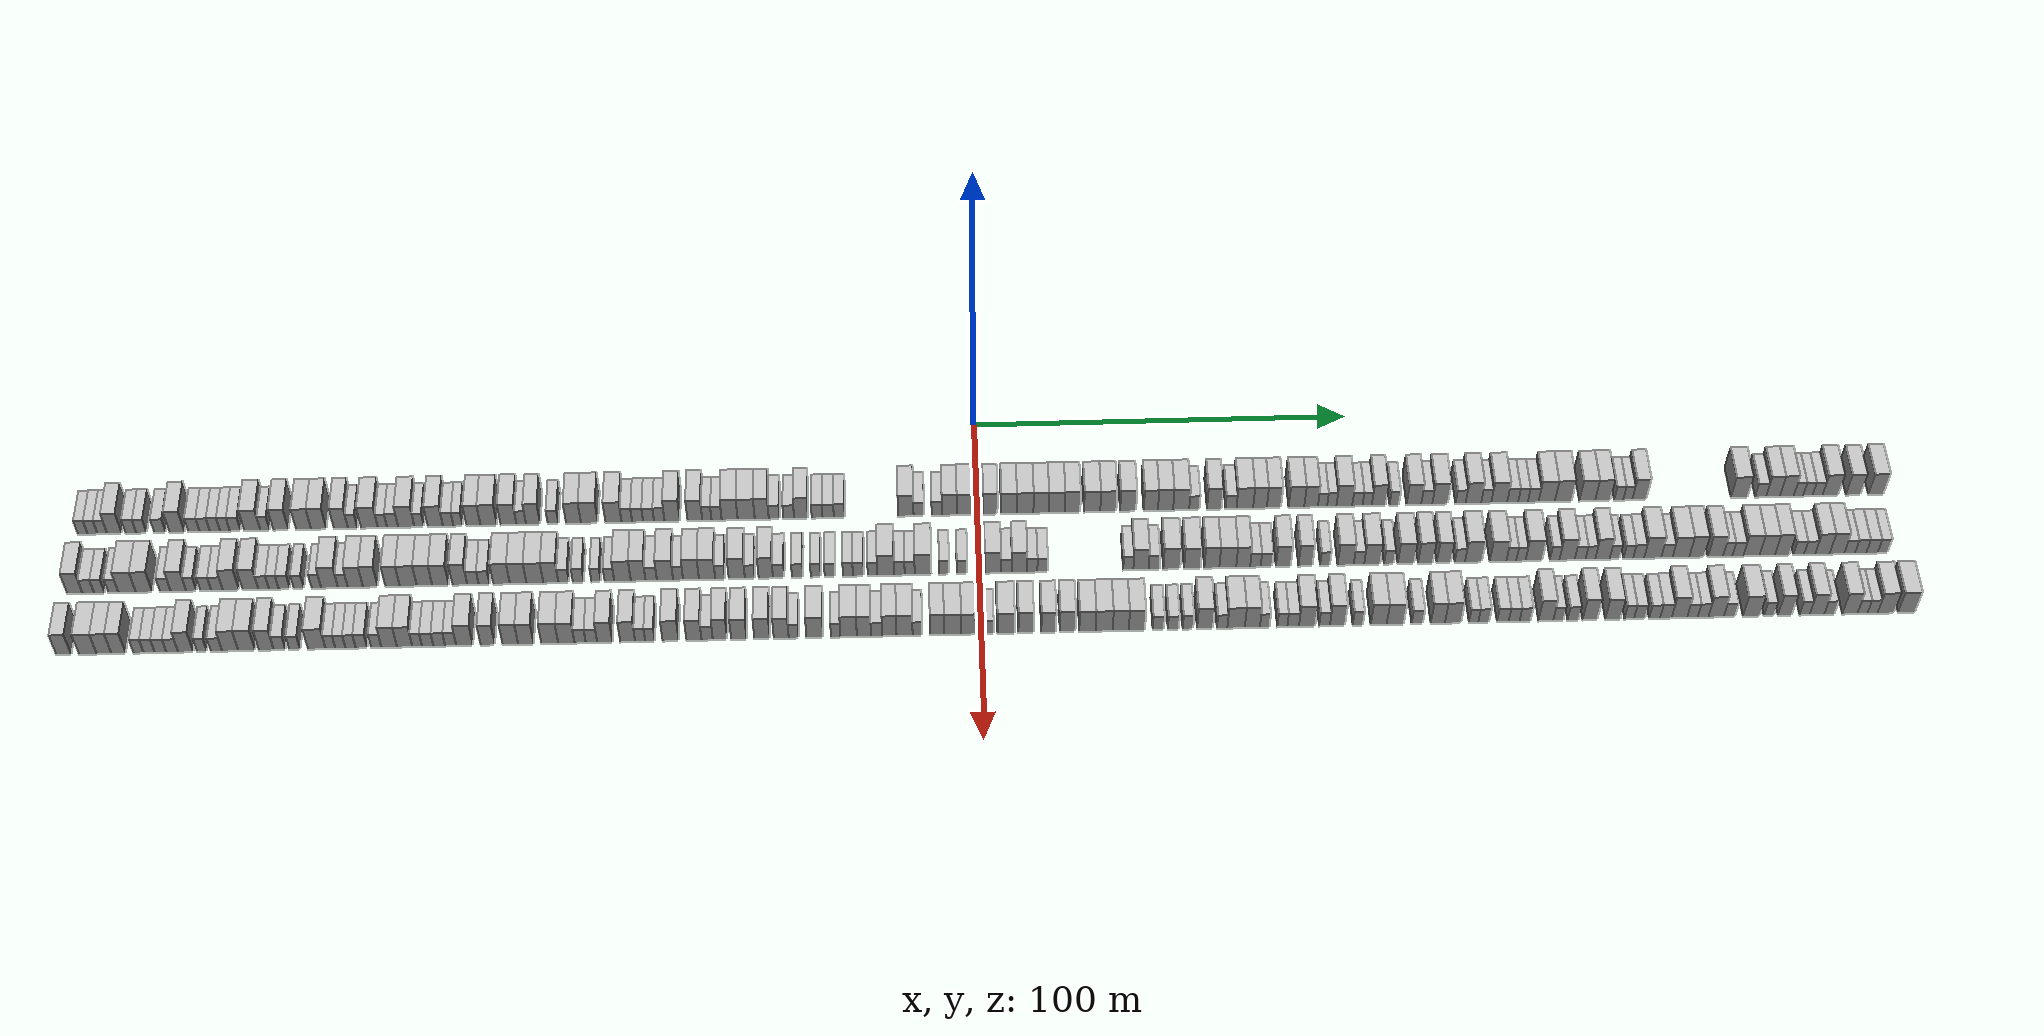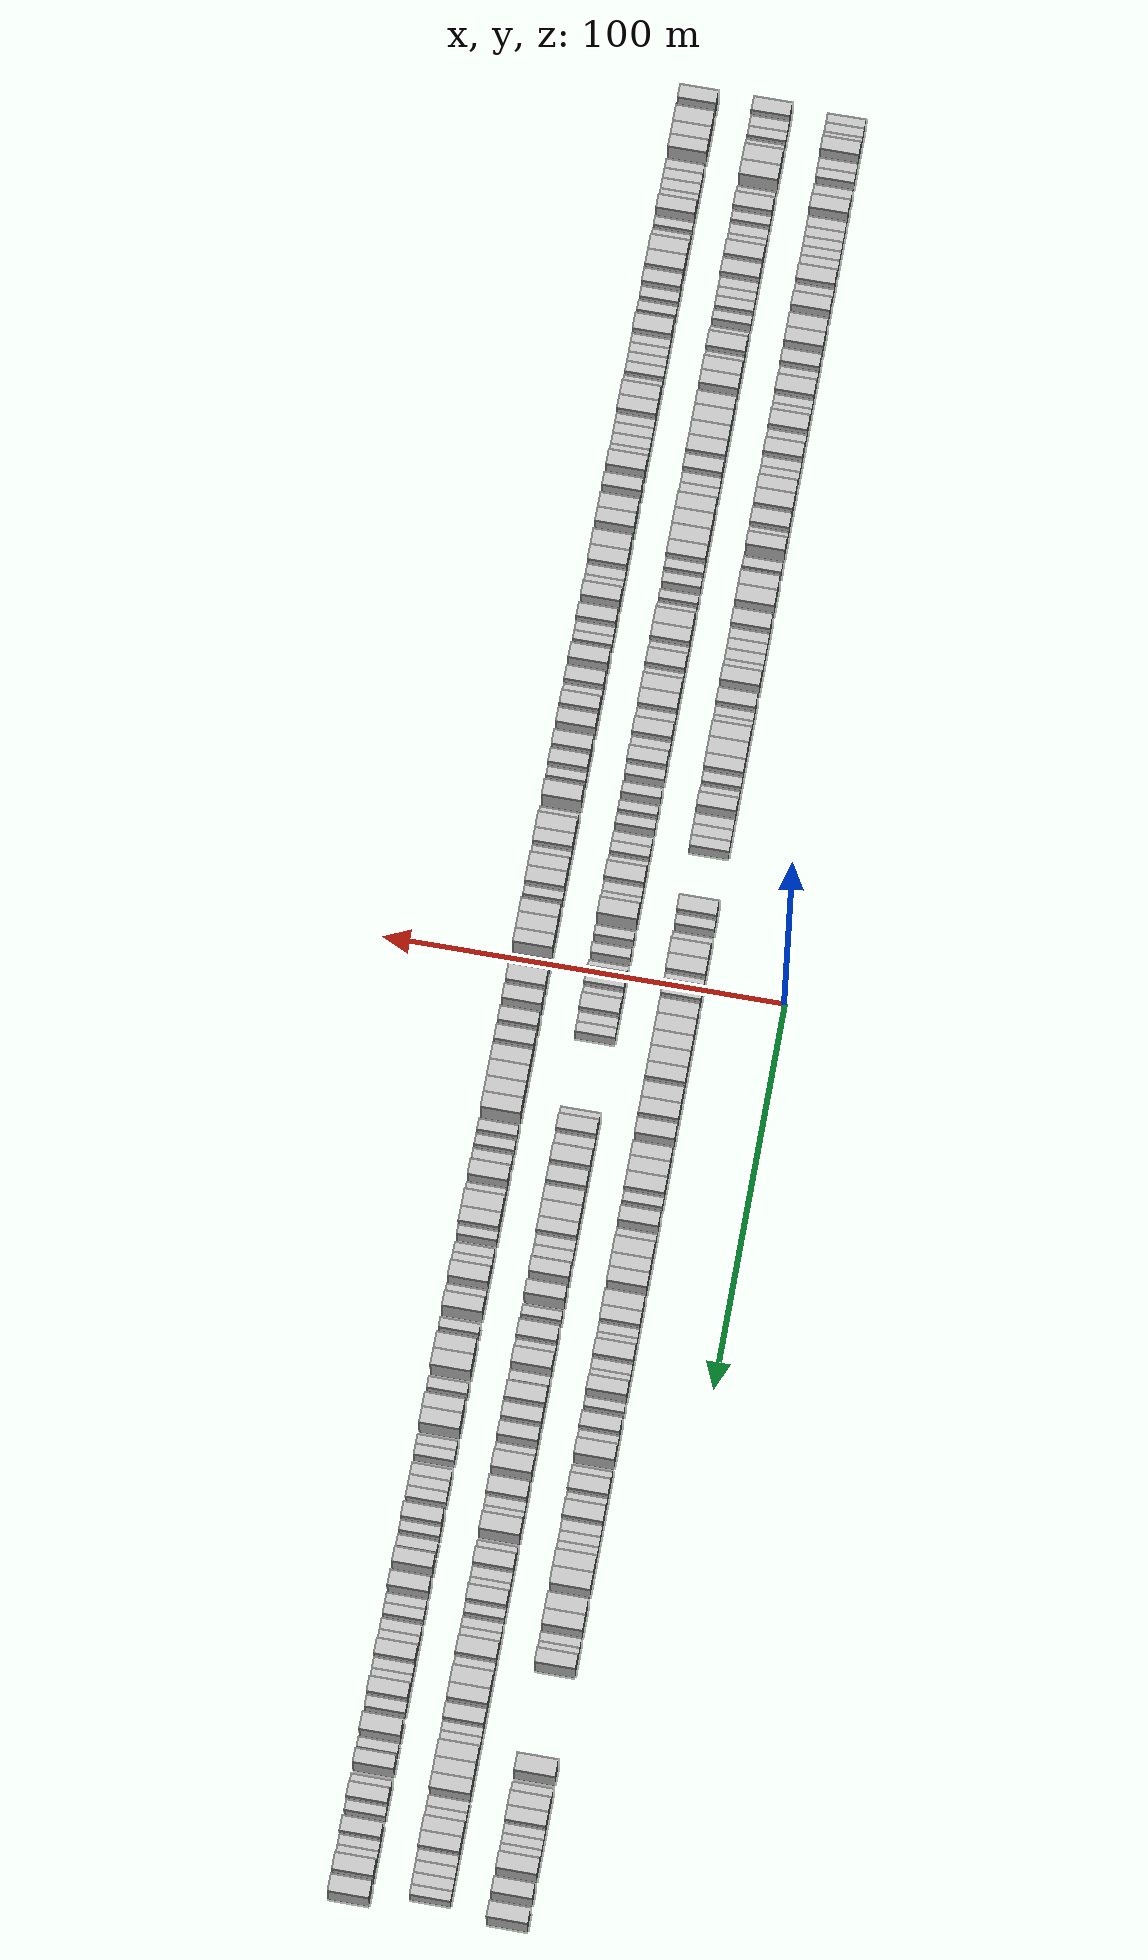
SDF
<sdf version="1.6">
 <world name="default">
  <scene>
   <sky><clouds><speed>12</speed></clouds></sky>
   <ambient>0.4 0.4 0.4 1</ambient>
   <background>0.7 0.7 0.7 1</background>
   <shadows>1</shadows>
  </scene>
  <gravity>0 0 -9.8066</gravity>
  <magnetic_field>6e-06 2.3e-05 -4.2e-05</magnetic_field>
  <physics default="0" name="default_physics" type="ode">
   <ode>
    <solver>
     <type>quick</type>
     <iters>10</iters>
     <sor>1.0</sor>
     <use_dynamic_moi_rescaling>0</use_dynamic_moi_rescaling>
    </solver>
    <constraints>
     <cfm>0</cfm>
     <erp>0.2</erp>
     <contact_max_correcting_vel>100</contact_max_correcting_vel>
     <contact_surface_layer>0.001</contact_surface_layer>
    </constraints>
   </ode>
   <max_step_size>0.004</max_step_size>
   <real_time_factor>1</real_time_factor>
   <real_time_update_rate>250</real_time_update_rate>
  </physics>
  <light name="sun" type="directional">
   <pose>0 0 10 0 0 0</pose>
   <diffuse>0.8 0.8 0.8 1</diffuse>
   <specular>0.2 0.2 0.2 1</specular>
   <attenuation>
    <range>1000</range>
    <constant>0.9</constant>
    <linear>0.01</linear>
    <quadratic>0.001</quadratic>
   </attenuation>
   <direction>-0.5 0.1 -0.9</direction>
  </light>
  <model name="building_1">
   <static>1</static>
   <pose>25.0000 -234.7300 0 0.000000 0.000000 0.000000</pose>
   <link name="link">
    <pose>0 0 3.00 0 0 0</pose>
    <collision name="collision"><geometry><box><size>10.0000 2.5399 6.0000</size></box></geometry></collision>
    <visual name="visual">
     <cast_shadows>0</cast_shadows>
     <geometry><box><size>10.0000 2.5399 6.0000</size></box></geometry>
     <material>
      <script>
       <uri>model://HANNAS_wall/materials/scripts</uri>
       <uri>model://HANNAS_wall/materials/textures</uri>
       <name>vrc/HANNAS_wall</name>
      </script>
     </material>
    </visual>
   </link>
  </model>
  <model name="building_2">
   <static>1</static>
   <pose>25.0000 -232.1696 0 0.000000 0.000000 0.000000</pose>
   <link name="link">
    <pose>0 0 3.00 0 0 0</pose>
    <collision name="collision"><geometry><box><size>10.0000 2.5809 6.0000</size></box></geometry></collision>
    <visual name="visual">
     <cast_shadows>0</cast_shadows>
     <geometry><box><size>10.0000 2.5809 6.0000</size></box></geometry>
     <material>
      <script>
       <uri>model://HANNAS_wall/materials/scripts</uri>
       <uri>model://HANNAS_wall/materials/textures</uri>
       <name>vrc/HANNAS_wall</name>
      </script>
     </material>
    </visual>
   </link>
  </model>
  <model name="building_3">
   <static>1</static>
   <pose>25.0000 -229.6061 0 0.000000 0.000000 0.000000</pose>
   <link name="link">
    <pose>0 0 3.00 0 0 0</pose>
    <collision name="collision"><geometry><box><size>10.0000 2.5462 6.0000</size></box></geometry></collision>
    <visual name="visual">
     <cast_shadows>0</cast_shadows>
     <geometry><box><size>10.0000 2.5462 6.0000</size></box></geometry>
     <material>
      <script>
       <uri>model://HANNAS_wall/materials/scripts</uri>
       <uri>model://HANNAS_wall/materials/textures</uri>
       <name>vrc/HANNAS_wall</name>
      </script>
     </material>
    </visual>
   </link>
  </model>
  <model name="building_4">
   <static>1</static>
   <pose>25.0000 -226.4390 0 0.000000 0.000000 0.000000</pose>
   <link name="link">
    <pose>0 0 4.50 0 0 0</pose>
    <collision name="collision"><geometry><box><size>10.0000 3.7880 9.0000</size></box></geometry></collision>
    <visual name="visual">
     <cast_shadows>0</cast_shadows>
     <geometry><box><size>10.0000 3.7880 9.0000</size></box></geometry>
     <material>
      <script>
       <uri>model://HANNAS_wall/materials/scripts</uri>
       <uri>model://HANNAS_wall/materials/textures</uri>
       <name>vrc/HANNAS_wall</name>
      </script>
     </material>
    </visual>
   </link>
  </model>
  <model name="building_5">
   <static>1</static>
   <pose>25.0000 -222.1377 0 0.000000 0.000000 0.000000</pose>
   <link name="link">
    <pose>0 0 3.00 0 0 0</pose>
    <collision name="collision"><geometry><box><size>10.0000 2.8146 6.0000</size></box></geometry></collision>
    <visual name="visual">
     <cast_shadows>0</cast_shadows>
     <geometry><box><size>10.0000 2.8146 6.0000</size></box></geometry>
     <material>
      <script>
       <uri>model://HANNAS_wall/materials/scripts</uri>
       <uri>model://HANNAS_wall/materials/textures</uri>
       <name>vrc/HANNAS_wall</name>
      </script>
     </material>
    </visual>
   </link>
  </model>
  <model name="building_6">
   <static>1</static>
   <pose>25.0000 -219.3900 0 0.000000 0.000000 0.000000</pose>
   <link name="link">
    <pose>0 0 3.00 0 0 0</pose>
    <collision name="collision"><geometry><box><size>10.0000 2.6808 6.0000</size></box></geometry></collision>
    <visual name="visual">
     <cast_shadows>0</cast_shadows>
     <geometry><box><size>10.0000 2.6808 6.0000</size></box></geometry>
     <material>
      <script>
       <uri>model://HANNAS_wall/materials/scripts</uri>
       <uri>model://HANNAS_wall/materials/textures</uri>
       <name>vrc/HANNAS_wall</name>
      </script>
     </material>
    </visual>
   </link>
  </model>
  <model name="building_7">
   <static>1</static>
   <pose>25.0000 -214.5539 0 0.000000 0.000000 0.000000</pose>
   <link name="link">
    <pose>0 0 3.00 0 0 0</pose>
    <collision name="collision"><geometry><box><size>10.0000 2.9915 6.0000</size></box></geometry></collision>
    <visual name="visual">
     <cast_shadows>0</cast_shadows>
     <geometry><box><size>10.0000 2.9915 6.0000</size></box></geometry>
     <material>
      <script>
       <uri>model://HANNAS_wall/materials/scripts</uri>
       <uri>model://HANNAS_wall/materials/textures</uri>
       <name>vrc/HANNAS_wall</name>
      </script>
     </material>
    </visual>
   </link>
  </model>
  <model name="building_8">
   <static>1</static>
   <pose>25.0000 -210.1084 0 0.000000 0.000000 0.000000</pose>
   <link name="link">
    <pose>0 0 4.50 0 0 0</pose>
    <collision name="collision"><geometry><box><size>10.0000 3.8995 9.0000</size></box></geometry></collision>
    <visual name="visual">
     <cast_shadows>0</cast_shadows>
     <geometry><box><size>10.0000 3.8995 9.0000</size></box></geometry>
     <material>
      <script>
       <uri>model://HANNAS_wall/materials/scripts</uri>
       <uri>model://HANNAS_wall/materials/textures</uri>
       <name>vrc/HANNAS_wall</name>
      </script>
     </material>
    </visual>
   </link>
  </model>
  <model name="building_9">
   <static>1</static>
   <pose>25.0000 -205.6947 0 0.000000 0.000000 0.000000</pose>
   <link name="link">
    <pose>0 0 3.00 0 0 0</pose>
    <collision name="collision"><geometry><box><size>10.0000 2.9279 6.0000</size></box></geometry></collision>
    <visual name="visual">
     <cast_shadows>0</cast_shadows>
     <geometry><box><size>10.0000 2.9279 6.0000</size></box></geometry>
     <material>
      <script>
       <uri>model://HANNAS_wall/materials/scripts</uri>
       <uri>model://HANNAS_wall/materials/textures</uri>
       <name>vrc/HANNAS_wall</name>
      </script>
     </material>
    </visual>
   </link>
  </model>
  <model name="building_10">
   <static>1</static>
   <pose>25.0000 -202.8635 0 0.000000 0.000000 0.000000</pose>
   <link name="link">
    <pose>0 0 3.00 0 0 0</pose>
    <collision name="collision"><geometry><box><size>10.0000 2.7345 6.0000</size></box></geometry></collision>
    <visual name="visual">
     <cast_shadows>0</cast_shadows>
     <geometry><box><size>10.0000 2.7345 6.0000</size></box></geometry>
     <material>
      <script>
       <uri>model://HANNAS_wall/materials/scripts</uri>
       <uri>model://HANNAS_wall/materials/textures</uri>
       <name>vrc/HANNAS_wall</name>
      </script>
     </material>
    </visual>
   </link>
  </model>
  <model name="building_11">
   <static>1</static>
   <pose>25.0000 -200.1783 0 0.000000 0.000000 0.000000</pose>
   <link name="link">
    <pose>0 0 3.00 0 0 0</pose>
    <collision name="collision"><geometry><box><size>10.0000 2.6359 6.0000</size></box></geometry></collision>
    <visual name="visual">
     <cast_shadows>0</cast_shadows>
     <geometry><box><size>10.0000 2.6359 6.0000</size></box></geometry>
     <material>
      <script>
       <uri>model://HANNAS_wall/materials/scripts</uri>
       <uri>model://HANNAS_wall/materials/textures</uri>
       <name>vrc/HANNAS_wall</name>
      </script>
     </material>
    </visual>
   </link>
  </model>
  <model name="building_12">
   <static>1</static>
   <pose>25.0000 -197.5821 0 0.000000 0.000000 0.000000</pose>
   <link name="link">
    <pose>0 0 3.00 0 0 0</pose>
    <collision name="collision"><geometry><box><size>10.0000 2.5566 6.0000</size></box></geometry></collision>
    <visual name="visual">
     <cast_shadows>0</cast_shadows>
     <geometry><box><size>10.0000 2.5566 6.0000</size></box></geometry>
     <material>
      <script>
       <uri>model://HANNAS_wall/materials/scripts</uri>
       <uri>model://HANNAS_wall/materials/textures</uri>
       <name>vrc/HANNAS_wall</name>
      </script>
     </material>
    </visual>
   </link>
  </model>
  <model name="building_13">
   <static>1</static>
   <pose>25.0000 -194.9062 0 0.000000 0.000000 0.000000</pose>
   <link name="link">
    <pose>0 0 3.00 0 0 0</pose>
    <collision name="collision"><geometry><box><size>10.0000 2.7951 6.0000</size></box></geometry></collision>
    <visual name="visual">
     <cast_shadows>0</cast_shadows>
     <geometry><box><size>10.0000 2.7951 6.0000</size></box></geometry>
     <material>
      <script>
       <uri>model://HANNAS_wall/materials/scripts</uri>
       <uri>model://HANNAS_wall/materials/textures</uri>
       <name>vrc/HANNAS_wall</name>
      </script>
     </material>
    </visual>
   </link>
  </model>
  <model name="building_14">
   <static>1</static>
   <pose>25.0000 -190.4212 0 0.000000 0.000000 0.000000</pose>
   <link name="link">
    <pose>0 0 4.50 0 0 0</pose>
    <collision name="collision"><geometry><box><size>10.0000 4.1749 9.0000</size></box></geometry></collision>
    <visual name="visual">
     <cast_shadows>0</cast_shadows>
     <geometry><box><size>10.0000 4.1749 9.0000</size></box></geometry>
     <material>
      <script>
       <uri>model://HANNAS_wall/materials/scripts</uri>
       <uri>model://HANNAS_wall/materials/textures</uri>
       <name>vrc/HANNAS_wall</name>
      </script>
     </material>
    </visual>
   </link>
  </model>
  <model name="building_15">
   <static>1</static>
   <pose>25.0000 -187.1157 0 0.000000 0.000000 0.000000</pose>
   <link name="link">
    <pose>0 0 3.00 0 0 0</pose>
    <collision name="collision"><geometry><box><size>10.0000 2.4363 6.0000</size></box></geometry></collision>
    <visual name="visual">
     <cast_shadows>0</cast_shadows>
     <geometry><box><size>10.0000 2.4363 6.0000</size></box></geometry>
     <material>
      <script>
       <uri>model://HANNAS_wall/materials/scripts</uri>
       <uri>model://HANNAS_wall/materials/textures</uri>
       <name>vrc/HANNAS_wall</name>
      </script>
     </material>
    </visual>
   </link>
  </model>
  <model name="building_16">
   <static>1</static>
   <pose>25.0000 -182.9373 0 0.000000 0.000000 0.000000</pose>
   <link name="link">
    <pose>0 0 4.50 0 0 0</pose>
    <collision name="collision"><geometry><box><size>10.0000 3.9205 9.0000</size></box></geometry></collision>
    <visual name="visual">
     <cast_shadows>0</cast_shadows>
     <geometry><box><size>10.0000 3.9205 9.0000</size></box></geometry>
     <material>
      <script>
       <uri>model://HANNAS_wall/materials/scripts</uri>
       <uri>model://HANNAS_wall/materials/textures</uri>
       <name>vrc/HANNAS_wall</name>
      </script>
     </material>
    </visual>
   </link>
  </model>
  <model name="building_17">
   <static>1</static>
   <pose>25.0000 -177.0001 0 0.000000 0.000000 0.000000</pose>
   <link name="link">
    <pose>0 0 4.50 0 0 0</pose>
    <collision name="collision"><geometry><box><size>10.0000 3.9538 9.0000</size></box></geometry></collision>
    <visual name="visual">
     <cast_shadows>0</cast_shadows>
     <geometry><box><size>10.0000 3.9538 9.0000</size></box></geometry>
     <material>
      <script>
       <uri>model://HANNAS_wall/materials/scripts</uri>
       <uri>model://HANNAS_wall/materials/textures</uri>
       <name>vrc/HANNAS_wall</name>
      </script>
     </material>
    </visual>
   </link>
  </model>
  <model name="building_18">
   <static>1</static>
   <pose>25.0000 -173.0439 0 0.000000 0.000000 0.000000</pose>
   <link name="link">
    <pose>0 0 4.50 0 0 0</pose>
    <collision name="collision"><geometry><box><size>10.0000 3.9588 9.0000</size></box></geometry></collision>
    <visual name="visual">
     <cast_shadows>0</cast_shadows>
     <geometry><box><size>10.0000 3.9588 9.0000</size></box></geometry>
     <material>
      <script>
       <uri>model://HANNAS_wall/materials/scripts</uri>
       <uri>model://HANNAS_wall/materials/textures</uri>
       <name>vrc/HANNAS_wall</name>
      </script>
     </material>
    </visual>
   </link>
  </model>
  <model name="building_19">
   <static>1</static>
   <pose>25.0000 -167.2151 0 0.000000 0.000000 0.000000</pose>
   <link name="link">
    <pose>0 0 4.50 0 0 0</pose>
    <collision name="collision"><geometry><box><size>10.0000 3.6988 9.0000</size></box></geometry></collision>
    <visual name="visual">
     <cast_shadows>0</cast_shadows>
     <geometry><box><size>10.0000 3.6988 9.0000</size></box></geometry>
     <material>
      <script>
       <uri>model://HANNAS_wall/materials/scripts</uri>
       <uri>model://HANNAS_wall/materials/textures</uri>
       <name>vrc/HANNAS_wall</name>
      </script>
     </material>
    </visual>
   </link>
  </model>
  <model name="building_20">
   <static>1</static>
   <pose>25.0000 -164.1573 0 0.000000 0.000000 0.000000</pose>
   <link name="link">
    <pose>0 0 3.00 0 0 0</pose>
    <collision name="collision"><geometry><box><size>10.0000 2.4168 6.0000</size></box></geometry></collision>
    <visual name="visual">
     <cast_shadows>0</cast_shadows>
     <geometry><box><size>10.0000 2.4168 6.0000</size></box></geometry>
     <material>
      <script>
       <uri>model://HANNAS_wall/materials/scripts</uri>
       <uri>model://HANNAS_wall/materials/textures</uri>
       <name>vrc/HANNAS_wall</name>
      </script>
     </material>
    </visual>
   </link>
  </model>
  <model name="building_21">
   <static>1</static>
   <pose>25.0000 -159.7480 0 0.000000 0.000000 0.000000</pose>
   <link name="link">
    <pose>0 0 4.50 0 0 0</pose>
    <collision name="collision"><geometry><box><size>10.0000 4.4018 9.0000</size></box></geometry></collision>
    <visual name="visual">
     <cast_shadows>0</cast_shadows>
     <geometry><box><size>10.0000 4.4018 9.0000</size></box></geometry>
     <material>
      <script>
       <uri>model://HANNAS_wall/materials/scripts</uri>
       <uri>model://HANNAS_wall/materials/textures</uri>
       <name>vrc/HANNAS_wall</name>
      </script>
     </material>
    </visual>
   </link>
  </model>
  <model name="building_22">
   <static>1</static>
   <pose>25.0000 -156.3460 0 0.000000 0.000000 0.000000</pose>
   <link name="link">
    <pose>0 0 3.00 0 0 0</pose>
    <collision name="collision"><geometry><box><size>10.0000 2.4022 6.0000</size></box></geometry></collision>
    <visual name="visual">
     <cast_shadows>0</cast_shadows>
     <geometry><box><size>10.0000 2.4022 6.0000</size></box></geometry>
     <material>
      <script>
       <uri>model://HANNAS_wall/materials/scripts</uri>
       <uri>model://HANNAS_wall/materials/textures</uri>
       <name>vrc/HANNAS_wall</name>
      </script>
     </material>
    </visual>
   </link>
  </model>
  <model name="building_23">
   <static>1</static>
   <pose>25.0000 -153.6827 0 0.000000 0.000000 0.000000</pose>
   <link name="link">
    <pose>0 0 3.00 0 0 0</pose>
    <collision name="collision"><geometry><box><size>10.0000 2.9243 6.0000</size></box></geometry></collision>
    <visual name="visual">
     <cast_shadows>0</cast_shadows>
     <geometry><box><size>10.0000 2.9243 6.0000</size></box></geometry>
     <material>
      <script>
       <uri>model://HANNAS_wall/materials/scripts</uri>
       <uri>model://HANNAS_wall/materials/textures</uri>
       <name>vrc/HANNAS_wall</name>
      </script>
     </material>
    </visual>
   </link>
  </model>
  <model name="building_24">
   <static>1</static>
   <pose>25.0000 -150.0973 0 0.000000 0.000000 0.000000</pose>
   <link name="link">
    <pose>0 0 4.50 0 0 0</pose>
    <collision name="collision"><geometry><box><size>10.0000 4.2466 9.0000</size></box></geometry></collision>
    <visual name="visual">
     <cast_shadows>0</cast_shadows>
     <geometry><box><size>10.0000 4.2466 9.0000</size></box></geometry>
     <material>
      <script>
       <uri>model://HANNAS_wall/materials/scripts</uri>
       <uri>model://HANNAS_wall/materials/textures</uri>
       <name>vrc/HANNAS_wall</name>
      </script>
     </material>
    </visual>
   </link>
  </model>
  <model name="building_25">
   <static>1</static>
   <pose>25.0000 -146.7279 0 0.000000 0.000000 0.000000</pose>
   <link name="link">
    <pose>0 0 3.00 0 0 0</pose>
    <collision name="collision"><geometry><box><size>10.0000 2.4922 6.0000</size></box></geometry></collision>
    <visual name="visual">
     <cast_shadows>0</cast_shadows>
     <geometry><box><size>10.0000 2.4922 6.0000</size></box></geometry>
     <material>
      <script>
       <uri>model://HANNAS_wall/materials/scripts</uri>
       <uri>model://HANNAS_wall/materials/textures</uri>
       <name>vrc/HANNAS_wall</name>
      </script>
     </material>
    </visual>
   </link>
  </model>
  <model name="building_26">
   <static>1</static>
   <pose>25.0000 -142.4939 0 0.000000 0.000000 0.000000</pose>
   <link name="link">
    <pose>0 0 4.50 0 0 0</pose>
    <collision name="collision"><geometry><box><size>10.0000 3.9759 9.0000</size></box></geometry></collision>
    <visual name="visual">
     <cast_shadows>0</cast_shadows>
     <geometry><box><size>10.0000 3.9759 9.0000</size></box></geometry>
     <material>
      <script>
       <uri>model://HANNAS_wall/materials/scripts</uri>
       <uri>model://HANNAS_wall/materials/textures</uri>
       <name>vrc/HANNAS_wall</name>
      </script>
     </material>
    </visual>
   </link>
  </model>
  <model name="building_27">
   <static>1</static>
   <pose>25.0000 -139.1345 0 0.000000 0.000000 0.000000</pose>
   <link name="link">
    <pose>0 0 3.00 0 0 0</pose>
    <collision name="collision"><geometry><box><size>10.0000 2.7429 6.0000</size></box></geometry></collision>
    <visual name="visual">
     <cast_shadows>0</cast_shadows>
     <geometry><box><size>10.0000 2.7429 6.0000</size></box></geometry>
     <material>
      <script>
       <uri>model://HANNAS_wall/materials/scripts</uri>
       <uri>model://HANNAS_wall/materials/textures</uri>
       <name>vrc/HANNAS_wall</name>
      </script>
     </material>
    </visual>
   </link>
  </model>
  <model name="building_28">
   <static>1</static>
   <pose>25.0000 -136.5492 0 0.000000 0.000000 0.000000</pose>
   <link name="link">
    <pose>0 0 3.00 0 0 0</pose>
    <collision name="collision"><geometry><box><size>10.0000 2.4277 6.0000</size></box></geometry></collision>
    <visual name="visual">
     <cast_shadows>0</cast_shadows>
     <geometry><box><size>10.0000 2.4277 6.0000</size></box></geometry>
     <material>
      <script>
       <uri>model://HANNAS_wall/materials/scripts</uri>
       <uri>model://HANNAS_wall/materials/textures</uri>
       <name>vrc/HANNAS_wall</name>
      </script>
     </material>
    </visual>
   </link>
  </model>
  <model name="building_29">
   <static>1</static>
   <pose>25.0000 -132.5048 0 0.000000 0.000000 0.000000</pose>
   <link name="link">
    <pose>0 0 4.50 0 0 0</pose>
    <collision name="collision"><geometry><box><size>10.0000 3.6610 9.0000</size></box></geometry></collision>
    <visual name="visual">
     <cast_shadows>0</cast_shadows>
     <geometry><box><size>10.0000 3.6610 9.0000</size></box></geometry>
     <material>
      <script>
       <uri>model://HANNAS_wall/materials/scripts</uri>
       <uri>model://HANNAS_wall/materials/textures</uri>
       <name>vrc/HANNAS_wall</name>
      </script>
     </material>
    </visual>
   </link>
  </model>
  <model name="building_30">
   <static>1</static>
   <pose>25.0000 -128.5264 0 0.000000 0.000000 0.000000</pose>
   <link name="link">
    <pose>0 0 4.50 0 0 0</pose>
    <collision name="collision"><geometry><box><size>10.0000 4.2959 9.0000</size></box></geometry></collision>
    <visual name="visual">
     <cast_shadows>0</cast_shadows>
     <geometry><box><size>10.0000 4.2959 9.0000</size></box></geometry>
     <material>
      <script>
       <uri>model://HANNAS_wall/materials/scripts</uri>
       <uri>model://HANNAS_wall/materials/textures</uri>
       <name>vrc/HANNAS_wall</name>
      </script>
     </material>
    </visual>
   </link>
  </model>
  <model name="building_31">
   <static>1</static>
   <pose>25.0000 -123.2931 0 0.000000 0.000000 0.000000</pose>
   <link name="link">
    <pose>0 0 4.50 0 0 0</pose>
    <collision name="collision"><geometry><box><size>10.0000 4.1706 9.0000</size></box></geometry></collision>
    <visual name="visual">
     <cast_shadows>0</cast_shadows>
     <geometry><box><size>10.0000 4.1706 9.0000</size></box></geometry>
     <material>
      <script>
       <uri>model://HANNAS_wall/materials/scripts</uri>
       <uri>model://HANNAS_wall/materials/textures</uri>
       <name>vrc/HANNAS_wall</name>
      </script>
     </material>
    </visual>
   </link>
  </model>
  <model name="building_32">
   <static>1</static>
   <pose>25.0000 -119.9647 0 0.000000 0.000000 0.000000</pose>
   <link name="link">
    <pose>0 0 3.00 0 0 0</pose>
    <collision name="collision"><geometry><box><size>10.0000 2.4863 6.0000</size></box></geometry></collision>
    <visual name="visual">
     <cast_shadows>0</cast_shadows>
     <geometry><box><size>10.0000 2.4863 6.0000</size></box></geometry>
     <material>
      <script>
       <uri>model://HANNAS_wall/materials/scripts</uri>
       <uri>model://HANNAS_wall/materials/textures</uri>
       <name>vrc/HANNAS_wall</name>
      </script>
     </material>
    </visual>
   </link>
  </model>
  <model name="building_33">
   <static>1</static>
   <pose>25.0000 -116.8746 0 0.000000 0.000000 0.000000</pose>
   <link name="link">
    <pose>0 0 4.50 0 0 0</pose>
    <collision name="collision"><geometry><box><size>10.0000 3.6937 9.0000</size></box></geometry></collision>
    <visual name="visual">
     <cast_shadows>0</cast_shadows>
     <geometry><box><size>10.0000 3.6937 9.0000</size></box></geometry>
     <material>
      <script>
       <uri>model://HANNAS_wall/materials/scripts</uri>
       <uri>model://HANNAS_wall/materials/textures</uri>
       <name>vrc/HANNAS_wall</name>
      </script>
     </material>
    </visual>
   </link>
  </model>
  <model name="building_34">
   <static>1</static>
   <pose>25.0000 -111.6336 0 0.000000 0.000000 0.000000</pose>
   <link name="link">
    <pose>0 0 3.00 0 0 0</pose>
    <collision name="collision"><geometry><box><size>10.0000 2.7883 6.0000</size></box></geometry></collision>
    <visual name="visual">
     <cast_shadows>0</cast_shadows>
     <geometry><box><size>10.0000 2.7883 6.0000</size></box></geometry>
     <material>
      <script>
       <uri>model://HANNAS_wall/materials/scripts</uri>
       <uri>model://HANNAS_wall/materials/textures</uri>
       <name>vrc/HANNAS_wall</name>
      </script>
     </material>
    </visual>
   </link>
  </model>
  <model name="building_35">
   <static>1</static>
   <pose>25.0000 -106.2833 0 0.000000 0.000000 0.000000</pose>
   <link name="link">
    <pose>0 0 4.50 0 0 0</pose>
    <collision name="collision"><geometry><box><size>10.0000 3.9123 9.0000</size></box></geometry></collision>
    <visual name="visual">
     <cast_shadows>0</cast_shadows>
     <geometry><box><size>10.0000 3.9123 9.0000</size></box></geometry>
     <material>
      <script>
       <uri>model://HANNAS_wall/materials/scripts</uri>
       <uri>model://HANNAS_wall/materials/textures</uri>
       <name>vrc/HANNAS_wall</name>
      </script>
     </material>
    </visual>
   </link>
  </model>
  <model name="building_36">
   <static>1</static>
   <pose>25.0000 -102.1065 0 0.000000 0.000000 0.000000</pose>
   <link name="link">
    <pose>0 0 4.50 0 0 0</pose>
    <collision name="collision"><geometry><box><size>10.0000 4.4412 9.0000</size></box></geometry></collision>
    <visual name="visual">
     <cast_shadows>0</cast_shadows>
     <geometry><box><size>10.0000 4.4412 9.0000</size></box></geometry>
     <material>
      <script>
       <uri>model://HANNAS_wall/materials/scripts</uri>
       <uri>model://HANNAS_wall/materials/textures</uri>
       <name>vrc/HANNAS_wall</name>
      </script>
     </material>
    </visual>
   </link>
  </model>
  <model name="building_37">
   <static>1</static>
   <pose>25.0000 -95.7705 0 0.000000 0.000000 0.000000</pose>
   <link name="link">
    <pose>0 0 4.50 0 0 0</pose>
    <collision name="collision"><geometry><box><size>10.0000 4.2309 9.0000</size></box></geometry></collision>
    <visual name="visual">
     <cast_shadows>0</cast_shadows>
     <geometry><box><size>10.0000 4.2309 9.0000</size></box></geometry>
     <material>
      <script>
       <uri>model://HANNAS_wall/materials/scripts</uri>
       <uri>model://HANNAS_wall/materials/textures</uri>
       <name>vrc/HANNAS_wall</name>
      </script>
     </material>
    </visual>
   </link>
  </model>
  <model name="building_38">
   <static>1</static>
   <pose>25.0000 -92.2708 0 0.000000 0.000000 0.000000</pose>
   <link name="link">
    <pose>0 0 3.00 0 0 0</pose>
    <collision name="collision"><geometry><box><size>10.0000 2.7686 6.0000</size></box></geometry></collision>
    <visual name="visual">
     <cast_shadows>0</cast_shadows>
     <geometry><box><size>10.0000 2.7686 6.0000</size></box></geometry>
     <material>
      <script>
       <uri>model://HANNAS_wall/materials/scripts</uri>
       <uri>model://HANNAS_wall/materials/textures</uri>
       <name>vrc/HANNAS_wall</name>
      </script>
     </material>
    </visual>
   </link>
  </model>
  <model name="building_39">
   <static>1</static>
   <pose>25.0000 -89.4517 0 0.000000 0.000000 0.000000</pose>
   <link name="link">
    <pose>0 0 3.00 0 0 0</pose>
    <collision name="collision"><geometry><box><size>10.0000 2.8696 6.0000</size></box></geometry></collision>
    <visual name="visual">
     <cast_shadows>0</cast_shadows>
     <geometry><box><size>10.0000 2.8696 6.0000</size></box></geometry>
     <material>
      <script>
       <uri>model://HANNAS_wall/materials/scripts</uri>
       <uri>model://HANNAS_wall/materials/textures</uri>
       <name>vrc/HANNAS_wall</name>
      </script>
     </material>
    </visual>
   </link>
  </model>
  <model name="building_40">
   <static>1</static>
   <pose>25.0000 -86.5726 0 0.000000 0.000000 0.000000</pose>
   <link name="link">
    <pose>0 0 3.00 0 0 0</pose>
    <collision name="collision"><geometry><box><size>10.0000 2.8887 6.0000</size></box></geometry></collision>
    <visual name="visual">
     <cast_shadows>0</cast_shadows>
     <geometry><box><size>10.0000 2.8887 6.0000</size></box></geometry>
     <material>
      <script>
       <uri>model://HANNAS_wall/materials/scripts</uri>
       <uri>model://HANNAS_wall/materials/textures</uri>
       <name>vrc/HANNAS_wall</name>
      </script>
     </material>
    </visual>
   </link>
  </model>
  <model name="building_41">
   <static>1</static>
   <pose>25.0000 -83.7462 0 0.000000 0.000000 0.000000</pose>
   <link name="link">
    <pose>0 0 3.00 0 0 0</pose>
    <collision name="collision"><geometry><box><size>10.0000 2.7640 6.0000</size></box></geometry></collision>
    <visual name="visual">
     <cast_shadows>0</cast_shadows>
     <geometry><box><size>10.0000 2.7640 6.0000</size></box></geometry>
     <material>
      <script>
       <uri>model://HANNAS_wall/materials/scripts</uri>
       <uri>model://HANNAS_wall/materials/textures</uri>
       <name>vrc/HANNAS_wall</name>
      </script>
     </material>
    </visual>
   </link>
  </model>
  <model name="building_42">
   <static>1</static>
   <pose>25.0000 -80.3539 0 0.000000 0.000000 0.000000</pose>
   <link name="link">
    <pose>0 0 4.50 0 0 0</pose>
    <collision name="collision"><geometry><box><size>10.0000 4.0206 9.0000</size></box></geometry></collision>
    <visual name="visual">
     <cast_shadows>0</cast_shadows>
     <geometry><box><size>10.0000 4.0206 9.0000</size></box></geometry>
     <material>
      <script>
       <uri>model://HANNAS_wall/materials/scripts</uri>
       <uri>model://HANNAS_wall/materials/textures</uri>
       <name>vrc/HANNAS_wall</name>
      </script>
     </material>
    </visual>
   </link>
  </model>
  <model name="building_43">
   <static>1</static>
   <pose>25.0000 -74.4029 0 0.000000 0.000000 0.000000</pose>
   <link name="link">
    <pose>0 0 4.50 0 0 0</pose>
    <collision name="collision"><geometry><box><size>10.0000 3.8813 9.0000</size></box></geometry></collision>
    <visual name="visual">
     <cast_shadows>0</cast_shadows>
     <geometry><box><size>10.0000 3.8813 9.0000</size></box></geometry>
     <material>
      <script>
       <uri>model://HANNAS_wall/materials/scripts</uri>
       <uri>model://HANNAS_wall/materials/textures</uri>
       <name>vrc/HANNAS_wall</name>
      </script>
     </material>
    </visual>
   </link>
  </model>
  <model name="building_44">
   <static>1</static>
   <pose>25.0000 -71.2445 0 0.000000 0.000000 0.000000</pose>
   <link name="link">
    <pose>0 0 3.00 0 0 0</pose>
    <collision name="collision"><geometry><box><size>10.0000 2.4356 6.0000</size></box></geometry></collision>
    <visual name="visual">
     <cast_shadows>0</cast_shadows>
     <geometry><box><size>10.0000 2.4356 6.0000</size></box></geometry>
     <material>
      <script>
       <uri>model://HANNAS_wall/materials/scripts</uri>
       <uri>model://HANNAS_wall/materials/textures</uri>
       <name>vrc/HANNAS_wall</name>
      </script>
     </material>
    </visual>
   </link>
  </model>
  <model name="building_45">
   <static>1</static>
   <pose>25.0000 -68.6941 0 0.000000 0.000000 0.000000</pose>
   <link name="link">
    <pose>0 0 3.00 0 0 0</pose>
    <collision name="collision"><geometry><box><size>10.0000 2.6651 6.0000</size></box></geometry></collision>
    <visual name="visual">
     <cast_shadows>0</cast_shadows>
     <geometry><box><size>10.0000 2.6651 6.0000</size></box></geometry>
     <material>
      <script>
       <uri>model://HANNAS_wall/materials/scripts</uri>
       <uri>model://HANNAS_wall/materials/textures</uri>
       <name>vrc/HANNAS_wall</name>
      </script>
     </material>
    </visual>
   </link>
  </model>
  <model name="building_46">
   <static>1</static>
   <pose>25.0000 -65.2576 0 0.000000 0.000000 0.000000</pose>
   <link name="link">
    <pose>0 0 4.50 0 0 0</pose>
    <collision name="collision"><geometry><box><size>10.0000 4.2079 9.0000</size></box></geometry></collision>
    <visual name="visual">
     <cast_shadows>0</cast_shadows>
     <geometry><box><size>10.0000 4.2079 9.0000</size></box></geometry>
     <material>
      <script>
       <uri>model://HANNAS_wall/materials/scripts</uri>
       <uri>model://HANNAS_wall/materials/textures</uri>
       <name>vrc/HANNAS_wall</name>
      </script>
     </material>
    </visual>
   </link>
  </model>
  <model name="building_47">
   <static>1</static>
   <pose>25.0000 -60.9126 0 0.000000 0.000000 0.000000</pose>
   <link name="link">
    <pose>0 0 4.50 0 0 0</pose>
    <collision name="collision"><geometry><box><size>10.0000 4.4822 9.0000</size></box></geometry></collision>
    <visual name="visual">
     <cast_shadows>0</cast_shadows>
     <geometry><box><size>10.0000 4.4822 9.0000</size></box></geometry>
     <material>
      <script>
       <uri>model://HANNAS_wall/materials/scripts</uri>
       <uri>model://HANNAS_wall/materials/textures</uri>
       <name>vrc/HANNAS_wall</name>
      </script>
     </material>
    </visual>
   </link>
  </model>
  <model name="building_48">
   <static>1</static>
   <pose>25.0000 -56.8321 0 0.000000 0.000000 0.000000</pose>
   <link name="link">
    <pose>0 0 4.50 0 0 0</pose>
    <collision name="collision"><geometry><box><size>10.0000 3.6788 9.0000</size></box></geometry></collision>
    <visual name="visual">
     <cast_shadows>0</cast_shadows>
     <geometry><box><size>10.0000 3.6788 9.0000</size></box></geometry>
     <material>
      <script>
       <uri>model://HANNAS_wall/materials/scripts</uri>
       <uri>model://HANNAS_wall/materials/textures</uri>
       <name>vrc/HANNAS_wall</name>
      </script>
     </material>
    </visual>
   </link>
  </model>
  <model name="building_49">
   <static>1</static>
   <pose>25.0000 -53.5726 0 0.000000 0.000000 0.000000</pose>
   <link name="link">
    <pose>0 0 3.00 0 0 0</pose>
    <collision name="collision"><geometry><box><size>10.0000 2.8402 6.0000</size></box></geometry></collision>
    <visual name="visual">
     <cast_shadows>0</cast_shadows>
     <geometry><box><size>10.0000 2.8402 6.0000</size></box></geometry>
     <material>
      <script>
       <uri>model://HANNAS_wall/materials/scripts</uri>
       <uri>model://HANNAS_wall/materials/textures</uri>
       <name>vrc/HANNAS_wall</name>
      </script>
     </material>
    </visual>
   </link>
  </model>
  <model name="building_50">
   <static>1</static>
   <pose>25.0000 -49.7343 0 0.000000 0.000000 0.000000</pose>
   <link name="link">
    <pose>0 0 3.00 0 0 0</pose>
    <collision name="collision"><geometry><box><size>10.0000 2.8363 6.0000</size></box></geometry></collision>
    <visual name="visual">
     <cast_shadows>0</cast_shadows>
     <geometry><box><size>10.0000 2.8363 6.0000</size></box></geometry>
     <material>
      <script>
       <uri>model://HANNAS_wall/materials/scripts</uri>
       <uri>model://HANNAS_wall/materials/textures</uri>
       <name>vrc/HANNAS_wall</name>
      </script>
     </material>
    </visual>
   </link>
  </model>
  <model name="building_51">
   <static>1</static>
   <pose>25.0000 -46.4999 0 0.000000 0.000000 0.000000</pose>
   <link name="link">
    <pose>0 0 4.50 0 0 0</pose>
    <collision name="collision"><geometry><box><size>10.0000 3.6325 9.0000</size></box></geometry></collision>
    <visual name="visual">
     <cast_shadows>0</cast_shadows>
     <geometry><box><size>10.0000 3.6325 9.0000</size></box></geometry>
     <material>
      <script>
       <uri>model://HANNAS_wall/materials/scripts</uri>
       <uri>model://HANNAS_wall/materials/textures</uri>
       <name>vrc/HANNAS_wall</name>
      </script>
     </material>
    </visual>
   </link>
  </model>
  <model name="building_52">
   <static>1</static>
   <pose>25.0000 -42.2697 0 0.000000 0.000000 0.000000</pose>
   <link name="link">
    <pose>0 0 3.00 0 0 0</pose>
    <collision name="collision"><geometry><box><size>10.0000 2.8280 6.0000</size></box></geometry></collision>
    <visual name="visual">
     <cast_shadows>0</cast_shadows>
     <geometry><box><size>10.0000 2.8280 6.0000</size></box></geometry>
     <material>
      <script>
       <uri>model://HANNAS_wall/materials/scripts</uri>
       <uri>model://HANNAS_wall/materials/textures</uri>
       <name>vrc/HANNAS_wall</name>
      </script>
     </material>
    </visual>
   </link>
  </model>
  <model name="building_53">
   <static>1</static>
   <pose>25.0000 -39.3607 0 0.000000 0.000000 0.000000</pose>
   <link name="link">
    <pose>0 0 3.00 0 0 0</pose>
    <collision name="collision"><geometry><box><size>10.0000 2.9900 6.0000</size></box></geometry></collision>
    <visual name="visual">
     <cast_shadows>0</cast_shadows>
     <geometry><box><size>10.0000 2.9900 6.0000</size></box></geometry>
     <material>
      <script>
       <uri>model://HANNAS_wall/materials/scripts</uri>
       <uri>model://HANNAS_wall/materials/textures</uri>
       <name>vrc/HANNAS_wall</name>
      </script>
     </material>
    </visual>
   </link>
  </model>
  <model name="building_54">
   <static>1</static>
   <pose>25.0000 -36.4236 0 0.000000 0.000000 0.000000</pose>
   <link name="link">
    <pose>0 0 3.00 0 0 0</pose>
    <collision name="collision"><geometry><box><size>10.0000 2.8842 6.0000</size></box></geometry></collision>
    <visual name="visual">
     <cast_shadows>0</cast_shadows>
     <geometry><box><size>10.0000 2.8842 6.0000</size></box></geometry>
     <material>
      <script>
       <uri>model://HANNAS_wall/materials/scripts</uri>
       <uri>model://HANNAS_wall/materials/textures</uri>
       <name>vrc/HANNAS_wall</name>
      </script>
     </material>
    </visual>
   </link>
  </model>
  <model name="building_55">
   <static>1</static>
   <pose>25.0000 -18.9226 0 0.000000 0.000000 0.000000</pose>
   <link name="link">
    <pose>0 0 4.50 0 0 0</pose>
    <collision name="collision"><geometry><box><size>10.0000 4.0393 9.0000</size></box></geometry></collision>
    <visual name="visual">
     <cast_shadows>0</cast_shadows>
     <geometry><box><size>10.0000 4.0393 9.0000</size></box></geometry>
     <material>
      <script>
       <uri>model://HANNAS_wall/materials/scripts</uri>
       <uri>model://HANNAS_wall/materials/textures</uri>
       <name>vrc/HANNAS_wall</name>
      </script>
     </material>
    </visual>
   </link>
  </model>
  <model name="building_56">
   <static>1</static>
   <pose>25.0000 -15.5169 0 0.000000 0.000000 0.000000</pose>
   <link name="link">
    <pose>0 0 3.00 0 0 0</pose>
    <collision name="collision"><geometry><box><size>10.0000 2.7720 6.0000</size></box></geometry></collision>
    <visual name="visual">
     <cast_shadows>0</cast_shadows>
     <geometry><box><size>10.0000 2.7720 6.0000</size></box></geometry>
     <material>
      <script>
       <uri>model://HANNAS_wall/materials/scripts</uri>
       <uri>model://HANNAS_wall/materials/textures</uri>
       <name>vrc/HANNAS_wall</name>
      </script>
     </material>
    </visual>
   </link>
  </model>
  <model name="building_57">
   <static>1</static>
   <pose>25.0000 -10.7822 0 0.000000 0.000000 0.000000</pose>
   <link name="link">
    <pose>0 0 3.00 0 0 0</pose>
    <collision name="collision"><geometry><box><size>10.0000 2.6976 6.0000</size></box></geometry></collision>
    <visual name="visual">
     <cast_shadows>0</cast_shadows>
     <geometry><box><size>10.0000 2.6976 6.0000</size></box></geometry>
     <material>
      <script>
       <uri>model://HANNAS_wall/materials/scripts</uri>
       <uri>model://HANNAS_wall/materials/textures</uri>
       <name>vrc/HANNAS_wall</name>
      </script>
     </material>
    </visual>
   </link>
  </model>
  <model name="building_58">
   <static>1</static>
   <pose>25.0000 -7.4671 0 0.000000 0.000000 0.000000</pose>
   <link name="link">
    <pose>0 0 4.50 0 0 0</pose>
    <collision name="collision"><geometry><box><size>10.0000 3.9326 9.0000</size></box></geometry></collision>
    <visual name="visual">
     <cast_shadows>0</cast_shadows>
     <geometry><box><size>10.0000 3.9326 9.0000</size></box></geometry>
     <material>
      <script>
       <uri>model://HANNAS_wall/materials/scripts</uri>
       <uri>model://HANNAS_wall/materials/textures</uri>
       <name>vrc/HANNAS_wall</name>
      </script>
     </material>
    </visual>
   </link>
  </model>
  <model name="building_59">
   <static>1</static>
   <pose>25.0000 -3.3821 0 0.000000 0.000000 0.000000</pose>
   <link name="link">
    <pose>0 0 4.50 0 0 0</pose>
    <collision name="collision"><geometry><box><size>10.0000 4.2374 9.0000</size></box></geometry></collision>
    <visual name="visual">
     <cast_shadows>0</cast_shadows>
     <geometry><box><size>10.0000 4.2374 9.0000</size></box></geometry>
     <material>
      <script>
       <uri>model://HANNAS_wall/materials/scripts</uri>
       <uri>model://HANNAS_wall/materials/textures</uri>
       <name>vrc/HANNAS_wall</name>
      </script>
     </material>
    </visual>
   </link>
  </model>
  <model name="building_60">
   <static>1</static>
   <pose>25.0000 0.0920 0 0.000000 0.000000 0.000000</pose>
   <link name="link">
    <pose>0 0 3.00 0 0 0</pose>
    <collision name="collision"><geometry><box><size>10.0000 2.7109 6.0000</size></box></geometry></collision>
    <visual name="visual">
     <cast_shadows>0</cast_shadows>
     <geometry><box><size>10.0000 2.7109 6.0000</size></box></geometry>
     <material>
      <script>
       <uri>model://HANNAS_wall/materials/scripts</uri>
       <uri>model://HANNAS_wall/materials/textures</uri>
       <name>vrc/HANNAS_wall</name>
      </script>
     </material>
    </visual>
   </link>
  </model>
  <model name="building_61">
   <static>1</static>
   <pose>25.0000 3.3259 0 0.000000 0.000000 0.000000</pose>
   <link name="link">
    <pose>0 0 4.50 0 0 0</pose>
    <collision name="collision"><geometry><box><size>10.0000 3.7569 9.0000</size></box></geometry></collision>
    <visual name="visual">
     <cast_shadows>0</cast_shadows>
     <geometry><box><size>10.0000 3.7569 9.0000</size></box></geometry>
     <material>
      <script>
       <uri>model://HANNAS_wall/materials/scripts</uri>
       <uri>model://HANNAS_wall/materials/textures</uri>
       <name>vrc/HANNAS_wall</name>
      </script>
     </material>
    </visual>
   </link>
  </model>
  <model name="building_62">
   <static>1</static>
   <pose>25.0000 8.2512 0 0.000000 0.000000 0.000000</pose>
   <link name="link">
    <pose>0 0 4.50 0 0 0</pose>
    <collision name="collision"><geometry><box><size>10.0000 4.0938 9.0000</size></box></geometry></collision>
    <visual name="visual">
     <cast_shadows>0</cast_shadows>
     <geometry><box><size>10.0000 4.0938 9.0000</size></box></geometry>
     <material>
      <script>
       <uri>model://HANNAS_wall/materials/scripts</uri>
       <uri>model://HANNAS_wall/materials/textures</uri>
       <name>vrc/HANNAS_wall</name>
      </script>
     </material>
    </visual>
   </link>
  </model>
  <model name="building_63">
   <static>1</static>
   <pose>25.0000 12.4885 0 0.000000 0.000000 0.000000</pose>
   <link name="link">
    <pose>0 0 4.50 0 0 0</pose>
    <collision name="collision"><geometry><box><size>10.0000 4.3806 9.0000</size></box></geometry></collision>
    <visual name="visual">
     <cast_shadows>0</cast_shadows>
     <geometry><box><size>10.0000 4.3806 9.0000</size></box></geometry>
     <material>
      <script>
       <uri>model://HANNAS_wall/materials/scripts</uri>
       <uri>model://HANNAS_wall/materials/textures</uri>
       <name>vrc/HANNAS_wall</name>
      </script>
     </material>
    </visual>
   </link>
  </model>
  <model name="building_64">
   <static>1</static>
   <pose>25.0000 16.7042 0 0.000000 0.000000 0.000000</pose>
   <link name="link">
    <pose>0 0 4.50 0 0 0</pose>
    <collision name="collision"><geometry><box><size>10.0000 4.0509 9.0000</size></box></geometry></collision>
    <visual name="visual">
     <cast_shadows>0</cast_shadows>
     <geometry><box><size>10.0000 4.0509 9.0000</size></box></geometry>
     <material>
      <script>
       <uri>model://HANNAS_wall/materials/scripts</uri>
       <uri>model://HANNAS_wall/materials/textures</uri>
       <name>vrc/HANNAS_wall</name>
      </script>
     </material>
    </visual>
   </link>
  </model>
  <model name="building_65">
   <static>1</static>
   <pose>25.0000 20.8555 0 0.000000 0.000000 0.000000</pose>
   <link name="link">
    <pose>0 0 4.50 0 0 0</pose>
    <collision name="collision"><geometry><box><size>10.0000 4.2516 9.0000</size></box></geometry></collision>
    <visual name="visual">
     <cast_shadows>0</cast_shadows>
     <geometry><box><size>10.0000 4.2516 9.0000</size></box></geometry>
     <material>
      <script>
       <uri>model://HANNAS_wall/materials/scripts</uri>
       <uri>model://HANNAS_wall/materials/textures</uri>
       <name>vrc/HANNAS_wall</name>
      </script>
     </material>
    </visual>
   </link>
  </model>
  <model name="building_66">
   <static>1</static>
   <pose>25.0000 25.0057 0 0.000000 0.000000 0.000000</pose>
   <link name="link">
    <pose>0 0 4.50 0 0 0</pose>
    <collision name="collision"><geometry><box><size>10.0000 4.0488 9.0000</size></box></geometry></collision>
    <visual name="visual">
     <cast_shadows>0</cast_shadows>
     <geometry><box><size>10.0000 4.0488 9.0000</size></box></geometry>
     <material>
      <script>
       <uri>model://HANNAS_wall/materials/scripts</uri>
       <uri>model://HANNAS_wall/materials/textures</uri>
       <name>vrc/HANNAS_wall</name>
      </script>
     </material>
    </visual>
   </link>
  </model>
  <model name="building_67">
   <static>1</static>
   <pose>25.0000 30.1719 0 0.000000 0.000000 0.000000</pose>
   <link name="link">
    <pose>0 0 4.50 0 0 0</pose>
    <collision name="collision"><geometry><box><size>10.0000 4.2837 9.0000</size></box></geometry></collision>
    <visual name="visual">
     <cast_shadows>0</cast_shadows>
     <geometry><box><size>10.0000 4.2837 9.0000</size></box></geometry>
     <material>
      <script>
       <uri>model://HANNAS_wall/materials/scripts</uri>
       <uri>model://HANNAS_wall/materials/textures</uri>
       <name>vrc/HANNAS_wall</name>
      </script>
     </material>
    </visual>
   </link>
  </model>
  <model name="building_68">
   <static>1</static>
   <pose>25.0000 34.4357 0 0.000000 0.000000 0.000000</pose>
   <link name="link">
    <pose>0 0 4.50 0 0 0</pose>
    <collision name="collision"><geometry><box><size>10.0000 4.2438 9.0000</size></box></geometry></collision>
    <visual name="visual">
     <cast_shadows>0</cast_shadows>
     <geometry><box><size>10.0000 4.2438 9.0000</size></box></geometry>
     <material>
      <script>
       <uri>model://HANNAS_wall/materials/scripts</uri>
       <uri>model://HANNAS_wall/materials/textures</uri>
       <name>vrc/HANNAS_wall</name>
      </script>
     </material>
    </visual>
   </link>
  </model>
  <model name="building_69">
   <static>1</static>
   <pose>25.0000 39.6681 0 0.000000 0.000000 0.000000</pose>
   <link name="link">
    <pose>0 0 4.50 0 0 0</pose>
    <collision name="collision"><geometry><box><size>10.0000 4.2209 9.0000</size></box></geometry></collision>
    <visual name="visual">
     <cast_shadows>0</cast_shadows>
     <geometry><box><size>10.0000 4.2209 9.0000</size></box></geometry>
     <material>
      <script>
       <uri>model://HANNAS_wall/materials/scripts</uri>
       <uri>model://HANNAS_wall/materials/textures</uri>
       <name>vrc/HANNAS_wall</name>
      </script>
     </material>
    </visual>
   </link>
  </model>
  <model name="building_70">
   <static>1</static>
   <pose>25.0000 45.6589 0 0.000000 0.000000 0.000000</pose>
   <link name="link">
    <pose>0 0 4.50 0 0 0</pose>
    <collision name="collision"><geometry><box><size>10.0000 3.7607 9.0000</size></box></geometry></collision>
    <visual name="visual">
     <cast_shadows>0</cast_shadows>
     <geometry><box><size>10.0000 3.7607 9.0000</size></box></geometry>
     <material>
      <script>
       <uri>model://HANNAS_wall/materials/scripts</uri>
       <uri>model://HANNAS_wall/materials/textures</uri>
       <name>vrc/HANNAS_wall</name>
      </script>
     </material>
    </visual>
   </link>
  </model>
  <model name="building_71">
   <static>1</static>
   <pose>25.0000 49.5405 0 0.000000 0.000000 0.000000</pose>
   <link name="link">
    <pose>0 0 4.50 0 0 0</pose>
    <collision name="collision"><geometry><box><size>10.0000 4.0025 9.0000</size></box></geometry></collision>
    <visual name="visual">
     <cast_shadows>0</cast_shadows>
     <geometry><box><size>10.0000 4.0025 9.0000</size></box></geometry>
     <material>
      <script>
       <uri>model://HANNAS_wall/materials/scripts</uri>
       <uri>model://HANNAS_wall/materials/textures</uri>
       <name>vrc/HANNAS_wall</name>
      </script>
     </material>
    </visual>
   </link>
  </model>
  <model name="building_72">
   <static>1</static>
   <pose>25.0000 53.6684 0 0.000000 0.000000 0.000000</pose>
   <link name="link">
    <pose>0 0 4.50 0 0 0</pose>
    <collision name="collision"><geometry><box><size>10.0000 4.2534 9.0000</size></box></geometry></collision>
    <visual name="visual">
     <cast_shadows>0</cast_shadows>
     <geometry><box><size>10.0000 4.2534 9.0000</size></box></geometry>
     <material>
      <script>
       <uri>model://HANNAS_wall/materials/scripts</uri>
       <uri>model://HANNAS_wall/materials/textures</uri>
       <name>vrc/HANNAS_wall</name>
      </script>
     </material>
    </visual>
   </link>
  </model>
  <model name="building_73">
   <static>1</static>
   <pose>25.0000 57.1466 0 0.000000 0.000000 0.000000</pose>
   <link name="link">
    <pose>0 0 3.00 0 0 0</pose>
    <collision name="collision"><geometry><box><size>10.0000 2.7031 6.0000</size></box></geometry></collision>
    <visual name="visual">
     <cast_shadows>0</cast_shadows>
     <geometry><box><size>10.0000 2.7031 6.0000</size></box></geometry>
     <material>
      <script>
       <uri>model://HANNAS_wall/materials/scripts</uri>
       <uri>model://HANNAS_wall/materials/textures</uri>
       <name>vrc/HANNAS_wall</name>
      </script>
     </material>
    </visual>
   </link>
  </model>
  <model name="building_74">
   <static>1</static>
   <pose>25.0000 62.4412 0 0.000000 0.000000 0.000000</pose>
   <link name="link">
    <pose>0 0 4.50 0 0 0</pose>
    <collision name="collision"><geometry><box><size>10.0000 3.8860 9.0000</size></box></geometry></collision>
    <visual name="visual">
     <cast_shadows>0</cast_shadows>
     <geometry><box><size>10.0000 3.8860 9.0000</size></box></geometry>
     <material>
      <script>
       <uri>model://HANNAS_wall/materials/scripts</uri>
       <uri>model://HANNAS_wall/materials/textures</uri>
       <name>vrc/HANNAS_wall</name>
      </script>
     </material>
    </visual>
   </link>
  </model>
  <model name="building_75">
   <static>1</static>
   <pose>25.0000 66.8327 0 0.000000 0.000000 0.000000</pose>
   <link name="link">
    <pose>0 0 3.00 0 0 0</pose>
    <collision name="collision"><geometry><box><size>10.0000 2.8970 6.0000</size></box></geometry></collision>
    <visual name="visual">
     <cast_shadows>0</cast_shadows>
     <geometry><box><size>10.0000 2.8970 6.0000</size></box></geometry>
     <material>
      <script>
       <uri>model://HANNAS_wall/materials/scripts</uri>
       <uri>model://HANNAS_wall/materials/textures</uri>
       <name>vrc/HANNAS_wall</name>
      </script>
     </material>
    </visual>
   </link>
  </model>
  <model name="building_76">
   <static>1</static>
   <pose>25.0000 70.4810 0 0.000000 0.000000 0.000000</pose>
   <link name="link">
    <pose>0 0 4.50 0 0 0</pose>
    <collision name="collision"><geometry><box><size>10.0000 4.3996 9.0000</size></box></geometry></collision>
    <visual name="visual">
     <cast_shadows>0</cast_shadows>
     <geometry><box><size>10.0000 4.3996 9.0000</size></box></geometry>
     <material>
      <script>
       <uri>model://HANNAS_wall/materials/scripts</uri>
       <uri>model://HANNAS_wall/materials/textures</uri>
       <name>vrc/HANNAS_wall</name>
      </script>
     </material>
    </visual>
   </link>
  </model>
  <model name="building_77">
   <static>1</static>
   <pose>25.0000 74.4822 0 0.000000 0.000000 0.000000</pose>
   <link name="link">
    <pose>0 0 4.50 0 0 0</pose>
    <collision name="collision"><geometry><box><size>10.0000 3.6027 9.0000</size></box></geometry></collision>
    <visual name="visual">
     <cast_shadows>0</cast_shadows>
     <geometry><box><size>10.0000 3.6027 9.0000</size></box></geometry>
     <material>
      <script>
       <uri>model://HANNAS_wall/materials/scripts</uri>
       <uri>model://HANNAS_wall/materials/textures</uri>
       <name>vrc/HANNAS_wall</name>
      </script>
     </material>
    </visual>
   </link>
  </model>
  <model name="building_78">
   <static>1</static>
   <pose>25.0000 78.1736 0 0.000000 0.000000 0.000000</pose>
   <link name="link">
    <pose>0 0 4.50 0 0 0</pose>
    <collision name="collision"><geometry><box><size>10.0000 3.7800 9.0000</size></box></geometry></collision>
    <visual name="visual">
     <cast_shadows>0</cast_shadows>
     <geometry><box><size>10.0000 3.7800 9.0000</size></box></geometry>
     <material>
      <script>
       <uri>model://HANNAS_wall/materials/scripts</uri>
       <uri>model://HANNAS_wall/materials/textures</uri>
       <name>vrc/HANNAS_wall</name>
      </script>
     </material>
    </visual>
   </link>
  </model>
  <model name="building_79">
   <static>1</static>
   <pose>25.0000 84.1291 0 0.000000 0.000000 0.000000</pose>
   <link name="link">
    <pose>0 0 4.50 0 0 0</pose>
    <collision name="collision"><geometry><box><size>10.0000 4.1311 9.0000</size></box></geometry></collision>
    <visual name="visual">
     <cast_shadows>0</cast_shadows>
     <geometry><box><size>10.0000 4.1311 9.0000</size></box></geometry>
     <material>
      <script>
       <uri>model://HANNAS_wall/materials/scripts</uri>
       <uri>model://HANNAS_wall/materials/textures</uri>
       <name>vrc/HANNAS_wall</name>
      </script>
     </material>
    </visual>
   </link>
  </model>
  <model name="building_80">
   <static>1</static>
   <pose>25.0000 87.9999 0 0.000000 0.000000 0.000000</pose>
   <link name="link">
    <pose>0 0 4.50 0 0 0</pose>
    <collision name="collision"><geometry><box><size>10.0000 3.6105 9.0000</size></box></geometry></collision>
    <visual name="visual">
     <cast_shadows>0</cast_shadows>
     <geometry><box><size>10.0000 3.6105 9.0000</size></box></geometry>
     <material>
      <script>
       <uri>model://HANNAS_wall/materials/scripts</uri>
       <uri>model://HANNAS_wall/materials/textures</uri>
       <name>vrc/HANNAS_wall</name>
      </script>
     </material>
    </visual>
   </link>
  </model>
  <model name="building_81">
   <static>1</static>
   <pose>25.0000 91.0216 0 0.000000 0.000000 0.000000</pose>
   <link name="link">
    <pose>0 0 3.00 0 0 0</pose>
    <collision name="collision"><geometry><box><size>10.0000 2.4329 6.0000</size></box></geometry></collision>
    <visual name="visual">
     <cast_shadows>0</cast_shadows>
     <geometry><box><size>10.0000 2.4329 6.0000</size></box></geometry>
     <material>
      <script>
       <uri>model://HANNAS_wall/materials/scripts</uri>
       <uri>model://HANNAS_wall/materials/textures</uri>
       <name>vrc/HANNAS_wall</name>
      </script>
     </material>
    </visual>
   </link>
  </model>
  <model name="building_82">
   <static>1</static>
   <pose>25.0000 93.4734 0 0.000000 0.000000 0.000000</pose>
   <link name="link">
    <pose>0 0 3.00 0 0 0</pose>
    <collision name="collision"><geometry><box><size>10.0000 2.4706 6.0000</size></box></geometry></collision>
    <visual name="visual">
     <cast_shadows>0</cast_shadows>
     <geometry><box><size>10.0000 2.4706 6.0000</size></box></geometry>
     <material>
      <script>
       <uri>model://HANNAS_wall/materials/scripts</uri>
       <uri>model://HANNAS_wall/materials/textures</uri>
       <name>vrc/HANNAS_wall</name>
      </script>
     </material>
    </visual>
   </link>
  </model>
  <model name="building_83">
   <static>1</static>
   <pose>25.0000 96.7919 0 0.000000 0.000000 0.000000</pose>
   <link name="link">
    <pose>0 0 4.50 0 0 0</pose>
    <collision name="collision"><geometry><box><size>10.0000 4.1664 9.0000</size></box></geometry></collision>
    <visual name="visual">
     <cast_shadows>0</cast_shadows>
     <geometry><box><size>10.0000 4.1664 9.0000</size></box></geometry>
     <material>
      <script>
       <uri>model://HANNAS_wall/materials/scripts</uri>
       <uri>model://HANNAS_wall/materials/textures</uri>
       <name>vrc/HANNAS_wall</name>
      </script>
     </material>
    </visual>
   </link>
  </model>
  <model name="building_84">
   <static>1</static>
   <pose>25.0000 100.2427 0 0.000000 0.000000 0.000000</pose>
   <link name="link">
    <pose>0 0 3.00 0 0 0</pose>
    <collision name="collision"><geometry><box><size>10.0000 2.7352 6.0000</size></box></geometry></collision>
    <visual name="visual">
     <cast_shadows>0</cast_shadows>
     <geometry><box><size>10.0000 2.7352 6.0000</size></box></geometry>
     <material>
      <script>
       <uri>model://HANNAS_wall/materials/scripts</uri>
       <uri>model://HANNAS_wall/materials/textures</uri>
       <name>vrc/HANNAS_wall</name>
      </script>
     </material>
    </visual>
   </link>
  </model>
  <model name="building_85">
   <static>1</static>
   <pose>25.0000 102.8354 0 0.000000 0.000000 0.000000</pose>
   <link name="link">
    <pose>0 0 3.00 0 0 0</pose>
    <collision name="collision"><geometry><box><size>10.0000 2.4502 6.0000</size></box></geometry></collision>
    <visual name="visual">
     <cast_shadows>0</cast_shadows>
     <geometry><box><size>10.0000 2.4502 6.0000</size></box></geometry>
     <material>
      <script>
       <uri>model://HANNAS_wall/materials/scripts</uri>
       <uri>model://HANNAS_wall/materials/textures</uri>
       <name>vrc/HANNAS_wall</name>
      </script>
     </material>
    </visual>
   </link>
  </model>
  <model name="building_86">
   <static>1</static>
   <pose>25.0000 105.9198 0 0.000000 0.000000 0.000000</pose>
   <link name="link">
    <pose>0 0 4.50 0 0 0</pose>
    <collision name="collision"><geometry><box><size>10.0000 3.7187 9.0000</size></box></geometry></collision>
    <visual name="visual">
     <cast_shadows>0</cast_shadows>
     <geometry><box><size>10.0000 3.7187 9.0000</size></box></geometry>
     <material>
      <script>
       <uri>model://HANNAS_wall/materials/scripts</uri>
       <uri>model://HANNAS_wall/materials/textures</uri>
       <name>vrc/HANNAS_wall</name>
      </script>
     </material>
    </visual>
   </link>
  </model>
  <model name="building_87">
   <static>1</static>
   <pose>25.0000 110.0235 0 0.000000 0.000000 0.000000</pose>
   <link name="link">
    <pose>0 0 3.00 0 0 0</pose>
    <collision name="collision"><geometry><box><size>10.0000 2.4886 6.0000</size></box></geometry></collision>
    <visual name="visual">
     <cast_shadows>0</cast_shadows>
     <geometry><box><size>10.0000 2.4886 6.0000</size></box></geometry>
     <material>
      <script>
       <uri>model://HANNAS_wall/materials/scripts</uri>
       <uri>model://HANNAS_wall/materials/textures</uri>
       <name>vrc/HANNAS_wall</name>
      </script>
     </material>
    </visual>
   </link>
  </model>
  <model name="building_88">
   <static>1</static>
   <pose>25.0000 115.2164 0 0.000000 0.000000 0.000000</pose>
   <link name="link">
    <pose>0 0 4.50 0 0 0</pose>
    <collision name="collision"><geometry><box><size>10.0000 3.8973 9.0000</size></box></geometry></collision>
    <visual name="visual">
     <cast_shadows>0</cast_shadows>
     <geometry><box><size>10.0000 3.8973 9.0000</size></box></geometry>
     <material>
      <script>
       <uri>model://HANNAS_wall/materials/scripts</uri>
       <uri>model://HANNAS_wall/materials/textures</uri>
       <name>vrc/HANNAS_wall</name>
      </script>
     </material>
    </visual>
   </link>
  </model>
  <model name="building_89">
   <static>1</static>
   <pose>25.0000 118.6167 0 0.000000 0.000000 0.000000</pose>
   <link name="link">
    <pose>0 0 3.00 0 0 0</pose>
    <collision name="collision"><geometry><box><size>10.0000 2.9034 6.0000</size></box></geometry></collision>
    <visual name="visual">
     <cast_shadows>0</cast_shadows>
     <geometry><box><size>10.0000 2.9034 6.0000</size></box></geometry>
     <material>
      <script>
       <uri>model://HANNAS_wall/materials/scripts</uri>
       <uri>model://HANNAS_wall/materials/textures</uri>
       <name>vrc/HANNAS_wall</name>
      </script>
     </material>
    </visual>
   </link>
  </model>
  <model name="building_90">
   <static>1</static>
   <pose>25.0000 122.1538 0 0.000000 0.000000 0.000000</pose>
   <link name="link">
    <pose>0 0 4.50 0 0 0</pose>
    <collision name="collision"><geometry><box><size>10.0000 4.1708 9.0000</size></box></geometry></collision>
    <visual name="visual">
     <cast_shadows>0</cast_shadows>
     <geometry><box><size>10.0000 4.1708 9.0000</size></box></geometry>
     <material>
      <script>
       <uri>model://HANNAS_wall/materials/scripts</uri>
       <uri>model://HANNAS_wall/materials/textures</uri>
       <name>vrc/HANNAS_wall</name>
      </script>
     </material>
    </visual>
   </link>
  </model>
  <model name="building_91">
   <static>1</static>
   <pose>25.0000 127.5781 0 0.000000 0.000000 0.000000</pose>
   <link name="link">
    <pose>0 0 3.00 0 0 0</pose>
    <collision name="collision"><geometry><box><size>10.0000 2.6778 6.0000</size></box></geometry></collision>
    <visual name="visual">
     <cast_shadows>0</cast_shadows>
     <geometry><box><size>10.0000 2.6778 6.0000</size></box></geometry>
     <material>
      <script>
       <uri>model://HANNAS_wall/materials/scripts</uri>
       <uri>model://HANNAS_wall/materials/textures</uri>
       <name>vrc/HANNAS_wall</name>
      </script>
     </material>
    </visual>
   </link>
  </model>
  <model name="building_92">
   <static>1</static>
   <pose>25.0000 130.9732 0 0.000000 0.000000 0.000000</pose>
   <link name="link">
    <pose>0 0 4.50 0 0 0</pose>
    <collision name="collision"><geometry><box><size>10.0000 4.1124 9.0000</size></box></geometry></collision>
    <visual name="visual">
     <cast_shadows>0</cast_shadows>
     <geometry><box><size>10.0000 4.1124 9.0000</size></box></geometry>
     <material>
      <script>
       <uri>model://HANNAS_wall/materials/scripts</uri>
       <uri>model://HANNAS_wall/materials/textures</uri>
       <name>vrc/HANNAS_wall</name>
      </script>
     </material>
    </visual>
   </link>
  </model>
  <model name="building_93">
   <static>1</static>
   <pose>25.0000 134.3595 0 0.000000 0.000000 0.000000</pose>
   <link name="link">
    <pose>0 0 3.00 0 0 0</pose>
    <collision name="collision"><geometry><box><size>10.0000 2.6601 6.0000</size></box></geometry></collision>
    <visual name="visual">
     <cast_shadows>0</cast_shadows>
     <geometry><box><size>10.0000 2.6601 6.0000</size></box></geometry>
     <material>
      <script>
       <uri>model://HANNAS_wall/materials/scripts</uri>
       <uri>model://HANNAS_wall/materials/textures</uri>
       <name>vrc/HANNAS_wall</name>
      </script>
     </material>
    </visual>
   </link>
  </model>
  <model name="building_94">
   <static>1</static>
   <pose>25.0000 137.8046 0 0.000000 0.000000 0.000000</pose>
   <link name="link">
    <pose>0 0 4.50 0 0 0</pose>
    <collision name="collision"><geometry><box><size>10.0000 4.2302 9.0000</size></box></geometry></collision>
    <visual name="visual">
     <cast_shadows>0</cast_shadows>
     <geometry><box><size>10.0000 4.2302 9.0000</size></box></geometry>
     <material>
      <script>
       <uri>model://HANNAS_wall/materials/scripts</uri>
       <uri>model://HANNAS_wall/materials/textures</uri>
       <name>vrc/HANNAS_wall</name>
      </script>
     </material>
    </visual>
   </link>
  </model>
  <model name="building_95">
   <static>1</static>
   <pose>25.0000 141.3799 0 0.000000 0.000000 0.000000</pose>
   <link name="link">
    <pose>0 0 3.00 0 0 0</pose>
    <collision name="collision"><geometry><box><size>10.0000 2.9204 6.0000</size></box></geometry></collision>
    <visual name="visual">
     <cast_shadows>0</cast_shadows>
     <geometry><box><size>10.0000 2.9204 6.0000</size></box></geometry>
     <material>
      <script>
       <uri>model://HANNAS_wall/materials/scripts</uri>
       <uri>model://HANNAS_wall/materials/textures</uri>
       <name>vrc/HANNAS_wall</name>
      </script>
     </material>
    </visual>
   </link>
  </model>
  <model name="building_96">
   <static>1</static>
   <pose>25.0000 144.1325 0 0.000000 0.000000 0.000000</pose>
   <link name="link">
    <pose>0 0 3.00 0 0 0</pose>
    <collision name="collision"><geometry><box><size>10.0000 2.5849 6.0000</size></box></geometry></collision>
    <visual name="visual">
     <cast_shadows>0</cast_shadows>
     <geometry><box><size>10.0000 2.5849 6.0000</size></box></geometry>
     <material>
      <script>
       <uri>model://HANNAS_wall/materials/scripts</uri>
       <uri>model://HANNAS_wall/materials/textures</uri>
       <name>vrc/HANNAS_wall</name>
      </script>
     </material>
    </visual>
   </link>
  </model>
  <model name="building_97">
   <static>1</static>
   <pose>25.0000 146.8412 0 0.000000 0.000000 0.000000</pose>
   <link name="link">
    <pose>0 0 3.00 0 0 0</pose>
    <collision name="collision"><geometry><box><size>10.0000 2.8325 6.0000</size></box></geometry></collision>
    <visual name="visual">
     <cast_shadows>0</cast_shadows>
     <geometry><box><size>10.0000 2.8325 6.0000</size></box></geometry>
     <material>
      <script>
       <uri>model://HANNAS_wall/materials/scripts</uri>
       <uri>model://HANNAS_wall/materials/textures</uri>
       <name>vrc/HANNAS_wall</name>
      </script>
     </material>
    </visual>
   </link>
  </model>
  <model name="building_98">
   <static>1</static>
   <pose>25.0000 150.4132 0 0.000000 0.000000 0.000000</pose>
   <link name="link">
    <pose>0 0 4.50 0 0 0</pose>
    <collision name="collision"><geometry><box><size>10.0000 4.3115 9.0000</size></box></geometry></collision>
    <visual name="visual">
     <cast_shadows>0</cast_shadows>
     <geometry><box><size>10.0000 4.3115 9.0000</size></box></geometry>
     <material>
      <script>
       <uri>model://HANNAS_wall/materials/scripts</uri>
       <uri>model://HANNAS_wall/materials/textures</uri>
       <name>vrc/HANNAS_wall</name>
      </script>
     </material>
    </visual>
   </link>
  </model>
  <model name="building_99">
   <static>1</static>
   <pose>25.0000 154.8145 0 0.000000 0.000000 0.000000</pose>
   <link name="link">
    <pose>0 0 4.50 0 0 0</pose>
    <collision name="collision"><geometry><box><size>10.0000 4.4910 9.0000</size></box></geometry></collision>
    <visual name="visual">
     <cast_shadows>0</cast_shadows>
     <geometry><box><size>10.0000 4.4910 9.0000</size></box></geometry>
     <material>
      <script>
       <uri>model://HANNAS_wall/materials/scripts</uri>
       <uri>model://HANNAS_wall/materials/textures</uri>
       <name>vrc/HANNAS_wall</name>
      </script>
     </material>
    </visual>
   </link>
  </model>
  <model name="building_100">
   <static>1</static>
   <pose>25.0000 161.1610 0 0.000000 0.000000 0.000000</pose>
   <link name="link">
    <pose>0 0 4.50 0 0 0</pose>
    <collision name="collision"><geometry><box><size>10.0000 4.2021 9.0000</size></box></geometry></collision>
    <visual name="visual">
     <cast_shadows>0</cast_shadows>
     <geometry><box><size>10.0000 4.2021 9.0000</size></box></geometry>
     <material>
      <script>
       <uri>model://HANNAS_wall/materials/scripts</uri>
       <uri>model://HANNAS_wall/materials/textures</uri>
       <name>vrc/HANNAS_wall</name>
      </script>
     </material>
    </visual>
   </link>
  </model>
  <model name="building_101">
   <static>1</static>
   <pose>25.0000 165.2833 0 0.000000 0.000000 0.000000</pose>
   <link name="link">
    <pose>0 0 4.50 0 0 0</pose>
    <collision name="collision"><geometry><box><size>10.0000 4.0424 9.0000</size></box></geometry></collision>
    <visual name="visual">
     <cast_shadows>0</cast_shadows>
     <geometry><box><size>10.0000 4.0424 9.0000</size></box></geometry>
     <material>
      <script>
       <uri>model://HANNAS_wall/materials/scripts</uri>
       <uri>model://HANNAS_wall/materials/textures</uri>
       <name>vrc/HANNAS_wall</name>
      </script>
     </material>
    </visual>
   </link>
  </model>
  <model name="building_102">
   <static>1</static>
   <pose>25.0000 169.5052 0 0.000000 0.000000 0.000000</pose>
   <link name="link">
    <pose>0 0 3.00 0 0 0</pose>
    <collision name="collision"><geometry><box><size>10.0000 2.4013 6.0000</size></box></geometry></collision>
    <visual name="visual">
     <cast_shadows>0</cast_shadows>
     <geometry><box><size>10.0000 2.4013 6.0000</size></box></geometry>
     <material>
      <script>
       <uri>model://HANNAS_wall/materials/scripts</uri>
       <uri>model://HANNAS_wall/materials/textures</uri>
       <name>vrc/HANNAS_wall</name>
      </script>
     </material>
    </visual>
   </link>
  </model>
  <model name="building_103">
   <static>1</static>
   <pose>25.0000 171.9071 0 0.000000 0.000000 0.000000</pose>
   <link name="link">
    <pose>0 0 3.00 0 0 0</pose>
    <collision name="collision"><geometry><box><size>10.0000 2.4025 6.0000</size></box></geometry></collision>
    <visual name="visual">
     <cast_shadows>0</cast_shadows>
     <geometry><box><size>10.0000 2.4025 6.0000</size></box></geometry>
     <material>
      <script>
       <uri>model://HANNAS_wall/materials/scripts</uri>
       <uri>model://HANNAS_wall/materials/textures</uri>
       <name>vrc/HANNAS_wall</name>
      </script>
     </material>
    </visual>
   </link>
  </model>
  <model name="building_104">
   <static>1</static>
   <pose>25.0000 174.9782 0 0.000000 0.000000 0.000000</pose>
   <link name="link">
    <pose>0 0 4.50 0 0 0</pose>
    <collision name="collision"><geometry><box><size>10.0000 3.7398 9.0000</size></box></geometry></collision>
    <visual name="visual">
     <cast_shadows>0</cast_shadows>
     <geometry><box><size>10.0000 3.7398 9.0000</size></box></geometry>
     <material>
      <script>
       <uri>model://HANNAS_wall/materials/scripts</uri>
       <uri>model://HANNAS_wall/materials/textures</uri>
       <name>vrc/HANNAS_wall</name>
      </script>
     </material>
    </visual>
   </link>
  </model>
  <model name="building_105">
   <static>1</static>
   <pose>25.0000 201.5291 0 0.000000 0.000000 0.000000</pose>
   <link name="link">
    <pose>0 0 4.50 0 0 0</pose>
    <collision name="collision"><geometry><box><size>10.0000 4.4540 9.0000</size></box></geometry></collision>
    <visual name="visual">
     <cast_shadows>0</cast_shadows>
     <geometry><box><size>10.0000 4.4540 9.0000</size></box></geometry>
     <material>
      <script>
       <uri>model://HANNAS_wall/materials/scripts</uri>
       <uri>model://HANNAS_wall/materials/textures</uri>
       <name>vrc/HANNAS_wall</name>
      </script>
     </material>
    </visual>
   </link>
  </model>
  <model name="building_106">
   <static>1</static>
   <pose>25.0000 207.2030 0 0.000000 0.000000 0.000000</pose>
   <link name="link">
    <pose>0 0 3.00 0 0 0</pose>
    <collision name="collision"><geometry><box><size>10.0000 2.8937 6.0000</size></box></geometry></collision>
    <visual name="visual">
     <cast_shadows>0</cast_shadows>
     <geometry><box><size>10.0000 2.8937 6.0000</size></box></geometry>
     <material>
      <script>
       <uri>model://HANNAS_wall/materials/scripts</uri>
       <uri>model://HANNAS_wall/materials/textures</uri>
       <name>vrc/HANNAS_wall</name>
      </script>
     </material>
    </visual>
   </link>
  </model>
  <model name="building_107">
   <static>1</static>
   <pose>25.0000 210.4806 0 0.000000 0.000000 0.000000</pose>
   <link name="link">
    <pose>0 0 4.50 0 0 0</pose>
    <collision name="collision"><geometry><box><size>10.0000 3.6615 9.0000</size></box></geometry></collision>
    <visual name="visual">
     <cast_shadows>0</cast_shadows>
     <geometry><box><size>10.0000 3.6615 9.0000</size></box></geometry>
     <material>
      <script>
       <uri>model://HANNAS_wall/materials/scripts</uri>
       <uri>model://HANNAS_wall/materials/textures</uri>
       <name>vrc/HANNAS_wall</name>
      </script>
     </material>
    </visual>
   </link>
  </model>
  <model name="building_108">
   <static>1</static>
   <pose>25.0000 214.1568 0 0.000000 0.000000 0.000000</pose>
   <link name="link">
    <pose>0 0 4.50 0 0 0</pose>
    <collision name="collision"><geometry><box><size>10.0000 3.6910 9.0000</size></box></geometry></collision>
    <visual name="visual">
     <cast_shadows>0</cast_shadows>
     <geometry><box><size>10.0000 3.6910 9.0000</size></box></geometry>
     <material>
      <script>
       <uri>model://HANNAS_wall/materials/scripts</uri>
       <uri>model://HANNAS_wall/materials/textures</uri>
       <name>vrc/HANNAS_wall</name>
      </script>
     </material>
    </visual>
   </link>
  </model>
  <model name="building_109">
   <static>1</static>
   <pose>25.0000 217.2474 0 0.000000 0.000000 0.000000</pose>
   <link name="link">
    <pose>0 0 3.00 0 0 0</pose>
    <collision name="collision"><geometry><box><size>10.0000 2.4903 6.0000</size></box></geometry></collision>
    <visual name="visual">
     <cast_shadows>0</cast_shadows>
     <geometry><box><size>10.0000 2.4903 6.0000</size></box></geometry>
     <material>
      <script>
       <uri>model://HANNAS_wall/materials/scripts</uri>
       <uri>model://HANNAS_wall/materials/textures</uri>
       <name>vrc/HANNAS_wall</name>
      </script>
     </material>
    </visual>
   </link>
  </model>
  <model name="building_110">
   <static>1</static>
   <pose>25.0000 219.7412 0 0.000000 0.000000 0.000000</pose>
   <link name="link">
    <pose>0 0 3.00 0 0 0</pose>
    <collision name="collision"><geometry><box><size>10.0000 2.4972 6.0000</size></box></geometry></collision>
    <visual name="visual">
     <cast_shadows>0</cast_shadows>
     <geometry><box><size>10.0000 2.4972 6.0000</size></box></geometry>
     <material>
      <script>
       <uri>model://HANNAS_wall/materials/scripts</uri>
       <uri>model://HANNAS_wall/materials/textures</uri>
       <name>vrc/HANNAS_wall</name>
      </script>
     </material>
    </visual>
   </link>
  </model>
  <model name="building_111">
   <static>1</static>
   <pose>25.0000 222.3231 0 0.000000 0.000000 0.000000</pose>
   <link name="link">
    <pose>0 0 3.00 0 0 0</pose>
    <collision name="collision"><geometry><box><size>10.0000 2.6667 6.0000</size></box></geometry></collision>
    <visual name="visual">
     <cast_shadows>0</cast_shadows>
     <geometry><box><size>10.0000 2.6667 6.0000</size></box></geometry>
     <material>
      <script>
       <uri>model://HANNAS_wall/materials/scripts</uri>
       <uri>model://HANNAS_wall/materials/textures</uri>
       <name>vrc/HANNAS_wall</name>
      </script>
     </material>
    </visual>
   </link>
  </model>
  <model name="building_112">
   <static>1</static>
   <pose>25.0000 225.7544 0 0.000000 0.000000 0.000000</pose>
   <link name="link">
    <pose>0 0 4.50 0 0 0</pose>
    <collision name="collision"><geometry><box><size>10.0000 4.1959 9.0000</size></box></geometry></collision>
    <visual name="visual">
     <cast_shadows>0</cast_shadows>
     <geometry><box><size>10.0000 4.1959 9.0000</size></box></geometry>
     <material>
      <script>
       <uri>model://HANNAS_wall/materials/scripts</uri>
       <uri>model://HANNAS_wall/materials/textures</uri>
       <name>vrc/HANNAS_wall</name>
      </script>
     </material>
    </visual>
   </link>
  </model>
  <model name="building_113">
   <static>1</static>
   <pose>25.0000 231.8361 0 0.000000 0.000000 0.000000</pose>
   <link name="link">
    <pose>0 0 4.50 0 0 0</pose>
    <collision name="collision"><geometry><box><size>10.0000 3.9677 9.0000</size></box></geometry></collision>
    <visual name="visual">
     <cast_shadows>0</cast_shadows>
     <geometry><box><size>10.0000 3.9677 9.0000</size></box></geometry>
     <material>
      <script>
       <uri>model://HANNAS_wall/materials/scripts</uri>
       <uri>model://HANNAS_wall/materials/textures</uri>
       <name>vrc/HANNAS_wall</name>
      </script>
     </material>
    </visual>
   </link>
  </model>
  <model name="building_114">
   <static>1</static>
   <pose>25.0000 237.8687 0 0.000000 0.000000 0.000000</pose>
   <link name="link">
    <pose>0 0 4.50 0 0 0</pose>
    <collision name="collision"><geometry><box><size>10.0000 4.0975 9.0000</size></box></geometry></collision>
    <visual name="visual">
     <cast_shadows>0</cast_shadows>
     <geometry><box><size>10.0000 4.0975 9.0000</size></box></geometry>
     <material>
      <script>
       <uri>model://HANNAS_wall/materials/scripts</uri>
       <uri>model://HANNAS_wall/materials/textures</uri>
       <name>vrc/HANNAS_wall</name>
      </script>
     </material>
    </visual>
   </link>
  </model>
  <model name="building_115">
   <static>1</static>
   <pose>44.0000 -234.0257 0 0.000000 0.000000 0.000000</pose>
   <link name="link">
    <pose>0 0 4.50 0 0 0</pose>
    <collision name="collision"><geometry><box><size>10.0000 3.9485 9.0000</size></box></geometry></collision>
    <visual name="visual">
     <cast_shadows>0</cast_shadows>
     <geometry><box><size>10.0000 3.9485 9.0000</size></box></geometry>
     <material>
      <script>
       <uri>model://HANNAS_wall/materials/scripts</uri>
       <uri>model://HANNAS_wall/materials/textures</uri>
       <name>vrc/HANNAS_wall</name>
      </script>
     </material>
    </visual>
   </link>
  </model>
  <model name="building_116">
   <static>1</static>
   <pose>44.0000 -230.5556 0 0.000000 0.000000 0.000000</pose>
   <link name="link">
    <pose>0 0 3.00 0 0 0</pose>
    <collision name="collision"><geometry><box><size>10.0000 2.9916 6.0000</size></box></geometry></collision>
    <visual name="visual">
     <cast_shadows>0</cast_shadows>
     <geometry><box><size>10.0000 2.9916 6.0000</size></box></geometry>
     <material>
      <script>
       <uri>model://HANNAS_wall/materials/scripts</uri>
       <uri>model://HANNAS_wall/materials/textures</uri>
       <name>vrc/HANNAS_wall</name>
      </script>
     </material>
    </visual>
   </link>
  </model>
  <model name="building_117">
   <static>1</static>
   <pose>44.0000 -227.7098 0 0.000000 0.000000 0.000000</pose>
   <link name="link">
    <pose>0 0 3.00 0 0 0</pose>
    <collision name="collision"><geometry><box><size>10.0000 2.7000 6.0000</size></box></geometry></collision>
    <visual name="visual">
     <cast_shadows>0</cast_shadows>
     <geometry><box><size>10.0000 2.7000 6.0000</size></box></geometry>
     <material>
      <script>
       <uri>model://HANNAS_wall/materials/scripts</uri>
       <uri>model://HANNAS_wall/materials/textures</uri>
       <name>vrc/HANNAS_wall</name>
      </script>
     </material>
    </visual>
   </link>
  </model>
  <model name="building_118">
   <static>1</static>
   <pose>44.0000 -224.0791 0 0.000000 0.000000 0.000000</pose>
   <link name="link">
    <pose>0 0 3.00 0 0 0</pose>
    <collision name="collision"><geometry><box><size>10.0000 2.5614 6.0000</size></box></geometry></collision>
    <visual name="visual">
     <cast_shadows>0</cast_shadows>
     <geometry><box><size>10.0000 2.5614 6.0000</size></box></geometry>
     <material>
      <script>
       <uri>model://HANNAS_wall/materials/scripts</uri>
       <uri>model://HANNAS_wall/materials/textures</uri>
       <name>vrc/HANNAS_wall</name>
      </script>
     </material>
    </visual>
   </link>
  </model>
  <model name="building_119">
   <static>1</static>
   <pose>44.0000 -220.5550 0 0.000000 0.000000 0.000000</pose>
   <link name="link">
    <pose>0 0 4.50 0 0 0</pose>
    <collision name="collision"><geometry><box><size>10.0000 4.4866 9.0000</size></box></geometry></collision>
    <visual name="visual">
     <cast_shadows>0</cast_shadows>
     <geometry><box><size>10.0000 4.4866 9.0000</size></box></geometry>
     <material>
      <script>
       <uri>model://HANNAS_wall/materials/scripts</uri>
       <uri>model://HANNAS_wall/materials/textures</uri>
       <name>vrc/HANNAS_wall</name>
      </script>
     </material>
    </visual>
   </link>
  </model>
  <model name="building_120">
   <static>1</static>
   <pose>44.0000 -216.2073 0 0.000000 0.000000 0.000000</pose>
   <link name="link">
    <pose>0 0 4.50 0 0 0</pose>
    <collision name="collision"><geometry><box><size>10.0000 4.2089 9.0000</size></box></geometry></collision>
    <visual name="visual">
     <cast_shadows>0</cast_shadows>
     <geometry><box><size>10.0000 4.2089 9.0000</size></box></geometry>
     <material>
      <script>
       <uri>model://HANNAS_wall/materials/scripts</uri>
       <uri>model://HANNAS_wall/materials/textures</uri>
       <name>vrc/HANNAS_wall</name>
      </script>
     </material>
    </visual>
   </link>
  </model>
  <model name="building_121">
   <static>1</static>
   <pose>44.0000 -210.7141 0 0.000000 0.000000 0.000000</pose>
   <link name="link">
    <pose>0 0 3.00 0 0 0</pose>
    <collision name="collision"><geometry><box><size>10.0000 2.7776 6.0000</size></box></geometry></collision>
    <visual name="visual">
     <cast_shadows>0</cast_shadows>
     <geometry><box><size>10.0000 2.7776 6.0000</size></box></geometry>
     <material>
      <script>
       <uri>model://HANNAS_wall/materials/scripts</uri>
       <uri>model://HANNAS_wall/materials/textures</uri>
       <name>vrc/HANNAS_wall</name>
      </script>
     </material>
    </visual>
   </link>
  </model>
  <model name="building_122">
   <static>1</static>
   <pose>44.0000 -207.3305 0 0.000000 0.000000 0.000000</pose>
   <link name="link">
    <pose>0 0 4.50 0 0 0</pose>
    <collision name="collision"><geometry><box><size>10.0000 3.9896 9.0000</size></box></geometry></collision>
    <visual name="visual">
     <cast_shadows>0</cast_shadows>
     <geometry><box><size>10.0000 3.9896 9.0000</size></box></geometry>
     <material>
      <script>
       <uri>model://HANNAS_wall/materials/scripts</uri>
       <uri>model://HANNAS_wall/materials/textures</uri>
       <name>vrc/HANNAS_wall</name>
      </script>
     </material>
    </visual>
   </link>
  </model>
  <model name="building_123">
   <static>1</static>
   <pose>44.0000 -204.0072 0 0.000000 0.000000 0.000000</pose>
   <link name="link">
    <pose>0 0 3.00 0 0 0</pose>
    <collision name="collision"><geometry><box><size>10.0000 2.6569 6.0000</size></box></geometry></collision>
    <visual name="visual">
     <cast_shadows>0</cast_shadows>
     <geometry><box><size>10.0000 2.6569 6.0000</size></box></geometry>
     <material>
      <script>
       <uri>model://HANNAS_wall/materials/scripts</uri>
       <uri>model://HANNAS_wall/materials/textures</uri>
       <name>vrc/HANNAS_wall</name>
      </script>
     </material>
    </visual>
   </link>
  </model>
  <model name="building_124">
   <static>1</static>
   <pose>44.0000 -200.2692 0 0.000000 0.000000 0.000000</pose>
   <link name="link">
    <pose>0 0 3.00 0 0 0</pose>
    <collision name="collision"><geometry><box><size>10.0000 2.8190 6.0000</size></box></geometry></collision>
    <visual name="visual">
     <cast_shadows>0</cast_shadows>
     <geometry><box><size>10.0000 2.8190 6.0000</size></box></geometry>
     <material>
      <script>
       <uri>model://HANNAS_wall/materials/scripts</uri>
       <uri>model://HANNAS_wall/materials/textures</uri>
       <name>vrc/HANNAS_wall</name>
      </script>
     </material>
    </visual>
   </link>
  </model>
  <model name="building_125">
   <static>1</static>
   <pose>44.0000 -197.3698 0 0.000000 0.000000 0.000000</pose>
   <link name="link">
    <pose>0 0 3.00 0 0 0</pose>
    <collision name="collision"><geometry><box><size>10.0000 2.9800 6.0000</size></box></geometry></collision>
    <visual name="visual">
     <cast_shadows>0</cast_shadows>
     <geometry><box><size>10.0000 2.9800 6.0000</size></box></geometry>
     <material>
      <script>
       <uri>model://HANNAS_wall/materials/scripts</uri>
       <uri>model://HANNAS_wall/materials/textures</uri>
       <name>vrc/HANNAS_wall</name>
      </script>
     </material>
    </visual>
   </link>
  </model>
  <model name="building_126">
   <static>1</static>
   <pose>44.0000 -193.8263 0 0.000000 0.000000 0.000000</pose>
   <link name="link">
    <pose>0 0 4.50 0 0 0</pose>
    <collision name="collision"><geometry><box><size>10.0000 4.1069 9.0000</size></box></geometry></collision>
    <visual name="visual">
     <cast_shadows>0</cast_shadows>
     <geometry><box><size>10.0000 4.1069 9.0000</size></box></geometry>
     <material>
      <script>
       <uri>model://HANNAS_wall/materials/scripts</uri>
       <uri>model://HANNAS_wall/materials/textures</uri>
       <name>vrc/HANNAS_wall</name>
      </script>
     </material>
    </visual>
   </link>
  </model>
  <model name="building_127">
   <static>1</static>
   <pose>44.0000 -188.7531 0 0.000000 0.000000 0.000000</pose>
   <link name="link">
    <pose>0 0 4.50 0 0 0</pose>
    <collision name="collision"><geometry><box><size>10.0000 4.0395 9.0000</size></box></geometry></collision>
    <visual name="visual">
     <cast_shadows>0</cast_shadows>
     <geometry><box><size>10.0000 4.0395 9.0000</size></box></geometry>
     <material>
      <script>
       <uri>model://HANNAS_wall/materials/scripts</uri>
       <uri>model://HANNAS_wall/materials/textures</uri>
       <name>vrc/HANNAS_wall</name>
      </script>
     </material>
    </visual>
   </link>
  </model>
  <model name="building_128">
   <static>1</static>
   <pose>44.0000 -185.3558 0 0.000000 0.000000 0.000000</pose>
   <link name="link">
    <pose>0 0 3.00 0 0 0</pose>
    <collision name="collision"><geometry><box><size>10.0000 2.7552 6.0000</size></box></geometry></collision>
    <visual name="visual">
     <cast_shadows>0</cast_shadows>
     <geometry><box><size>10.0000 2.7552 6.0000</size></box></geometry>
     <material>
      <script>
       <uri>model://HANNAS_wall/materials/scripts</uri>
       <uri>model://HANNAS_wall/materials/textures</uri>
       <name>vrc/HANNAS_wall</name>
      </script>
     </material>
    </visual>
   </link>
  </model>
  <model name="building_129">
   <static>1</static>
   <pose>44.0000 -182.7346 0 0.000000 0.000000 0.000000</pose>
   <link name="link">
    <pose>0 0 3.00 0 0 0</pose>
    <collision name="collision"><geometry><box><size>10.0000 2.4872 6.0000</size></box></geometry></collision>
    <visual name="visual">
     <cast_shadows>0</cast_shadows>
     <geometry><box><size>10.0000 2.4872 6.0000</size></box></geometry>
     <material>
      <script>
       <uri>model://HANNAS_wall/materials/scripts</uri>
       <uri>model://HANNAS_wall/materials/textures</uri>
       <name>vrc/HANNAS_wall</name>
      </script>
     </material>
    </visual>
   </link>
  </model>
  <model name="building_130">
   <static>1</static>
   <pose>44.0000 -180.0536 0 0.000000 0.000000 0.000000</pose>
   <link name="link">
    <pose>0 0 3.00 0 0 0</pose>
    <collision name="collision"><geometry><box><size>10.0000 2.8748 6.0000</size></box></geometry></collision>
    <visual name="visual">
     <cast_shadows>0</cast_shadows>
     <geometry><box><size>10.0000 2.8748 6.0000</size></box></geometry>
     <material>
      <script>
       <uri>model://HANNAS_wall/materials/scripts</uri>
       <uri>model://HANNAS_wall/materials/textures</uri>
       <name>vrc/HANNAS_wall</name>
      </script>
     </material>
    </visual>
   </link>
  </model>
  <model name="building_131">
   <static>1</static>
   <pose>44.0000 -176.3027 0 0.000000 0.000000 0.000000</pose>
   <link name="link">
    <pose>0 0 3.00 0 0 0</pose>
    <collision name="collision"><geometry><box><size>10.0000 2.6269 6.0000</size></box></geometry></collision>
    <visual name="visual">
     <cast_shadows>0</cast_shadows>
     <geometry><box><size>10.0000 2.6269 6.0000</size></box></geometry>
     <material>
      <script>
       <uri>model://HANNAS_wall/materials/scripts</uri>
       <uri>model://HANNAS_wall/materials/textures</uri>
       <name>vrc/HANNAS_wall</name>
      </script>
     </material>
    </visual>
   </link>
  </model>
  <model name="building_132">
   <static>1</static>
   <pose>44.0000 -171.7484 0 0.000000 0.000000 0.000000</pose>
   <link name="link">
    <pose>0 0 3.00 0 0 0</pose>
    <collision name="collision"><geometry><box><size>10.0000 2.4817 6.0000</size></box></geometry></collision>
    <visual name="visual">
     <cast_shadows>0</cast_shadows>
     <geometry><box><size>10.0000 2.4817 6.0000</size></box></geometry>
     <material>
      <script>
       <uri>model://HANNAS_wall/materials/scripts</uri>
       <uri>model://HANNAS_wall/materials/textures</uri>
       <name>vrc/HANNAS_wall</name>
      </script>
     </material>
    </visual>
   </link>
  </model>
  <model name="building_133">
   <static>1</static>
   <pose>44.0000 -168.3449 0 0.000000 0.000000 0.000000</pose>
   <link name="link">
    <pose>0 0 4.50 0 0 0</pose>
    <collision name="collision"><geometry><box><size>10.0000 4.3253 9.0000</size></box></geometry></collision>
    <visual name="visual">
     <cast_shadows>0</cast_shadows>
     <geometry><box><size>10.0000 4.3253 9.0000</size></box></geometry>
     <material>
      <script>
       <uri>model://HANNAS_wall/materials/scripts</uri>
       <uri>model://HANNAS_wall/materials/textures</uri>
       <name>vrc/HANNAS_wall</name>
      </script>
     </material>
    </visual>
   </link>
  </model>
  <model name="building_134">
   <static>1</static>
   <pose>44.0000 -164.9098 0 0.000000 0.000000 0.000000</pose>
   <link name="link">
    <pose>0 0 3.00 0 0 0</pose>
    <collision name="collision"><geometry><box><size>10.0000 2.5447 6.0000</size></box></geometry></collision>
    <visual name="visual">
     <cast_shadows>0</cast_shadows>
     <geometry><box><size>10.0000 2.5447 6.0000</size></box></geometry>
     <material>
      <script>
       <uri>model://HANNAS_wall/materials/scripts</uri>
       <uri>model://HANNAS_wall/materials/textures</uri>
       <name>vrc/HANNAS_wall</name>
      </script>
     </material>
    </visual>
   </link>
  </model>
  <model name="building_135">
   <static>1</static>
   <pose>44.0000 -161.6790 0 0.000000 0.000000 0.000000</pose>
   <link name="link">
    <pose>0 0 4.50 0 0 0</pose>
    <collision name="collision"><geometry><box><size>10.0000 3.9169 9.0000</size></box></geometry></collision>
    <visual name="visual">
     <cast_shadows>0</cast_shadows>
     <geometry><box><size>10.0000 3.9169 9.0000</size></box></geometry>
     <material>
      <script>
       <uri>model://HANNAS_wall/materials/scripts</uri>
       <uri>model://HANNAS_wall/materials/textures</uri>
       <name>vrc/HANNAS_wall</name>
      </script>
     </material>
    </visual>
   </link>
  </model>
  <model name="building_136">
   <static>1</static>
   <pose>44.0000 -157.8261 0 0.000000 0.000000 0.000000</pose>
   <link name="link">
    <pose>0 0 4.50 0 0 0</pose>
    <collision name="collision"><geometry><box><size>10.0000 3.7888 9.0000</size></box></geometry></collision>
    <visual name="visual">
     <cast_shadows>0</cast_shadows>
     <geometry><box><size>10.0000 3.7888 9.0000</size></box></geometry>
     <material>
      <script>
       <uri>model://HANNAS_wall/materials/scripts</uri>
       <uri>model://HANNAS_wall/materials/textures</uri>
       <name>vrc/HANNAS_wall</name>
      </script>
     </material>
    </visual>
   </link>
  </model>
  <model name="building_137">
   <static>1</static>
   <pose>44.0000 -152.0893 0 0.000000 0.000000 0.000000</pose>
   <link name="link">
    <pose>0 0 4.50 0 0 0</pose>
    <collision name="collision"><geometry><box><size>10.0000 3.6848 9.0000</size></box></geometry></collision>
    <visual name="visual">
     <cast_shadows>0</cast_shadows>
     <geometry><box><size>10.0000 3.6848 9.0000</size></box></geometry>
     <material>
      <script>
       <uri>model://HANNAS_wall/materials/scripts</uri>
       <uri>model://HANNAS_wall/materials/textures</uri>
       <name>vrc/HANNAS_wall</name>
      </script>
     </material>
    </visual>
   </link>
  </model>
  <model name="building_138">
   <static>1</static>
   <pose>44.0000 -148.0430 0 0.000000 0.000000 0.000000</pose>
   <link name="link">
    <pose>0 0 4.50 0 0 0</pose>
    <collision name="collision"><geometry><box><size>10.0000 4.4079 9.0000</size></box></geometry></collision>
    <visual name="visual">
     <cast_shadows>0</cast_shadows>
     <geometry><box><size>10.0000 4.4079 9.0000</size></box></geometry>
     <material>
      <script>
       <uri>model://HANNAS_wall/materials/scripts</uri>
       <uri>model://HANNAS_wall/materials/textures</uri>
       <name>vrc/HANNAS_wall</name>
      </script>
     </material>
    </visual>
   </link>
  </model>
  <model name="building_139">
   <static>1</static>
   <pose>44.0000 -143.8289 0 0.000000 0.000000 0.000000</pose>
   <link name="link">
    <pose>0 0 4.50 0 0 0</pose>
    <collision name="collision"><geometry><box><size>10.0000 4.0201 9.0000</size></box></geometry></collision>
    <visual name="visual">
     <cast_shadows>0</cast_shadows>
     <geometry><box><size>10.0000 4.0201 9.0000</size></box></geometry>
     <material>
      <script>
       <uri>model://HANNAS_wall/materials/scripts</uri>
       <uri>model://HANNAS_wall/materials/textures</uri>
       <name>vrc/HANNAS_wall</name>
      </script>
     </material>
    </visual>
   </link>
  </model>
  <model name="building_140">
   <static>1</static>
   <pose>44.0000 -139.6996 0 0.000000 0.000000 0.000000</pose>
   <link name="link">
    <pose>0 0 4.50 0 0 0</pose>
    <collision name="collision"><geometry><box><size>10.0000 4.2386 9.0000</size></box></geometry></collision>
    <visual name="visual">
     <cast_shadows>0</cast_shadows>
     <geometry><box><size>10.0000 4.2386 9.0000</size></box></geometry>
     <material>
      <script>
       <uri>model://HANNAS_wall/materials/scripts</uri>
       <uri>model://HANNAS_wall/materials/textures</uri>
       <name>vrc/HANNAS_wall</name>
      </script>
     </material>
    </visual>
   </link>
  </model>
  <model name="building_141">
   <static>1</static>
   <pose>44.0000 -134.6802 0 0.000000 0.000000 0.000000</pose>
   <link name="link">
    <pose>0 0 4.50 0 0 0</pose>
    <collision name="collision"><geometry><box><size>10.0000 3.8001 9.0000</size></box></geometry></collision>
    <visual name="visual">
     <cast_shadows>0</cast_shadows>
     <geometry><box><size>10.0000 3.8001 9.0000</size></box></geometry>
     <material>
      <script>
       <uri>model://HANNAS_wall/materials/scripts</uri>
       <uri>model://HANNAS_wall/materials/textures</uri>
       <name>vrc/HANNAS_wall</name>
      </script>
     </material>
    </visual>
   </link>
  </model>
  <model name="building_142">
   <static>1</static>
   <pose>44.0000 -131.3070 0 0.000000 0.000000 0.000000</pose>
   <link name="link">
    <pose>0 0 3.00 0 0 0</pose>
    <collision name="collision"><geometry><box><size>10.0000 2.9463 6.0000</size></box></geometry></collision>
    <visual name="visual">
     <cast_shadows>0</cast_shadows>
     <geometry><box><size>10.0000 2.9463 6.0000</size></box></geometry>
     <material>
      <script>
       <uri>model://HANNAS_wall/materials/scripts</uri>
       <uri>model://HANNAS_wall/materials/textures</uri>
       <name>vrc/HANNAS_wall</name>
      </script>
     </material>
    </visual>
   </link>
  </model>
  <model name="building_143">
   <static>1</static>
   <pose>44.0000 -128.4388 0 0.000000 0.000000 0.000000</pose>
   <link name="link">
    <pose>0 0 3.00 0 0 0</pose>
    <collision name="collision"><geometry><box><size>10.0000 2.7901 6.0000</size></box></geometry></collision>
    <visual name="visual">
     <cast_shadows>0</cast_shadows>
     <geometry><box><size>10.0000 2.7901 6.0000</size></box></geometry>
     <material>
      <script>
       <uri>model://HANNAS_wall/materials/scripts</uri>
       <uri>model://HANNAS_wall/materials/textures</uri>
       <name>vrc/HANNAS_wall</name>
      </script>
     </material>
    </visual>
   </link>
  </model>
  <model name="building_144">
   <static>1</static>
   <pose>44.0000 -123.9021 0 0.000000 0.000000 0.000000</pose>
   <link name="link">
    <pose>0 0 4.50 0 0 0</pose>
    <collision name="collision"><geometry><box><size>10.0000 4.2832 9.0000</size></box></geometry></collision>
    <visual name="visual">
     <cast_shadows>0</cast_shadows>
     <geometry><box><size>10.0000 4.2832 9.0000</size></box></geometry>
     <material>
      <script>
       <uri>model://HANNAS_wall/materials/scripts</uri>
       <uri>model://HANNAS_wall/materials/textures</uri>
       <name>vrc/HANNAS_wall</name>
      </script>
     </material>
    </visual>
   </link>
  </model>
  <model name="building_145">
   <static>1</static>
   <pose>44.0000 -119.6286 0 0.000000 0.000000 0.000000</pose>
   <link name="link">
    <pose>0 0 4.50 0 0 0</pose>
    <collision name="collision"><geometry><box><size>10.0000 4.2638 9.0000</size></box></geometry></collision>
    <visual name="visual">
     <cast_shadows>0</cast_shadows>
     <geometry><box><size>10.0000 4.2638 9.0000</size></box></geometry>
     <material>
      <script>
       <uri>model://HANNAS_wall/materials/scripts</uri>
       <uri>model://HANNAS_wall/materials/textures</uri>
       <name>vrc/HANNAS_wall</name>
      </script>
     </material>
    </visual>
   </link>
  </model>
  <model name="building_146">
   <static>1</static>
   <pose>44.0000 -115.3119 0 0.000000 0.000000 0.000000</pose>
   <link name="link">
    <pose>0 0 4.50 0 0 0</pose>
    <collision name="collision"><geometry><box><size>10.0000 4.3695 9.0000</size></box></geometry></collision>
    <visual name="visual">
     <cast_shadows>0</cast_shadows>
     <geometry><box><size>10.0000 4.3695 9.0000</size></box></geometry>
     <material>
      <script>
       <uri>model://HANNAS_wall/materials/scripts</uri>
       <uri>model://HANNAS_wall/materials/textures</uri>
       <name>vrc/HANNAS_wall</name>
      </script>
     </material>
    </visual>
   </link>
  </model>
  <model name="building_147">
   <static>1</static>
   <pose>44.0000 -111.1638 0 0.000000 0.000000 0.000000</pose>
   <link name="link">
    <pose>0 0 4.50 0 0 0</pose>
    <collision name="collision"><geometry><box><size>10.0000 3.9267 9.0000</size></box></geometry></collision>
    <visual name="visual">
     <cast_shadows>0</cast_shadows>
     <geometry><box><size>10.0000 3.9267 9.0000</size></box></geometry>
     <material>
      <script>
       <uri>model://HANNAS_wall/materials/scripts</uri>
       <uri>model://HANNAS_wall/materials/textures</uri>
       <name>vrc/HANNAS_wall</name>
      </script>
     </material>
    </visual>
   </link>
  </model>
  <model name="building_148">
   <static>1</static>
   <pose>44.0000 -107.8370 0 0.000000 0.000000 0.000000</pose>
   <link name="link">
    <pose>0 0 3.00 0 0 0</pose>
    <collision name="collision"><geometry><box><size>10.0000 2.7271 6.0000</size></box></geometry></collision>
    <visual name="visual">
     <cast_shadows>0</cast_shadows>
     <geometry><box><size>10.0000 2.7271 6.0000</size></box></geometry>
     <material>
      <script>
       <uri>model://HANNAS_wall/materials/scripts</uri>
       <uri>model://HANNAS_wall/materials/textures</uri>
       <name>vrc/HANNAS_wall</name>
      </script>
     </material>
    </visual>
   </link>
  </model>
  <model name="building_149">
   <static>1</static>
   <pose>44.0000 -104.0694 0 0.000000 0.000000 0.000000</pose>
   <link name="link">
    <pose>0 0 3.00 0 0 0</pose>
    <collision name="collision"><geometry><box><size>10.0000 2.8081 6.0000</size></box></geometry></collision>
    <visual name="visual">
     <cast_shadows>0</cast_shadows>
     <geometry><box><size>10.0000 2.8081 6.0000</size></box></geometry>
     <material>
      <script>
       <uri>model://HANNAS_wall/materials/scripts</uri>
       <uri>model://HANNAS_wall/materials/textures</uri>
       <name>vrc/HANNAS_wall</name>
      </script>
     </material>
    </visual>
   </link>
  </model>
  <model name="building_150">
   <static>1</static>
   <pose>44.0000 -99.4450 0 0.000000 0.000000 0.000000</pose>
   <link name="link">
    <pose>0 0 3.00 0 0 0</pose>
    <collision name="collision"><geometry><box><size>10.0000 2.4406 6.0000</size></box></geometry></collision>
    <visual name="visual">
     <cast_shadows>0</cast_shadows>
     <geometry><box><size>10.0000 2.4406 6.0000</size></box></geometry>
     <material>
      <script>
       <uri>model://HANNAS_wall/materials/scripts</uri>
       <uri>model://HANNAS_wall/materials/textures</uri>
       <name>vrc/HANNAS_wall</name>
      </script>
     </material>
    </visual>
   </link>
  </model>
  <model name="building_151">
   <static>1</static>
   <pose>44.0000 -95.9896 0 0.000000 0.000000 0.000000</pose>
   <link name="link">
    <pose>0 0 3.00 0 0 0</pose>
    <collision name="collision"><geometry><box><size>10.0000 2.4702 6.0000</size></box></geometry></collision>
    <visual name="visual">
     <cast_shadows>0</cast_shadows>
     <geometry><box><size>10.0000 2.4702 6.0000</size></box></geometry>
     <material>
      <script>
       <uri>model://HANNAS_wall/materials/scripts</uri>
       <uri>model://HANNAS_wall/materials/textures</uri>
       <name>vrc/HANNAS_wall</name>
      </script>
     </material>
    </visual>
   </link>
  </model>
  <model name="building_152">
   <static>1</static>
   <pose>44.0000 -92.6120 0 0.000000 0.000000 0.000000</pose>
   <link name="link">
    <pose>0 0 4.50 0 0 0</pose>
    <collision name="collision"><geometry><box><size>10.0000 4.2850 9.0000</size></box></geometry></collision>
    <visual name="visual">
     <cast_shadows>0</cast_shadows>
     <geometry><box><size>10.0000 4.2850 9.0000</size></box></geometry>
     <material>
      <script>
       <uri>model://HANNAS_wall/materials/scripts</uri>
       <uri>model://HANNAS_wall/materials/textures</uri>
       <name>vrc/HANNAS_wall</name>
      </script>
     </material>
    </visual>
   </link>
  </model>
  <model name="building_153">
   <static>1</static>
   <pose>44.0000 -88.5623 0 0.000000 0.000000 0.000000</pose>
   <link name="link">
    <pose>0 0 4.50 0 0 0</pose>
    <collision name="collision"><geometry><box><size>10.0000 3.8144 9.0000</size></box></geometry></collision>
    <visual name="visual">
     <cast_shadows>0</cast_shadows>
     <geometry><box><size>10.0000 3.8144 9.0000</size></box></geometry>
     <material>
      <script>
       <uri>model://HANNAS_wall/materials/scripts</uri>
       <uri>model://HANNAS_wall/materials/textures</uri>
       <name>vrc/HANNAS_wall</name>
      </script>
     </material>
    </visual>
   </link>
  </model>
  <model name="building_154">
   <static>1</static>
   <pose>44.0000 -85.1809 0 0.000000 0.000000 0.000000</pose>
   <link name="link">
    <pose>0 0 3.00 0 0 0</pose>
    <collision name="collision"><geometry><box><size>10.0000 2.9485 6.0000</size></box></geometry></collision>
    <visual name="visual">
     <cast_shadows>0</cast_shadows>
     <geometry><box><size>10.0000 2.9485 6.0000</size></box></geometry>
     <material>
      <script>
       <uri>model://HANNAS_wall/materials/scripts</uri>
       <uri>model://HANNAS_wall/materials/textures</uri>
       <name>vrc/HANNAS_wall</name>
      </script>
     </material>
    </visual>
   </link>
  </model>
  <model name="building_155">
   <static>1</static>
   <pose>44.0000 -81.6062 0 0.000000 0.000000 0.000000</pose>
   <link name="link">
    <pose>0 0 4.50 0 0 0</pose>
    <collision name="collision"><geometry><box><size>10.0000 4.2010 9.0000</size></box></geometry></collision>
    <visual name="visual">
     <cast_shadows>0</cast_shadows>
     <geometry><box><size>10.0000 4.2010 9.0000</size></box></geometry>
     <material>
      <script>
       <uri>model://HANNAS_wall/materials/scripts</uri>
       <uri>model://HANNAS_wall/materials/textures</uri>
       <name>vrc/HANNAS_wall</name>
      </script>
     </material>
    </visual>
   </link>
  </model>
  <model name="building_156">
   <static>1</static>
   <pose>44.0000 -78.2153 0 0.000000 0.000000 0.000000</pose>
   <link name="link">
    <pose>0 0 3.00 0 0 0</pose>
    <collision name="collision"><geometry><box><size>10.0000 2.5806 6.0000</size></box></geometry></collision>
    <visual name="visual">
     <cast_shadows>0</cast_shadows>
     <geometry><box><size>10.0000 2.5806 6.0000</size></box></geometry>
     <material>
      <script>
       <uri>model://HANNAS_wall/materials/scripts</uri>
       <uri>model://HANNAS_wall/materials/textures</uri>
       <name>vrc/HANNAS_wall</name>
      </script>
     </material>
    </visual>
   </link>
  </model>
  <model name="building_157">
   <static>1</static>
   <pose>44.0000 -74.8709 0 0.000000 0.000000 0.000000</pose>
   <link name="link">
    <pose>0 0 4.50 0 0 0</pose>
    <collision name="collision"><geometry><box><size>10.0000 4.1081 9.0000</size></box></geometry></collision>
    <visual name="visual">
     <cast_shadows>0</cast_shadows>
     <geometry><box><size>10.0000 4.1081 9.0000</size></box></geometry>
     <material>
      <script>
       <uri>model://HANNAS_wall/materials/scripts</uri>
       <uri>model://HANNAS_wall/materials/textures</uri>
       <name>vrc/HANNAS_wall</name>
      </script>
     </material>
    </visual>
   </link>
  </model>
  <model name="building_158">
   <static>1</static>
   <pose>44.0000 -70.7129 0 0.000000 0.000000 0.000000</pose>
   <link name="link">
    <pose>0 0 4.50 0 0 0</pose>
    <collision name="collision"><geometry><box><size>10.0000 4.2079 9.0000</size></box></geometry></collision>
    <visual name="visual">
     <cast_shadows>0</cast_shadows>
     <geometry><box><size>10.0000 4.2079 9.0000</size></box></geometry>
     <material>
      <script>
       <uri>model://HANNAS_wall/materials/scripts</uri>
       <uri>model://HANNAS_wall/materials/textures</uri>
       <name>vrc/HANNAS_wall</name>
      </script>
     </material>
    </visual>
   </link>
  </model>
  <model name="building_159">
   <static>1</static>
   <pose>44.0000 -67.3486 0 0.000000 0.000000 0.000000</pose>
   <link name="link">
    <pose>0 0 3.00 0 0 0</pose>
    <collision name="collision"><geometry><box><size>10.0000 2.5207 6.0000</size></box></geometry></collision>
    <visual name="visual">
     <cast_shadows>0</cast_shadows>
     <geometry><box><size>10.0000 2.5207 6.0000</size></box></geometry>
     <material>
      <script>
       <uri>model://HANNAS_wall/materials/scripts</uri>
       <uri>model://HANNAS_wall/materials/textures</uri>
       <name>vrc/HANNAS_wall</name>
      </script>
     </material>
    </visual>
   </link>
  </model>
  <model name="building_160">
   <static>1</static>
   <pose>44.0000 -62.9996 0 0.000000 0.000000 0.000000</pose>
   <link name="link">
    <pose>0 0 4.50 0 0 0</pose>
    <collision name="collision"><geometry><box><size>10.0000 4.1773 9.0000</size></box></geometry></collision>
    <visual name="visual">
     <cast_shadows>0</cast_shadows>
     <geometry><box><size>10.0000 4.1773 9.0000</size></box></geometry>
     <material>
      <script>
       <uri>model://HANNAS_wall/materials/scripts</uri>
       <uri>model://HANNAS_wall/materials/textures</uri>
       <name>vrc/HANNAS_wall</name>
      </script>
     </material>
    </visual>
   </link>
  </model>
  <model name="building_161">
   <static>1</static>
   <pose>44.0000 -59.6308 0 0.000000 0.000000 0.000000</pose>
   <link name="link">
    <pose>0 0 3.00 0 0 0</pose>
    <collision name="collision"><geometry><box><size>10.0000 2.5603 6.0000</size></box></geometry></collision>
    <visual name="visual">
     <cast_shadows>0</cast_shadows>
     <geometry><box><size>10.0000 2.5603 6.0000</size></box></geometry>
     <material>
      <script>
       <uri>model://HANNAS_wall/materials/scripts</uri>
       <uri>model://HANNAS_wall/materials/textures</uri>
       <name>vrc/HANNAS_wall</name>
      </script>
     </material>
    </visual>
   </link>
  </model>
  <model name="building_162">
   <static>1</static>
   <pose>44.0000 -55.4919 0 0.000000 0.000000 0.000000</pose>
   <link name="link">
    <pose>0 0 4.50 0 0 0</pose>
    <collision name="collision"><geometry><box><size>10.0000 3.7176 9.0000</size></box></geometry></collision>
    <visual name="visual">
     <cast_shadows>0</cast_shadows>
     <geometry><box><size>10.0000 3.7176 9.0000</size></box></geometry>
     <material>
      <script>
       <uri>model://HANNAS_wall/materials/scripts</uri>
       <uri>model://HANNAS_wall/materials/textures</uri>
       <name>vrc/HANNAS_wall</name>
      </script>
     </material>
    </visual>
   </link>
  </model>
  <model name="building_163">
   <static>1</static>
   <pose>44.0000 -52.1662 0 0.000000 0.000000 0.000000</pose>
   <link name="link">
    <pose>0 0 3.00 0 0 0</pose>
    <collision name="collision"><geometry><box><size>10.0000 2.9338 6.0000</size></box></geometry></collision>
    <visual name="visual">
     <cast_shadows>0</cast_shadows>
     <geometry><box><size>10.0000 2.9338 6.0000</size></box></geometry>
     <material>
      <script>
       <uri>model://HANNAS_wall/materials/scripts</uri>
       <uri>model://HANNAS_wall/materials/textures</uri>
       <name>vrc/HANNAS_wall</name>
      </script>
     </material>
    </visual>
   </link>
  </model>
  <model name="building_164">
   <static>1</static>
   <pose>44.0000 -47.2561 0 0.000000 0.000000 0.000000</pose>
   <link name="link">
    <pose>0 0 3.00 0 0 0</pose>
    <collision name="collision"><geometry><box><size>10.0000 2.8863 6.0000</size></box></geometry></collision>
    <visual name="visual">
     <cast_shadows>0</cast_shadows>
     <geometry><box><size>10.0000 2.8863 6.0000</size></box></geometry>
     <material>
      <script>
       <uri>model://HANNAS_wall/materials/scripts</uri>
       <uri>model://HANNAS_wall/materials/textures</uri>
       <name>vrc/HANNAS_wall</name>
      </script>
     </material>
    </visual>
   </link>
  </model>
  <model name="building_165">
   <static>1</static>
   <pose>44.0000 -42.5142 0 0.000000 0.000000 0.000000</pose>
   <link name="link">
    <pose>0 0 3.00 0 0 0</pose>
    <collision name="collision"><geometry><box><size>10.0000 2.5975 6.0000</size></box></geometry></collision>
    <visual name="visual">
     <cast_shadows>0</cast_shadows>
     <geometry><box><size>10.0000 2.5975 6.0000</size></box></geometry>
     <material>
      <script>
       <uri>model://HANNAS_wall/materials/scripts</uri>
       <uri>model://HANNAS_wall/materials/textures</uri>
       <name>vrc/HANNAS_wall</name>
      </script>
     </material>
    </visual>
   </link>
  </model>
  <model name="building_166">
   <static>1</static>
   <pose>44.0000 -38.8365 0 0.000000 0.000000 0.000000</pose>
   <link name="link">
    <pose>0 0 3.00 0 0 0</pose>
    <collision name="collision"><geometry><box><size>10.0000 2.7579 6.0000</size></box></geometry></collision>
    <visual name="visual">
     <cast_shadows>0</cast_shadows>
     <geometry><box><size>10.0000 2.7579 6.0000</size></box></geometry>
     <material>
      <script>
       <uri>model://HANNAS_wall/materials/scripts</uri>
       <uri>model://HANNAS_wall/materials/textures</uri>
       <name>vrc/HANNAS_wall</name>
      </script>
     </material>
    </visual>
   </link>
  </model>
  <model name="building_167">
   <static>1</static>
   <pose>44.0000 -34.1677 0 0.000000 0.000000 0.000000</pose>
   <link name="link">
    <pose>0 0 3.00 0 0 0</pose>
    <collision name="collision"><geometry><box><size>10.0000 2.5796 6.0000</size></box></geometry></collision>
    <visual name="visual">
     <cast_shadows>0</cast_shadows>
     <geometry><box><size>10.0000 2.5796 6.0000</size></box></geometry>
     <material>
      <script>
       <uri>model://HANNAS_wall/materials/scripts</uri>
       <uri>model://HANNAS_wall/materials/textures</uri>
       <name>vrc/HANNAS_wall</name>
      </script>
     </material>
    </visual>
   </link>
  </model>
  <model name="building_168">
   <static>1</static>
   <pose>44.0000 -31.4537 0 0.000000 0.000000 0.000000</pose>
   <link name="link">
    <pose>0 0 3.00 0 0 0</pose>
    <collision name="collision"><geometry><box><size>10.0000 2.8485 6.0000</size></box></geometry></collision>
    <visual name="visual">
     <cast_shadows>0</cast_shadows>
     <geometry><box><size>10.0000 2.8485 6.0000</size></box></geometry>
     <material>
      <script>
       <uri>model://HANNAS_wall/materials/scripts</uri>
       <uri>model://HANNAS_wall/materials/textures</uri>
       <name>vrc/HANNAS_wall</name>
      </script>
     </material>
    </visual>
   </link>
  </model>
  <model name="building_169">
   <static>1</static>
   <pose>44.0000 -27.7889 0 0.000000 0.000000 0.000000</pose>
   <link name="link">
    <pose>0 0 3.00 0 0 0</pose>
    <collision name="collision"><geometry><box><size>10.0000 2.4812 6.0000</size></box></geometry></collision>
    <visual name="visual">
     <cast_shadows>0</cast_shadows>
     <geometry><box><size>10.0000 2.4812 6.0000</size></box></geometry>
     <material>
      <script>
       <uri>model://HANNAS_wall/materials/scripts</uri>
       <uri>model://HANNAS_wall/materials/textures</uri>
       <name>vrc/HANNAS_wall</name>
      </script>
     </material>
    </visual>
   </link>
  </model>
  <model name="building_170">
   <static>1</static>
   <pose>44.0000 -24.3627 0 0.000000 0.000000 0.000000</pose>
   <link name="link">
    <pose>0 0 4.50 0 0 0</pose>
    <collision name="collision"><geometry><box><size>10.0000 4.3710 9.0000</size></box></geometry></collision>
    <visual name="visual">
     <cast_shadows>0</cast_shadows>
     <geometry><box><size>10.0000 4.3710 9.0000</size></box></geometry>
     <material>
      <script>
       <uri>model://HANNAS_wall/materials/scripts</uri>
       <uri>model://HANNAS_wall/materials/textures</uri>
       <name>vrc/HANNAS_wall</name>
      </script>
     </material>
    </visual>
   </link>
  </model>
  <model name="building_171">
   <static>1</static>
   <pose>44.0000 -20.8142 0 0.000000 0.000000 0.000000</pose>
   <link name="link">
    <pose>0 0 3.00 0 0 0</pose>
    <collision name="collision"><geometry><box><size>10.0000 2.7261 6.0000</size></box></geometry></collision>
    <visual name="visual">
     <cast_shadows>0</cast_shadows>
     <geometry><box><size>10.0000 2.7261 6.0000</size></box></geometry>
     <material>
      <script>
       <uri>model://HANNAS_wall/materials/scripts</uri>
       <uri>model://HANNAS_wall/materials/textures</uri>
       <name>vrc/HANNAS_wall</name>
      </script>
     </material>
    </visual>
   </link>
  </model>
  <model name="building_172">
   <static>1</static>
   <pose>44.0000 -18.1505 0 0.000000 0.000000 0.000000</pose>
   <link name="link">
    <pose>0 0 3.00 0 0 0</pose>
    <collision name="collision"><geometry><box><size>10.0000 2.6012 6.0000</size></box></geometry></collision>
    <visual name="visual">
     <cast_shadows>0</cast_shadows>
     <geometry><box><size>10.0000 2.6012 6.0000</size></box></geometry>
     <material>
      <script>
       <uri>model://HANNAS_wall/materials/scripts</uri>
       <uri>model://HANNAS_wall/materials/textures</uri>
       <name>vrc/HANNAS_wall</name>
      </script>
     </material>
    </visual>
   </link>
  </model>
  <model name="building_173">
   <static>1</static>
   <pose>44.0000 -14.6765 0 0.000000 0.000000 0.000000</pose>
   <link name="link">
    <pose>0 0 4.50 0 0 0</pose>
    <collision name="collision"><geometry><box><size>10.0000 4.3469 9.0000</size></box></geometry></collision>
    <visual name="visual">
     <cast_shadows>0</cast_shadows>
     <geometry><box><size>10.0000 4.3469 9.0000</size></box></geometry>
     <material>
      <script>
       <uri>model://HANNAS_wall/materials/scripts</uri>
       <uri>model://HANNAS_wall/materials/textures</uri>
       <name>vrc/HANNAS_wall</name>
      </script>
     </material>
    </visual>
   </link>
  </model>
  <model name="building_174">
   <static>1</static>
   <pose>44.0000 -9.2085 0 0.000000 0.000000 0.000000</pose>
   <link name="link">
    <pose>0 0 3.00 0 0 0</pose>
    <collision name="collision"><geometry><box><size>10.0000 2.5890 6.0000</size></box></geometry></collision>
    <visual name="visual">
     <cast_shadows>0</cast_shadows>
     <geometry><box><size>10.0000 2.5890 6.0000</size></box></geometry>
     <material>
      <script>
       <uri>model://HANNAS_wall/materials/scripts</uri>
       <uri>model://HANNAS_wall/materials/textures</uri>
       <name>vrc/HANNAS_wall</name>
      </script>
     </material>
    </visual>
   </link>
  </model>
  <model name="building_175">
   <static>1</static>
   <pose>44.0000 -4.5421 0 0.000000 0.000000 0.000000</pose>
   <link name="link">
    <pose>0 0 3.00 0 0 0</pose>
    <collision name="collision"><geometry><box><size>10.0000 2.7438 6.0000</size></box></geometry></collision>
    <visual name="visual">
     <cast_shadows>0</cast_shadows>
     <geometry><box><size>10.0000 2.7438 6.0000</size></box></geometry>
     <material>
      <script>
       <uri>model://HANNAS_wall/materials/scripts</uri>
       <uri>model://HANNAS_wall/materials/textures</uri>
       <name>vrc/HANNAS_wall</name>
      </script>
     </material>
    </visual>
   </link>
  </model>
  <model name="building_176">
   <static>1</static>
   <pose>44.0000 0.1118 0 0.000000 0.000000 0.000000</pose>
   <link name="link">
    <pose>0 0 3.00 0 0 0</pose>
    <collision name="collision"><geometry><box><size>10.0000 2.5640 6.0000</size></box></geometry></collision>
    <visual name="visual">
     <cast_shadows>0</cast_shadows>
     <geometry><box><size>10.0000 2.5640 6.0000</size></box></geometry>
     <material>
      <script>
       <uri>model://HANNAS_wall/materials/scripts</uri>
       <uri>model://HANNAS_wall/materials/textures</uri>
       <name>vrc/HANNAS_wall</name>
      </script>
     </material>
    </visual>
   </link>
  </model>
  <model name="building_177">
   <static>1</static>
   <pose>44.0000 3.4968 0 0.000000 0.000000 0.000000</pose>
   <link name="link">
    <pose>0 0 4.50 0 0 0</pose>
    <collision name="collision"><geometry><box><size>10.0000 4.2059 9.0000</size></box></geometry></collision>
    <visual name="visual">
     <cast_shadows>0</cast_shadows>
     <geometry><box><size>10.0000 4.2059 9.0000</size></box></geometry>
     <material>
      <script>
       <uri>model://HANNAS_wall/materials/scripts</uri>
       <uri>model://HANNAS_wall/materials/textures</uri>
       <name>vrc/HANNAS_wall</name>
      </script>
     </material>
    </visual>
   </link>
  </model>
  <model name="building_178">
   <static>1</static>
   <pose>44.0000 6.9933 0 0.000000 0.000000 0.000000</pose>
   <link name="link">
    <pose>0 0 3.00 0 0 0</pose>
    <collision name="collision"><geometry><box><size>10.0000 2.7871 6.0000</size></box></geometry></collision>
    <visual name="visual">
     <cast_shadows>0</cast_shadows>
     <geometry><box><size>10.0000 2.7871 6.0000</size></box></geometry>
     <material>
      <script>
       <uri>model://HANNAS_wall/materials/scripts</uri>
       <uri>model://HANNAS_wall/materials/textures</uri>
       <name>vrc/HANNAS_wall</name>
      </script>
     </material>
    </visual>
   </link>
  </model>
  <model name="building_179">
   <static>1</static>
   <pose>44.0000 10.3758 0 0.000000 0.000000 0.000000</pose>
   <link name="link">
    <pose>0 0 4.50 0 0 0</pose>
    <collision name="collision"><geometry><box><size>10.0000 3.9779 9.0000</size></box></geometry></collision>
    <visual name="visual">
     <cast_shadows>0</cast_shadows>
     <geometry><box><size>10.0000 3.9779 9.0000</size></box></geometry>
     <material>
      <script>
       <uri>model://HANNAS_wall/materials/scripts</uri>
       <uri>model://HANNAS_wall/materials/textures</uri>
       <name>vrc/HANNAS_wall</name>
      </script>
     </material>
    </visual>
   </link>
  </model>
  <model name="building_180">
   <static>1</static>
   <pose>44.0000 13.6944 0 0.000000 0.000000 0.000000</pose>
   <link name="link">
    <pose>0 0 3.00 0 0 0</pose>
    <collision name="collision"><geometry><box><size>10.0000 2.6592 6.0000</size></box></geometry></collision>
    <visual name="visual">
     <cast_shadows>0</cast_shadows>
     <geometry><box><size>10.0000 2.6592 6.0000</size></box></geometry>
     <material>
      <script>
       <uri>model://HANNAS_wall/materials/scripts</uri>
       <uri>model://HANNAS_wall/materials/textures</uri>
       <name>vrc/HANNAS_wall</name>
      </script>
     </material>
    </visual>
   </link>
  </model>
  <model name="building_181">
   <static>1</static>
   <pose>44.0000 16.3682 0 0.000000 0.000000 0.000000</pose>
   <link name="link">
    <pose>0 0 3.00 0 0 0</pose>
    <collision name="collision"><geometry><box><size>10.0000 2.6884 6.0000</size></box></geometry></collision>
    <visual name="visual">
     <cast_shadows>0</cast_shadows>
     <geometry><box><size>10.0000 2.6884 6.0000</size></box></geometry>
     <material>
      <script>
       <uri>model://HANNAS_wall/materials/scripts</uri>
       <uri>model://HANNAS_wall/materials/textures</uri>
       <name>vrc/HANNAS_wall</name>
      </script>
     </material>
    </visual>
   </link>
  </model>
  <model name="building_182">
   <static>1</static>
   <pose>44.0000 38.6807 0 0.000000 0.000000 0.000000</pose>
   <link name="link">
    <pose>0 0 3.00 0 0 0</pose>
    <collision name="collision"><geometry><box><size>10.0000 2.6455 6.0000</size></box></geometry></collision>
    <visual name="visual">
     <cast_shadows>0</cast_shadows>
     <geometry><box><size>10.0000 2.6455 6.0000</size></box></geometry>
     <material>
      <script>
       <uri>model://HANNAS_wall/materials/scripts</uri>
       <uri>model://HANNAS_wall/materials/textures</uri>
       <name>vrc/HANNAS_wall</name>
      </script>
     </material>
    </visual>
   </link>
  </model>
  <model name="building_183">
   <static>1</static>
   <pose>44.0000 41.9879 0 0.000000 0.000000 0.000000</pose>
   <link name="link">
    <pose>0 0 4.50 0 0 0</pose>
    <collision name="collision"><geometry><box><size>10.0000 3.9690 9.0000</size></box></geometry></collision>
    <visual name="visual">
     <cast_shadows>0</cast_shadows>
     <geometry><box><size>10.0000 3.9690 9.0000</size></box></geometry>
     <material>
      <script>
       <uri>model://HANNAS_wall/materials/scripts</uri>
       <uri>model://HANNAS_wall/materials/textures</uri>
       <name>vrc/HANNAS_wall</name>
      </script>
     </material>
    </visual>
   </link>
  </model>
  <model name="building_184">
   <static>1</static>
   <pose>44.0000 45.3919 0 0.000000 0.000000 0.000000</pose>
   <link name="link">
    <pose>0 0 3.00 0 0 0</pose>
    <collision name="collision"><geometry><box><size>10.0000 2.8391 6.0000</size></box></geometry></collision>
    <visual name="visual">
     <cast_shadows>0</cast_shadows>
     <geometry><box><size>10.0000 2.8391 6.0000</size></box></geometry>
     <material>
      <script>
       <uri>model://HANNAS_wall/materials/scripts</uri>
       <uri>model://HANNAS_wall/materials/textures</uri>
       <name>vrc/HANNAS_wall</name>
      </script>
     </material>
    </visual>
   </link>
  </model>
  <model name="building_185">
   <static>1</static>
   <pose>44.0000 50.0052 0 0.000000 0.000000 0.000000</pose>
   <link name="link">
    <pose>0 0 4.50 0 0 0</pose>
    <collision name="collision"><geometry><box><size>10.0000 4.3875 9.0000</size></box></geometry></collision>
    <visual name="visual">
     <cast_shadows>0</cast_shadows>
     <geometry><box><size>10.0000 4.3875 9.0000</size></box></geometry>
     <material>
      <script>
       <uri>model://HANNAS_wall/materials/scripts</uri>
       <uri>model://HANNAS_wall/materials/textures</uri>
       <name>vrc/HANNAS_wall</name>
      </script>
     </material>
    </visual>
   </link>
  </model>
  <model name="building_186">
   <static>1</static>
   <pose>44.0000 55.3445 0 0.000000 0.000000 0.000000</pose>
   <link name="link">
    <pose>0 0 4.50 0 0 0</pose>
    <collision name="collision"><geometry><box><size>10.0000 4.2910 9.0000</size></box></geometry></collision>
    <visual name="visual">
     <cast_shadows>0</cast_shadows>
     <geometry><box><size>10.0000 4.2910 9.0000</size></box></geometry>
     <material>
      <script>
       <uri>model://HANNAS_wall/materials/scripts</uri>
       <uri>model://HANNAS_wall/materials/textures</uri>
       <name>vrc/HANNAS_wall</name>
      </script>
     </material>
    </visual>
   </link>
  </model>
  <model name="building_187">
   <static>1</static>
   <pose>44.0000 60.4373 0 0.000000 0.000000 0.000000</pose>
   <link name="link">
    <pose>0 0 4.50 0 0 0</pose>
    <collision name="collision"><geometry><box><size>10.0000 3.8946 9.0000</size></box></geometry></collision>
    <visual name="visual">
     <cast_shadows>0</cast_shadows>
     <geometry><box><size>10.0000 3.8946 9.0000</size></box></geometry>
     <material>
      <script>
       <uri>model://HANNAS_wall/materials/scripts</uri>
       <uri>model://HANNAS_wall/materials/textures</uri>
       <name>vrc/HANNAS_wall</name>
      </script>
     </material>
    </visual>
   </link>
  </model>
  <model name="building_188">
   <static>1</static>
   <pose>44.0000 64.5824 0 0.000000 0.000000 0.000000</pose>
   <link name="link">
    <pose>0 0 4.50 0 0 0</pose>
    <collision name="collision"><geometry><box><size>10.0000 4.3955 9.0000</size></box></geometry></collision>
    <visual name="visual">
     <cast_shadows>0</cast_shadows>
     <geometry><box><size>10.0000 4.3955 9.0000</size></box></geometry>
     <material>
      <script>
       <uri>model://HANNAS_wall/materials/scripts</uri>
       <uri>model://HANNAS_wall/materials/textures</uri>
       <name>vrc/HANNAS_wall</name>
      </script>
     </material>
    </visual>
   </link>
  </model>
  <model name="building_189">
   <static>1</static>
   <pose>44.0000 68.6004 0 0.000000 0.000000 0.000000</pose>
   <link name="link">
    <pose>0 0 4.50 0 0 0</pose>
    <collision name="collision"><geometry><box><size>10.0000 3.6405 9.0000</size></box></geometry></collision>
    <visual name="visual">
     <cast_shadows>0</cast_shadows>
     <geometry><box><size>10.0000 3.6405 9.0000</size></box></geometry>
     <material>
      <script>
       <uri>model://HANNAS_wall/materials/scripts</uri>
       <uri>model://HANNAS_wall/materials/textures</uri>
       <name>vrc/HANNAS_wall</name>
      </script>
     </material>
    </visual>
   </link>
  </model>
  <model name="building_190">
   <static>1</static>
   <pose>44.0000 71.7989 0 0.000000 0.000000 0.000000</pose>
   <link name="link">
    <pose>0 0 3.00 0 0 0</pose>
    <collision name="collision"><geometry><box><size>10.0000 2.7565 6.0000</size></box></geometry></collision>
    <visual name="visual">
     <cast_shadows>0</cast_shadows>
     <geometry><box><size>10.0000 2.7565 6.0000</size></box></geometry>
     <material>
      <script>
       <uri>model://HANNAS_wall/materials/scripts</uri>
       <uri>model://HANNAS_wall/materials/textures</uri>
       <name>vrc/HANNAS_wall</name>
      </script>
     </material>
    </visual>
   </link>
  </model>
  <model name="building_191">
   <static>1</static>
   <pose>44.0000 74.6646 0 0.000000 0.000000 0.000000</pose>
   <link name="link">
    <pose>0 0 3.00 0 0 0</pose>
    <collision name="collision"><geometry><box><size>10.0000 2.9750 6.0000</size></box></geometry></collision>
    <visual name="visual">
     <cast_shadows>0</cast_shadows>
     <geometry><box><size>10.0000 2.9750 6.0000</size></box></geometry>
     <material>
      <script>
       <uri>model://HANNAS_wall/materials/scripts</uri>
       <uri>model://HANNAS_wall/materials/textures</uri>
       <name>vrc/HANNAS_wall</name>
      </script>
     </material>
    </visual>
   </link>
  </model>
  <model name="building_192">
   <static>1</static>
   <pose>44.0000 79.0824 0 0.000000 0.000000 0.000000</pose>
   <link name="link">
    <pose>0 0 4.50 0 0 0</pose>
    <collision name="collision"><geometry><box><size>10.0000 3.8605 9.0000</size></box></geometry></collision>
    <visual name="visual">
     <cast_shadows>0</cast_shadows>
     <geometry><box><size>10.0000 3.8605 9.0000</size></box></geometry>
     <material>
      <script>
       <uri>model://HANNAS_wall/materials/scripts</uri>
       <uri>model://HANNAS_wall/materials/textures</uri>
       <name>vrc/HANNAS_wall</name>
      </script>
     </material>
    </visual>
   </link>
  </model>
  <model name="building_193">
   <static>1</static>
   <pose>44.0000 84.8441 0 0.000000 0.000000 0.000000</pose>
   <link name="link">
    <pose>0 0 4.50 0 0 0</pose>
    <collision name="collision"><geometry><box><size>10.0000 3.6630 9.0000</size></box></geometry></collision>
    <visual name="visual">
     <cast_shadows>0</cast_shadows>
     <geometry><box><size>10.0000 3.6630 9.0000</size></box></geometry>
     <material>
      <script>
       <uri>model://HANNAS_wall/materials/scripts</uri>
       <uri>model://HANNAS_wall/materials/textures</uri>
       <name>vrc/HANNAS_wall</name>
      </script>
     </material>
    </visual>
   </link>
  </model>
  <model name="building_194">
   <static>1</static>
   <pose>44.0000 89.9505 0 0.000000 0.000000 0.000000</pose>
   <link name="link">
    <pose>0 0 3.00 0 0 0</pose>
    <collision name="collision"><geometry><box><size>10.0000 2.5496 6.0000</size></box></geometry></collision>
    <visual name="visual">
     <cast_shadows>0</cast_shadows>
     <geometry><box><size>10.0000 2.5496 6.0000</size></box></geometry>
     <material>
      <script>
       <uri>model://HANNAS_wall/materials/scripts</uri>
       <uri>model://HANNAS_wall/materials/textures</uri>
       <name>vrc/HANNAS_wall</name>
      </script>
     </material>
    </visual>
   </link>
  </model>
  <model name="building_195">
   <static>1</static>
   <pose>44.0000 95.3227 0 0.000000 0.000000 0.000000</pose>
   <link name="link">
    <pose>0 0 4.50 0 0 0</pose>
    <collision name="collision"><geometry><box><size>10.0000 4.1949 9.0000</size></box></geometry></collision>
    <visual name="visual">
     <cast_shadows>0</cast_shadows>
     <geometry><box><size>10.0000 4.1949 9.0000</size></box></geometry>
     <material>
      <script>
       <uri>model://HANNAS_wall/materials/scripts</uri>
       <uri>model://HANNAS_wall/materials/textures</uri>
       <name>vrc/HANNAS_wall</name>
      </script>
     </material>
    </visual>
   </link>
  </model>
  <model name="building_196">
   <static>1</static>
   <pose>44.0000 98.7895 0 0.000000 0.000000 0.000000</pose>
   <link name="link">
    <pose>0 0 3.00 0 0 0</pose>
    <collision name="collision"><geometry><box><size>10.0000 2.7387 6.0000</size></box></geometry></collision>
    <visual name="visual">
     <cast_shadows>0</cast_shadows>
     <geometry><box><size>10.0000 2.7387 6.0000</size></box></geometry>
     <material>
      <script>
       <uri>model://HANNAS_wall/materials/scripts</uri>
       <uri>model://HANNAS_wall/materials/textures</uri>
       <name>vrc/HANNAS_wall</name>
      </script>
     </material>
    </visual>
   </link>
  </model>
  <model name="building_197">
   <static>1</static>
   <pose>44.0000 102.2542 0 0.000000 0.000000 0.000000</pose>
   <link name="link">
    <pose>0 0 4.50 0 0 0</pose>
    <collision name="collision"><geometry><box><size>10.0000 4.1907 9.0000</size></box></geometry></collision>
    <visual name="visual">
     <cast_shadows>0</cast_shadows>
     <geometry><box><size>10.0000 4.1907 9.0000</size></box></geometry>
     <material>
      <script>
       <uri>model://HANNAS_wall/materials/scripts</uri>
       <uri>model://HANNAS_wall/materials/textures</uri>
       <name>vrc/HANNAS_wall</name>
      </script>
     </material>
    </visual>
   </link>
  </model>
  <model name="building_198">
   <static>1</static>
   <pose>44.0000 106.6378 0 0.000000 0.000000 0.000000</pose>
   <link name="link">
    <pose>0 0 3.00 0 0 0</pose>
    <collision name="collision"><geometry><box><size>10.0000 2.5766 6.0000</size></box></geometry></collision>
    <visual name="visual">
     <cast_shadows>0</cast_shadows>
     <geometry><box><size>10.0000 2.5766 6.0000</size></box></geometry>
     <material>
      <script>
       <uri>model://HANNAS_wall/materials/scripts</uri>
       <uri>model://HANNAS_wall/materials/textures</uri>
       <name>vrc/HANNAS_wall</name>
      </script>
     </material>
    </visual>
   </link>
  </model>
  <model name="building_199">
   <static>1</static>
   <pose>44.0000 111.0820 0 0.000000 0.000000 0.000000</pose>
   <link name="link">
    <pose>0 0 4.50 0 0 0</pose>
    <collision name="collision"><geometry><box><size>10.0000 4.3118 9.0000</size></box></geometry></collision>
    <visual name="visual">
     <cast_shadows>0</cast_shadows>
     <geometry><box><size>10.0000 4.3118 9.0000</size></box></geometry>
     <material>
      <script>
       <uri>model://HANNAS_wall/materials/scripts</uri>
       <uri>model://HANNAS_wall/materials/textures</uri>
       <name>vrc/HANNAS_wall</name>
      </script>
     </material>
    </visual>
   </link>
  </model>
  <model name="building_200">
   <static>1</static>
   <pose>44.0000 116.1791 0 0.000000 0.000000 0.000000</pose>
   <link name="link">
    <pose>0 0 4.50 0 0 0</pose>
    <collision name="collision"><geometry><box><size>10.0000 3.8823 9.0000</size></box></geometry></collision>
    <visual name="visual">
     <cast_shadows>0</cast_shadows>
     <geometry><box><size>10.0000 3.8823 9.0000</size></box></geometry>
     <material>
      <script>
       <uri>model://HANNAS_wall/materials/scripts</uri>
       <uri>model://HANNAS_wall/materials/textures</uri>
       <name>vrc/HANNAS_wall</name>
      </script>
     </material>
    </visual>
   </link>
  </model>
  <model name="building_201">
   <static>1</static>
   <pose>44.0000 120.9773 0 0.000000 0.000000 0.000000</pose>
   <link name="link">
    <pose>0 0 4.50 0 0 0</pose>
    <collision name="collision"><geometry><box><size>10.0000 3.7142 9.0000</size></box></geometry></collision>
    <visual name="visual">
     <cast_shadows>0</cast_shadows>
     <geometry><box><size>10.0000 3.7142 9.0000</size></box></geometry>
     <material>
      <script>
       <uri>model://HANNAS_wall/materials/scripts</uri>
       <uri>model://HANNAS_wall/materials/textures</uri>
       <name>vrc/HANNAS_wall</name>
      </script>
     </material>
    </visual>
   </link>
  </model>
  <model name="building_202">
   <static>1</static>
   <pose>44.0000 125.1666 0 0.000000 0.000000 0.000000</pose>
   <link name="link">
    <pose>0 0 3.00 0 0 0</pose>
    <collision name="collision"><geometry><box><size>10.0000 2.6644 6.0000</size></box></geometry></collision>
    <visual name="visual">
     <cast_shadows>0</cast_shadows>
     <geometry><box><size>10.0000 2.6644 6.0000</size></box></geometry>
     <material>
      <script>
       <uri>model://HANNAS_wall/materials/scripts</uri>
       <uri>model://HANNAS_wall/materials/textures</uri>
       <name>vrc/HANNAS_wall</name>
      </script>
     </material>
    </visual>
   </link>
  </model>
  <model name="building_203">
   <static>1</static>
   <pose>44.0000 128.7242 0 0.000000 0.000000 0.000000</pose>
   <link name="link">
    <pose>0 0 4.50 0 0 0</pose>
    <collision name="collision"><geometry><box><size>10.0000 4.4508 9.0000</size></box></geometry></collision>
    <visual name="visual">
     <cast_shadows>0</cast_shadows>
     <geometry><box><size>10.0000 4.4508 9.0000</size></box></geometry>
     <material>
      <script>
       <uri>model://HANNAS_wall/materials/scripts</uri>
       <uri>model://HANNAS_wall/materials/textures</uri>
       <name>vrc/HANNAS_wall</name>
      </script>
     </material>
    </visual>
   </link>
  </model>
  <model name="building_204">
   <static>1</static>
   <pose>44.0000 135.1383 0 0.000000 0.000000 0.000000</pose>
   <link name="link">
    <pose>0 0 4.50 0 0 0</pose>
    <collision name="collision"><geometry><box><size>10.0000 4.3773 9.0000</size></box></geometry></collision>
    <visual name="visual">
     <cast_shadows>0</cast_shadows>
     <geometry><box><size>10.0000 4.3773 9.0000</size></box></geometry>
     <material>
      <script>
       <uri>model://HANNAS_wall/materials/scripts</uri>
       <uri>model://HANNAS_wall/materials/textures</uri>
       <name>vrc/HANNAS_wall</name>
      </script>
     </material>
    </visual>
   </link>
  </model>
  <model name="building_205">
   <static>1</static>
   <pose>44.0000 138.6126 0 0.000000 0.000000 0.000000</pose>
   <link name="link">
    <pose>0 0 3.00 0 0 0</pose>
    <collision name="collision"><geometry><box><size>10.0000 2.5712 6.0000</size></box></geometry></collision>
    <visual name="visual">
     <cast_shadows>0</cast_shadows>
     <geometry><box><size>10.0000 2.5712 6.0000</size></box></geometry>
     <material>
      <script>
       <uri>model://HANNAS_wall/materials/scripts</uri>
       <uri>model://HANNAS_wall/materials/textures</uri>
       <name>vrc/HANNAS_wall</name>
      </script>
     </material>
    </visual>
   </link>
  </model>
  <model name="building_206">
   <static>1</static>
   <pose>44.0000 141.1053 0 0.000000 0.000000 0.000000</pose>
   <link name="link">
    <pose>0 0 3.00 0 0 0</pose>
    <collision name="collision"><geometry><box><size>10.0000 2.4143 6.0000</size></box></geometry></collision>
    <visual name="visual">
     <cast_shadows>0</cast_shadows>
     <geometry><box><size>10.0000 2.4143 6.0000</size></box></geometry>
     <material>
      <script>
       <uri>model://HANNAS_wall/materials/scripts</uri>
       <uri>model://HANNAS_wall/materials/textures</uri>
       <name>vrc/HANNAS_wall</name>
      </script>
     </material>
    </visual>
   </link>
  </model>
  <model name="building_207">
   <static>1</static>
   <pose>44.0000 144.5111 0 0.000000 0.000000 0.000000</pose>
   <link name="link">
    <pose>0 0 4.50 0 0 0</pose>
    <collision name="collision"><geometry><box><size>10.0000 4.3973 9.0000</size></box></geometry></collision>
    <visual name="visual">
     <cast_shadows>0</cast_shadows>
     <geometry><box><size>10.0000 4.3973 9.0000</size></box></geometry>
     <material>
      <script>
       <uri>model://HANNAS_wall/materials/scripts</uri>
       <uri>model://HANNAS_wall/materials/textures</uri>
       <name>vrc/HANNAS_wall</name>
      </script>
     </material>
    </visual>
   </link>
  </model>
  <model name="building_208">
   <static>1</static>
   <pose>44.0000 149.9507 0 0.000000 0.000000 0.000000</pose>
   <link name="link">
    <pose>0 0 3.00 0 0 0</pose>
    <collision name="collision"><geometry><box><size>10.0000 2.4818 6.0000</size></box></geometry></collision>
    <visual name="visual">
     <cast_shadows>0</cast_shadows>
     <geometry><box><size>10.0000 2.4818 6.0000</size></box></geometry>
     <material>
      <script>
       <uri>model://HANNAS_wall/materials/scripts</uri>
       <uri>model://HANNAS_wall/materials/textures</uri>
       <name>vrc/HANNAS_wall</name>
      </script>
     </material>
    </visual>
   </link>
  </model>
  <model name="building_209">
   <static>1</static>
   <pose>44.0000 153.2007 0 0.000000 0.000000 0.000000</pose>
   <link name="link">
    <pose>0 0 4.50 0 0 0</pose>
    <collision name="collision"><geometry><box><size>10.0000 4.0182 9.0000</size></box></geometry></collision>
    <visual name="visual">
     <cast_shadows>0</cast_shadows>
     <geometry><box><size>10.0000 4.0182 9.0000</size></box></geometry>
     <material>
      <script>
       <uri>model://HANNAS_wall/materials/scripts</uri>
       <uri>model://HANNAS_wall/materials/textures</uri>
       <name>vrc/HANNAS_wall</name>
      </script>
     </material>
    </visual>
   </link>
  </model>
  <model name="building_210">
   <static>1</static>
   <pose>44.0000 156.6071 0 0.000000 0.000000 0.000000</pose>
   <link name="link">
    <pose>0 0 3.00 0 0 0</pose>
    <collision name="collision"><geometry><box><size>10.0000 2.7946 6.0000</size></box></geometry></collision>
    <visual name="visual">
     <cast_shadows>0</cast_shadows>
     <geometry><box><size>10.0000 2.7946 6.0000</size></box></geometry>
     <material>
      <script>
       <uri>model://HANNAS_wall/materials/scripts</uri>
       <uri>model://HANNAS_wall/materials/textures</uri>
       <name>vrc/HANNAS_wall</name>
      </script>
     </material>
    </visual>
   </link>
  </model>
  <model name="building_211">
   <static>1</static>
   <pose>44.0000 159.2744 0 0.000000 0.000000 0.000000</pose>
   <link name="link">
    <pose>0 0 3.00 0 0 0</pose>
    <collision name="collision"><geometry><box><size>10.0000 2.5400 6.0000</size></box></geometry></collision>
    <visual name="visual">
     <cast_shadows>0</cast_shadows>
     <geometry><box><size>10.0000 2.5400 6.0000</size></box></geometry>
     <material>
      <script>
       <uri>model://HANNAS_wall/materials/scripts</uri>
       <uri>model://HANNAS_wall/materials/textures</uri>
       <name>vrc/HANNAS_wall</name>
      </script>
     </material>
    </visual>
   </link>
  </model>
  <model name="building_212">
   <static>1</static>
   <pose>44.0000 162.4457 0 0.000000 0.000000 0.000000</pose>
   <link name="link">
    <pose>0 0 4.50 0 0 0</pose>
    <collision name="collision"><geometry><box><size>10.0000 3.8026 9.0000</size></box></geometry></collision>
    <visual name="visual">
     <cast_shadows>0</cast_shadows>
     <geometry><box><size>10.0000 3.8026 9.0000</size></box></geometry>
     <material>
      <script>
       <uri>model://HANNAS_wall/materials/scripts</uri>
       <uri>model://HANNAS_wall/materials/textures</uri>
       <name>vrc/HANNAS_wall</name>
      </script>
     </material>
    </visual>
   </link>
  </model>
  <model name="building_213">
   <static>1</static>
   <pose>44.0000 165.6534 0 0.000000 0.000000 0.000000</pose>
   <link name="link">
    <pose>0 0 3.00 0 0 0</pose>
    <collision name="collision"><geometry><box><size>10.0000 2.6128 6.0000</size></box></geometry></collision>
    <visual name="visual">
     <cast_shadows>0</cast_shadows>
     <geometry><box><size>10.0000 2.6128 6.0000</size></box></geometry>
     <material>
      <script>
       <uri>model://HANNAS_wall/materials/scripts</uri>
       <uri>model://HANNAS_wall/materials/textures</uri>
       <name>vrc/HANNAS_wall</name>
      </script>
     </material>
    </visual>
   </link>
  </model>
  <model name="building_214">
   <static>1</static>
   <pose>44.0000 169.2153 0 0.000000 0.000000 0.000000</pose>
   <link name="link">
    <pose>0 0 3.00 0 0 0</pose>
    <collision name="collision"><geometry><box><size>10.0000 2.5110 6.0000</size></box></geometry></collision>
    <visual name="visual">
     <cast_shadows>0</cast_shadows>
     <geometry><box><size>10.0000 2.5110 6.0000</size></box></geometry>
     <material>
      <script>
       <uri>model://HANNAS_wall/materials/scripts</uri>
       <uri>model://HANNAS_wall/materials/textures</uri>
       <name>vrc/HANNAS_wall</name>
      </script>
     </material>
    </visual>
   </link>
  </model>
  <model name="building_215">
   <static>1</static>
   <pose>44.0000 171.9040 0 0.000000 0.000000 0.000000</pose>
   <link name="link">
    <pose>0 0 3.00 0 0 0</pose>
    <collision name="collision"><geometry><box><size>10.0000 2.8663 6.0000</size></box></geometry></collision>
    <visual name="visual">
     <cast_shadows>0</cast_shadows>
     <geometry><box><size>10.0000 2.8663 6.0000</size></box></geometry>
     <material>
      <script>
       <uri>model://HANNAS_wall/materials/scripts</uri>
       <uri>model://HANNAS_wall/materials/textures</uri>
       <name>vrc/HANNAS_wall</name>
      </script>
     </material>
    </visual>
   </link>
  </model>
  <model name="building_216">
   <static>1</static>
   <pose>44.0000 175.5779 0 0.000000 0.000000 0.000000</pose>
   <link name="link">
    <pose>0 0 4.50 0 0 0</pose>
    <collision name="collision"><geometry><box><size>10.0000 4.4815 9.0000</size></box></geometry></collision>
    <visual name="visual">
     <cast_shadows>0</cast_shadows>
     <geometry><box><size>10.0000 4.4815 9.0000</size></box></geometry>
     <material>
      <script>
       <uri>model://HANNAS_wall/materials/scripts</uri>
       <uri>model://HANNAS_wall/materials/textures</uri>
       <name>vrc/HANNAS_wall</name>
      </script>
     </material>
    </visual>
   </link>
  </model>
  <model name="building_217">
   <static>1</static>
   <pose>44.0000 179.3002 0 0.000000 0.000000 0.000000</pose>
   <link name="link">
    <pose>0 0 3.00 0 0 0</pose>
    <collision name="collision"><geometry><box><size>10.0000 2.9632 6.0000</size></box></geometry></collision>
    <visual name="visual">
     <cast_shadows>0</cast_shadows>
     <geometry><box><size>10.0000 2.9632 6.0000</size></box></geometry>
     <material>
      <script>
       <uri>model://HANNAS_wall/materials/scripts</uri>
       <uri>model://HANNAS_wall/materials/textures</uri>
       <name>vrc/HANNAS_wall</name>
      </script>
     </material>
    </visual>
   </link>
  </model>
  <model name="building_218">
   <static>1</static>
   <pose>44.0000 182.9810 0 0.000000 0.000000 0.000000</pose>
   <link name="link">
    <pose>0 0 4.50 0 0 0</pose>
    <collision name="collision"><geometry><box><size>10.0000 4.3983 9.0000</size></box></geometry></collision>
    <visual name="visual">
     <cast_shadows>0</cast_shadows>
     <geometry><box><size>10.0000 4.3983 9.0000</size></box></geometry>
     <material>
      <script>
       <uri>model://HANNAS_wall/materials/scripts</uri>
       <uri>model://HANNAS_wall/materials/textures</uri>
       <name>vrc/HANNAS_wall</name>
      </script>
     </material>
    </visual>
   </link>
  </model>
  <model name="building_219">
   <static>1</static>
   <pose>44.0000 187.1157 0 0.000000 0.000000 0.000000</pose>
   <link name="link">
    <pose>0 0 4.50 0 0 0</pose>
    <collision name="collision"><geometry><box><size>10.0000 3.8711 9.0000</size></box></geometry></collision>
    <visual name="visual">
     <cast_shadows>0</cast_shadows>
     <geometry><box><size>10.0000 3.8711 9.0000</size></box></geometry>
     <material>
      <script>
       <uri>model://HANNAS_wall/materials/scripts</uri>
       <uri>model://HANNAS_wall/materials/textures</uri>
       <name>vrc/HANNAS_wall</name>
      </script>
     </material>
    </visual>
   </link>
  </model>
  <model name="building_220">
   <static>1</static>
   <pose>44.0000 192.0382 0 0.000000 0.000000 0.000000</pose>
   <link name="link">
    <pose>0 0 4.50 0 0 0</pose>
    <collision name="collision"><geometry><box><size>10.0000 3.9739 9.0000</size></box></geometry></collision>
    <visual name="visual">
     <cast_shadows>0</cast_shadows>
     <geometry><box><size>10.0000 3.9739 9.0000</size></box></geometry>
     <material>
      <script>
       <uri>model://HANNAS_wall/materials/scripts</uri>
       <uri>model://HANNAS_wall/materials/textures</uri>
       <name>vrc/HANNAS_wall</name>
      </script>
     </material>
    </visual>
   </link>
  </model>
  <model name="building_221">
   <static>1</static>
   <pose>44.0000 195.2307 0 0.000000 0.000000 0.000000</pose>
   <link name="link">
    <pose>0 0 3.00 0 0 0</pose>
    <collision name="collision"><geometry><box><size>10.0000 2.4112 6.0000</size></box></geometry></collision>
    <visual name="visual">
     <cast_shadows>0</cast_shadows>
     <geometry><box><size>10.0000 2.4112 6.0000</size></box></geometry>
     <material>
      <script>
       <uri>model://HANNAS_wall/materials/scripts</uri>
       <uri>model://HANNAS_wall/materials/textures</uri>
       <name>vrc/HANNAS_wall</name>
      </script>
     </material>
    </visual>
   </link>
  </model>
  <model name="building_222">
   <static>1</static>
   <pose>44.0000 197.8939 0 0.000000 0.000000 0.000000</pose>
   <link name="link">
    <pose>0 0 3.00 0 0 0</pose>
    <collision name="collision"><geometry><box><size>10.0000 2.9153 6.0000</size></box></geometry></collision>
    <visual name="visual">
     <cast_shadows>0</cast_shadows>
     <geometry><box><size>10.0000 2.9153 6.0000</size></box></geometry>
     <material>
      <script>
       <uri>model://HANNAS_wall/materials/scripts</uri>
       <uri>model://HANNAS_wall/materials/textures</uri>
       <name>vrc/HANNAS_wall</name>
      </script>
     </material>
    </visual>
   </link>
  </model>
  <model name="building_223">
   <static>1</static>
   <pose>44.0000 201.4726 0 0.000000 0.000000 0.000000</pose>
   <link name="link">
    <pose>0 0 4.50 0 0 0</pose>
    <collision name="collision"><geometry><box><size>10.0000 4.2420 9.0000</size></box></geometry></collision>
    <visual name="visual">
     <cast_shadows>0</cast_shadows>
     <geometry><box><size>10.0000 4.2420 9.0000</size></box></geometry>
     <material>
      <script>
       <uri>model://HANNAS_wall/materials/scripts</uri>
       <uri>model://HANNAS_wall/materials/textures</uri>
       <name>vrc/HANNAS_wall</name>
      </script>
     </material>
    </visual>
   </link>
  </model>
  <model name="building_224">
   <static>1</static>
   <pose>44.0000 205.5902 0 0.000000 0.000000 0.000000</pose>
   <link name="link">
    <pose>0 0 4.50 0 0 0</pose>
    <collision name="collision"><geometry><box><size>10.0000 3.9932 9.0000</size></box></geometry></collision>
    <visual name="visual">
     <cast_shadows>0</cast_shadows>
     <geometry><box><size>10.0000 3.9932 9.0000</size></box></geometry>
     <material>
      <script>
       <uri>model://HANNAS_wall/materials/scripts</uri>
       <uri>model://HANNAS_wall/materials/textures</uri>
       <name>vrc/HANNAS_wall</name>
      </script>
     </material>
    </visual>
   </link>
  </model>
  <model name="building_225">
   <static>1</static>
   <pose>44.0000 209.5104 0 0.000000 0.000000 0.000000</pose>
   <link name="link">
    <pose>0 0 4.50 0 0 0</pose>
    <collision name="collision"><geometry><box><size>10.0000 3.8473 9.0000</size></box></geometry></collision>
    <visual name="visual">
     <cast_shadows>0</cast_shadows>
     <geometry><box><size>10.0000 3.8473 9.0000</size></box></geometry>
     <material>
      <script>
       <uri>model://HANNAS_wall/materials/scripts</uri>
       <uri>model://HANNAS_wall/materials/textures</uri>
       <name>vrc/HANNAS_wall</name>
      </script>
     </material>
    </visual>
   </link>
  </model>
  <model name="building_226">
   <static>1</static>
   <pose>44.0000 213.8315 0 0.000000 0.000000 0.000000</pose>
   <link name="link">
    <pose>0 0 3.00 0 0 0</pose>
    <collision name="collision"><geometry><box><size>10.0000 2.7948 6.0000</size></box></geometry></collision>
    <visual name="visual">
     <cast_shadows>0</cast_shadows>
     <geometry><box><size>10.0000 2.7948 6.0000</size></box></geometry>
     <material>
      <script>
       <uri>model://HANNAS_wall/materials/scripts</uri>
       <uri>model://HANNAS_wall/materials/textures</uri>
       <name>vrc/HANNAS_wall</name>
      </script>
     </material>
    </visual>
   </link>
  </model>
  <model name="building_227">
   <static>1</static>
   <pose>44.0000 216.7019 0 0.000000 0.000000 0.000000</pose>
   <link name="link">
    <pose>0 0 3.00 0 0 0</pose>
    <collision name="collision"><geometry><box><size>10.0000 2.9460 6.0000</size></box></geometry></collision>
    <visual name="visual">
     <cast_shadows>0</cast_shadows>
     <geometry><box><size>10.0000 2.9460 6.0000</size></box></geometry>
     <material>
      <script>
       <uri>model://HANNAS_wall/materials/scripts</uri>
       <uri>model://HANNAS_wall/materials/textures</uri>
       <name>vrc/HANNAS_wall</name>
      </script>
     </material>
    </visual>
   </link>
  </model>
  <model name="building_228">
   <static>1</static>
   <pose>44.0000 220.0485 0 0.000000 0.000000 0.000000</pose>
   <link name="link">
    <pose>0 0 4.50 0 0 0</pose>
    <collision name="collision"><geometry><box><size>10.0000 3.7472 9.0000</size></box></geometry></collision>
    <visual name="visual">
     <cast_shadows>0</cast_shadows>
     <geometry><box><size>10.0000 3.7472 9.0000</size></box></geometry>
     <material>
      <script>
       <uri>model://HANNAS_wall/materials/scripts</uri>
       <uri>model://HANNAS_wall/materials/textures</uri>
       <name>vrc/HANNAS_wall</name>
      </script>
     </material>
    </visual>
   </link>
  </model>
  <model name="building_229">
   <static>1</static>
   <pose>44.0000 223.8509 0 0.000000 0.000000 0.000000</pose>
   <link name="link">
    <pose>0 0 4.50 0 0 0</pose>
    <collision name="collision"><geometry><box><size>10.0000 3.8575 9.0000</size></box></geometry></collision>
    <visual name="visual">
     <cast_shadows>0</cast_shadows>
     <geometry><box><size>10.0000 3.8575 9.0000</size></box></geometry>
     <material>
      <script>
       <uri>model://HANNAS_wall/materials/scripts</uri>
       <uri>model://HANNAS_wall/materials/textures</uri>
       <name>vrc/HANNAS_wall</name>
      </script>
     </material>
    </visual>
   </link>
  </model>
  <model name="building_230">
   <static>1</static>
   <pose>44.0000 227.1933 0 0.000000 0.000000 0.000000</pose>
   <link name="link">
    <pose>0 0 3.00 0 0 0</pose>
    <collision name="collision"><geometry><box><size>10.0000 2.8275 6.0000</size></box></geometry></collision>
    <visual name="visual">
     <cast_shadows>0</cast_shadows>
     <geometry><box><size>10.0000 2.8275 6.0000</size></box></geometry>
     <material>
      <script>
       <uri>model://HANNAS_wall/materials/scripts</uri>
       <uri>model://HANNAS_wall/materials/textures</uri>
       <name>vrc/HANNAS_wall</name>
      </script>
     </material>
    </visual>
   </link>
  </model>
  <model name="building_231">
   <static>1</static>
   <pose>44.0000 230.0925 0 0.000000 0.000000 0.000000</pose>
   <link name="link">
    <pose>0 0 3.00 0 0 0</pose>
    <collision name="collision"><geometry><box><size>10.0000 2.9708 6.0000</size></box></geometry></collision>
    <visual name="visual">
     <cast_shadows>0</cast_shadows>
     <geometry><box><size>10.0000 2.9708 6.0000</size></box></geometry>
     <material>
      <script>
       <uri>model://HANNAS_wall/materials/scripts</uri>
       <uri>model://HANNAS_wall/materials/textures</uri>
       <name>vrc/HANNAS_wall</name>
      </script>
     </material>
    </visual>
   </link>
  </model>
  <model name="building_232">
   <static>1</static>
   <pose>44.0000 233.0729 0 0.000000 0.000000 0.000000</pose>
   <link name="link">
    <pose>0 0 3.00 0 0 0</pose>
    <collision name="collision"><geometry><box><size>10.0000 2.9900 6.0000</size></box></geometry></collision>
    <visual name="visual">
     <cast_shadows>0</cast_shadows>
     <geometry><box><size>10.0000 2.9900 6.0000</size></box></geometry>
     <material>
      <script>
       <uri>model://HANNAS_wall/materials/scripts</uri>
       <uri>model://HANNAS_wall/materials/textures</uri>
       <name>vrc/HANNAS_wall</name>
      </script>
     </material>
    </visual>
   </link>
  </model>
  <model name="building_233">
   <static>1</static>
   <pose>44.0000 235.8812 0 0.000000 0.000000 0.000000</pose>
   <link name="link">
    <pose>0 0 3.00 0 0 0</pose>
    <collision name="collision"><geometry><box><size>10.0000 2.6266 6.0000</size></box></geometry></collision>
    <visual name="visual">
     <cast_shadows>0</cast_shadows>
     <geometry><box><size>10.0000 2.6266 6.0000</size></box></geometry>
     <material>
      <script>
       <uri>model://HANNAS_wall/materials/scripts</uri>
       <uri>model://HANNAS_wall/materials/textures</uri>
       <name>vrc/HANNAS_wall</name>
      </script>
     </material>
    </visual>
   </link>
  </model>
  <model name="building_234">
   <static>1</static>
   <pose>63.0000 -234.1098 0 0.000000 0.000000 0.000000</pose>
   <link name="link">
    <pose>0 0 4.50 0 0 0</pose>
    <collision name="collision"><geometry><box><size>10.0000 3.7804 9.0000</size></box></geometry></collision>
    <visual name="visual">
     <cast_shadows>0</cast_shadows>
     <geometry><box><size>10.0000 3.7804 9.0000</size></box></geometry>
     <material>
      <script>
       <uri>model://HANNAS_wall/materials/scripts</uri>
       <uri>model://HANNAS_wall/materials/textures</uri>
       <name>vrc/HANNAS_wall</name>
      </script>
     </material>
    </visual>
   </link>
  </model>
  <model name="building_235">
   <static>1</static>
   <pose>63.0000 -227.9857 0 0.000000 0.000000 0.000000</pose>
   <link name="link">
    <pose>0 0 4.50 0 0 0</pose>
    <collision name="collision"><geometry><box><size>10.0000 4.4678 9.0000</size></box></geometry></collision>
    <visual name="visual">
     <cast_shadows>0</cast_shadows>
     <geometry><box><size>10.0000 4.4678 9.0000</size></box></geometry>
     <material>
      <script>
       <uri>model://HANNAS_wall/materials/scripts</uri>
       <uri>model://HANNAS_wall/materials/textures</uri>
       <name>vrc/HANNAS_wall</name>
      </script>
     </material>
    </visual>
   </link>
  </model>
  <model name="building_236">
   <static>1</static>
   <pose>63.0000 -223.8763 0 0.000000 0.000000 0.000000</pose>
   <link name="link">
    <pose>0 0 4.50 0 0 0</pose>
    <collision name="collision"><geometry><box><size>10.0000 3.7511 9.0000</size></box></geometry></collision>
    <visual name="visual">
     <cast_shadows>0</cast_shadows>
     <geometry><box><size>10.0000 3.7511 9.0000</size></box></geometry>
     <material>
      <script>
       <uri>model://HANNAS_wall/materials/scripts</uri>
       <uri>model://HANNAS_wall/materials/textures</uri>
       <name>vrc/HANNAS_wall</name>
      </script>
     </material>
    </visual>
   </link>
  </model>
  <model name="building_237">
   <static>1</static>
   <pose>63.0000 -220.1913 0 0.000000 0.000000 0.000000</pose>
   <link name="link">
    <pose>0 0 4.50 0 0 0</pose>
    <collision name="collision"><geometry><box><size>10.0000 3.6191 9.0000</size></box></geometry></collision>
    <visual name="visual">
     <cast_shadows>0</cast_shadows>
     <geometry><box><size>10.0000 3.6191 9.0000</size></box></geometry>
     <material>
      <script>
       <uri>model://HANNAS_wall/materials/scripts</uri>
       <uri>model://HANNAS_wall/materials/textures</uri>
       <name>vrc/HANNAS_wall</name>
      </script>
     </material>
    </visual>
   </link>
  </model>
  <model name="building_238">
   <static>1</static>
   <pose>63.0000 -215.0956 0 0.000000 0.000000 0.000000</pose>
   <link name="link">
    <pose>0 0 3.00 0 0 0</pose>
    <collision name="collision"><geometry><box><size>10.0000 2.5722 6.0000</size></box></geometry></collision>
    <visual name="visual">
     <cast_shadows>0</cast_shadows>
     <geometry><box><size>10.0000 2.5722 6.0000</size></box></geometry>
     <material>
      <script>
       <uri>model://HANNAS_wall/materials/scripts</uri>
       <uri>model://HANNAS_wall/materials/textures</uri>
       <name>vrc/HANNAS_wall</name>
      </script>
     </material>
    </visual>
   </link>
  </model>
  <model name="building_239">
   <static>1</static>
   <pose>63.0000 -212.4000 0 0.000000 0.000000 0.000000</pose>
   <link name="link">
    <pose>0 0 3.00 0 0 0</pose>
    <collision name="collision"><geometry><box><size>10.0000 2.8191 6.0000</size></box></geometry></collision>
    <visual name="visual">
     <cast_shadows>0</cast_shadows>
     <geometry><box><size>10.0000 2.8191 6.0000</size></box></geometry>
     <material>
      <script>
       <uri>model://HANNAS_wall/materials/scripts</uri>
       <uri>model://HANNAS_wall/materials/textures</uri>
       <name>vrc/HANNAS_wall</name>
      </script>
     </material>
    </visual>
   </link>
  </model>
  <model name="building_240">
   <static>1</static>
   <pose>63.0000 -209.5131 0 0.000000 0.000000 0.000000</pose>
   <link name="link">
    <pose>0 0 3.00 0 0 0</pose>
    <collision name="collision"><geometry><box><size>10.0000 2.9546 6.0000</size></box></geometry></collision>
    <visual name="visual">
     <cast_shadows>0</cast_shadows>
     <geometry><box><size>10.0000 2.9546 6.0000</size></box></geometry>
     <material>
      <script>
       <uri>model://HANNAS_wall/materials/scripts</uri>
       <uri>model://HANNAS_wall/materials/textures</uri>
       <name>vrc/HANNAS_wall</name>
      </script>
     </material>
    </visual>
   </link>
  </model>
  <model name="building_241">
   <static>1</static>
   <pose>63.0000 -206.5413 0 0.000000 0.000000 0.000000</pose>
   <link name="link">
    <pose>0 0 3.00 0 0 0</pose>
    <collision name="collision"><geometry><box><size>10.0000 2.9889 6.0000</size></box></geometry></collision>
    <visual name="visual">
     <cast_shadows>0</cast_shadows>
     <geometry><box><size>10.0000 2.9889 6.0000</size></box></geometry>
     <material>
      <script>
       <uri>model://HANNAS_wall/materials/scripts</uri>
       <uri>model://HANNAS_wall/materials/textures</uri>
       <name>vrc/HANNAS_wall</name>
      </script>
     </material>
    </visual>
   </link>
  </model>
  <model name="building_242">
   <static>1</static>
   <pose>63.0000 -203.1338 0 0.000000 0.000000 0.000000</pose>
   <link name="link">
    <pose>0 0 4.50 0 0 0</pose>
    <collision name="collision"><geometry><box><size>10.0000 3.8261 9.0000</size></box></geometry></collision>
    <visual name="visual">
     <cast_shadows>0</cast_shadows>
     <geometry><box><size>10.0000 3.8261 9.0000</size></box></geometry>
     <material>
      <script>
       <uri>model://HANNAS_wall/materials/scripts</uri>
       <uri>model://HANNAS_wall/materials/textures</uri>
       <name>vrc/HANNAS_wall</name>
      </script>
     </material>
    </visual>
   </link>
  </model>
  <model name="building_243">
   <static>1</static>
   <pose>63.0000 -198.9866 0 0.000000 0.000000 0.000000</pose>
   <link name="link">
    <pose>0 0 3.00 0 0 0</pose>
    <collision name="collision"><geometry><box><size>10.0000 2.4683 6.0000</size></box></geometry></collision>
    <visual name="visual">
     <cast_shadows>0</cast_shadows>
     <geometry><box><size>10.0000 2.4683 6.0000</size></box></geometry>
     <material>
      <script>
       <uri>model://HANNAS_wall/materials/scripts</uri>
       <uri>model://HANNAS_wall/materials/textures</uri>
       <name>vrc/HANNAS_wall</name>
      </script>
     </material>
    </visual>
   </link>
  </model>
  <model name="building_244">
   <static>1</static>
   <pose>63.0000 -195.3146 0 0.000000 0.000000 0.000000</pose>
   <link name="link">
    <pose>0 0 3.00 0 0 0</pose>
    <collision name="collision"><geometry><box><size>10.0000 2.8756 6.0000</size></box></geometry></collision>
    <visual name="visual">
     <cast_shadows>0</cast_shadows>
     <geometry><box><size>10.0000 2.8756 6.0000</size></box></geometry>
     <material>
      <script>
       <uri>model://HANNAS_wall/materials/scripts</uri>
       <uri>model://HANNAS_wall/materials/textures</uri>
       <name>vrc/HANNAS_wall</name>
      </script>
     </material>
    </visual>
   </link>
  </model>
  <model name="building_245">
   <static>1</static>
   <pose>63.0000 -191.8198 0 0.000000 0.000000 0.000000</pose>
   <link name="link">
    <pose>0 0 4.50 0 0 0</pose>
    <collision name="collision"><geometry><box><size>10.0000 4.1140 9.0000</size></box></geometry></collision>
    <visual name="visual">
     <cast_shadows>0</cast_shadows>
     <geometry><box><size>10.0000 4.1140 9.0000</size></box></geometry>
     <material>
      <script>
       <uri>model://HANNAS_wall/materials/scripts</uri>
       <uri>model://HANNAS_wall/materials/textures</uri>
       <name>vrc/HANNAS_wall</name>
      </script>
     </material>
    </visual>
   </link>
  </model>
  <model name="building_246">
   <static>1</static>
   <pose>63.0000 -187.6301 0 0.000000 0.000000 0.000000</pose>
   <link name="link">
    <pose>0 0 4.50 0 0 0</pose>
    <collision name="collision"><geometry><box><size>10.0000 4.2656 9.0000</size></box></geometry></collision>
    <visual name="visual">
     <cast_shadows>0</cast_shadows>
     <geometry><box><size>10.0000 4.2656 9.0000</size></box></geometry>
     <material>
      <script>
       <uri>model://HANNAS_wall/materials/scripts</uri>
       <uri>model://HANNAS_wall/materials/textures</uri>
       <name>vrc/HANNAS_wall</name>
      </script>
     </material>
    </visual>
   </link>
  </model>
  <model name="building_247">
   <static>1</static>
   <pose>63.0000 -182.6094 0 0.000000 0.000000 0.000000</pose>
   <link name="link">
    <pose>0 0 4.50 0 0 0</pose>
    <collision name="collision"><geometry><box><size>10.0000 3.7758 9.0000</size></box></geometry></collision>
    <visual name="visual">
     <cast_shadows>0</cast_shadows>
     <geometry><box><size>10.0000 3.7758 9.0000</size></box></geometry>
     <material>
      <script>
       <uri>model://HANNAS_wall/materials/scripts</uri>
       <uri>model://HANNAS_wall/materials/textures</uri>
       <name>vrc/HANNAS_wall</name>
      </script>
     </material>
    </visual>
   </link>
  </model>
  <model name="building_248">
   <static>1</static>
   <pose>63.0000 -179.2462 0 0.000000 0.000000 0.000000</pose>
   <link name="link">
    <pose>0 0 3.00 0 0 0</pose>
    <collision name="collision"><geometry><box><size>10.0000 2.9506 6.0000</size></box></geometry></collision>
    <visual name="visual">
     <cast_shadows>0</cast_shadows>
     <geometry><box><size>10.0000 2.9506 6.0000</size></box></geometry>
     <material>
      <script>
       <uri>model://HANNAS_wall/materials/scripts</uri>
       <uri>model://HANNAS_wall/materials/textures</uri>
       <name>vrc/HANNAS_wall</name>
      </script>
     </material>
    </visual>
   </link>
  </model>
  <model name="building_249">
   <static>1</static>
   <pose>63.0000 -175.3968 0 0.000000 0.000000 0.000000</pose>
   <link name="link">
    <pose>0 0 3.00 0 0 0</pose>
    <collision name="collision"><geometry><box><size>10.0000 2.7481 6.0000</size></box></geometry></collision>
    <visual name="visual">
     <cast_shadows>0</cast_shadows>
     <geometry><box><size>10.0000 2.7481 6.0000</size></box></geometry>
     <material>
      <script>
       <uri>model://HANNAS_wall/materials/scripts</uri>
       <uri>model://HANNAS_wall/materials/textures</uri>
       <name>vrc/HANNAS_wall</name>
      </script>
     </material>
    </visual>
   </link>
  </model>
  <model name="building_250">
   <static>1</static>
   <pose>63.0000 -169.7843 0 0.000000 0.000000 0.000000</pose>
   <link name="link">
    <pose>0 0 4.50 0 0 0</pose>
    <collision name="collision"><geometry><box><size>10.0000 4.4769 9.0000</size></box></geometry></collision>
    <visual name="visual">
     <cast_shadows>0</cast_shadows>
     <geometry><box><size>10.0000 4.4769 9.0000</size></box></geometry>
     <material>
      <script>
       <uri>model://HANNAS_wall/materials/scripts</uri>
       <uri>model://HANNAS_wall/materials/textures</uri>
       <name>vrc/HANNAS_wall</name>
      </script>
     </material>
    </visual>
   </link>
  </model>
  <model name="building_251">
   <static>1</static>
   <pose>63.0000 -166.3007 0 0.000000 0.000000 0.000000</pose>
   <link name="link">
    <pose>0 0 3.00 0 0 0</pose>
    <collision name="collision"><geometry><box><size>10.0000 2.4903 6.0000</size></box></geometry></collision>
    <visual name="visual">
     <cast_shadows>0</cast_shadows>
     <geometry><box><size>10.0000 2.4903 6.0000</size></box></geometry>
     <material>
      <script>
       <uri>model://HANNAS_wall/materials/scripts</uri>
       <uri>model://HANNAS_wall/materials/textures</uri>
       <name>vrc/HANNAS_wall</name>
      </script>
     </material>
    </visual>
   </link>
  </model>
  <model name="building_252">
   <static>1</static>
   <pose>63.0000 -163.7550 0 0.000000 0.000000 0.000000</pose>
   <link name="link">
    <pose>0 0 3.00 0 0 0</pose>
    <collision name="collision"><geometry><box><size>10.0000 2.6011 6.0000</size></box></geometry></collision>
    <visual name="visual">
     <cast_shadows>0</cast_shadows>
     <geometry><box><size>10.0000 2.6011 6.0000</size></box></geometry>
     <material>
      <script>
       <uri>model://HANNAS_wall/materials/scripts</uri>
       <uri>model://HANNAS_wall/materials/textures</uri>
       <name>vrc/HANNAS_wall</name>
      </script>
     </material>
    </visual>
   </link>
  </model>
  <model name="building_253">
   <static>1</static>
   <pose>63.0000 -161.1598 0 0.000000 0.000000 0.000000</pose>
   <link name="link">
    <pose>0 0 3.00 0 0 0</pose>
    <collision name="collision"><geometry><box><size>10.0000 2.5893 6.0000</size></box></geometry></collision>
    <visual name="visual">
     <cast_shadows>0</cast_shadows>
     <geometry><box><size>10.0000 2.5893 6.0000</size></box></geometry>
     <material>
      <script>
       <uri>model://HANNAS_wall/materials/scripts</uri>
       <uri>model://HANNAS_wall/materials/textures</uri>
       <name>vrc/HANNAS_wall</name>
      </script>
     </material>
    </visual>
   </link>
  </model>
  <model name="building_254">
   <static>1</static>
   <pose>63.0000 -158.3992 0 0.000000 0.000000 0.000000</pose>
   <link name="link">
    <pose>0 0 3.00 0 0 0</pose>
    <collision name="collision"><geometry><box><size>10.0000 2.9318 6.0000</size></box></geometry></collision>
    <visual name="visual">
     <cast_shadows>0</cast_shadows>
     <geometry><box><size>10.0000 2.9318 6.0000</size></box></geometry>
     <material>
      <script>
       <uri>model://HANNAS_wall/materials/scripts</uri>
       <uri>model://HANNAS_wall/materials/textures</uri>
       <name>vrc/HANNAS_wall</name>
      </script>
     </material>
    </visual>
   </link>
  </model>
  <model name="building_255">
   <static>1</static>
   <pose>63.0000 -154.6199 0 0.000000 0.000000 0.000000</pose>
   <link name="link">
    <pose>0 0 3.00 0 0 0</pose>
    <collision name="collision"><geometry><box><size>10.0000 2.6270 6.0000</size></box></geometry></collision>
    <visual name="visual">
     <cast_shadows>0</cast_shadows>
     <geometry><box><size>10.0000 2.6270 6.0000</size></box></geometry>
     <material>
      <script>
       <uri>model://HANNAS_wall/materials/scripts</uri>
       <uri>model://HANNAS_wall/materials/textures</uri>
       <name>vrc/HANNAS_wall</name>
      </script>
     </material>
    </visual>
   </link>
  </model>
  <model name="building_256">
   <static>1</static>
   <pose>63.0000 -151.3208 0 0.000000 0.000000 0.000000</pose>
   <link name="link">
    <pose>0 0 4.50 0 0 0</pose>
    <collision name="collision"><geometry><box><size>10.0000 3.9711 9.0000</size></box></geometry></collision>
    <visual name="visual">
     <cast_shadows>0</cast_shadows>
     <geometry><box><size>10.0000 3.9711 9.0000</size></box></geometry>
     <material>
      <script>
       <uri>model://HANNAS_wall/materials/scripts</uri>
       <uri>model://HANNAS_wall/materials/textures</uri>
       <name>vrc/HANNAS_wall</name>
      </script>
     </material>
    </visual>
   </link>
  </model>
  <model name="building_257">
   <static>1</static>
   <pose>63.0000 -147.3863 0 0.000000 0.000000 0.000000</pose>
   <link name="link">
    <pose>0 0 4.50 0 0 0</pose>
    <collision name="collision"><geometry><box><size>10.0000 3.8979 9.0000</size></box></geometry></collision>
    <visual name="visual">
     <cast_shadows>0</cast_shadows>
     <geometry><box><size>10.0000 3.8979 9.0000</size></box></geometry>
     <material>
      <script>
       <uri>model://HANNAS_wall/materials/scripts</uri>
       <uri>model://HANNAS_wall/materials/textures</uri>
       <name>vrc/HANNAS_wall</name>
      </script>
     </material>
    </visual>
   </link>
  </model>
  <model name="building_258">
   <static>1</static>
   <pose>63.0000 -144.1984 0 0.000000 0.000000 0.000000</pose>
   <link name="link">
    <pose>0 0 3.00 0 0 0</pose>
    <collision name="collision"><geometry><box><size>10.0000 2.4780 6.0000</size></box></geometry></collision>
    <visual name="visual">
     <cast_shadows>0</cast_shadows>
     <geometry><box><size>10.0000 2.4780 6.0000</size></box></geometry>
     <material>
      <script>
       <uri>model://HANNAS_wall/materials/scripts</uri>
       <uri>model://HANNAS_wall/materials/textures</uri>
       <name>vrc/HANNAS_wall</name>
      </script>
     </material>
    </visual>
   </link>
  </model>
  <model name="building_259">
   <static>1</static>
   <pose>63.0000 -141.5056 0 0.000000 0.000000 0.000000</pose>
   <link name="link">
    <pose>0 0 3.00 0 0 0</pose>
    <collision name="collision"><geometry><box><size>10.0000 2.9075 6.0000</size></box></geometry></collision>
    <visual name="visual">
     <cast_shadows>0</cast_shadows>
     <geometry><box><size>10.0000 2.9075 6.0000</size></box></geometry>
     <material>
      <script>
       <uri>model://HANNAS_wall/materials/scripts</uri>
       <uri>model://HANNAS_wall/materials/textures</uri>
       <name>vrc/HANNAS_wall</name>
      </script>
     </material>
    </visual>
   </link>
  </model>
  <model name="building_260">
   <static>1</static>
   <pose>63.0000 -138.5578 0 0.000000 0.000000 0.000000</pose>
   <link name="link">
    <pose>0 0 3.00 0 0 0</pose>
    <collision name="collision"><geometry><box><size>10.0000 2.9880 6.0000</size></box></geometry></collision>
    <visual name="visual">
     <cast_shadows>0</cast_shadows>
     <geometry><box><size>10.0000 2.9880 6.0000</size></box></geometry>
     <material>
      <script>
       <uri>model://HANNAS_wall/materials/scripts</uri>
       <uri>model://HANNAS_wall/materials/textures</uri>
       <name>vrc/HANNAS_wall</name>
      </script>
     </material>
    </visual>
   </link>
  </model>
  <model name="building_261">
   <static>1</static>
   <pose>63.0000 -135.6536 0 0.000000 0.000000 0.000000</pose>
   <link name="link">
    <pose>0 0 3.00 0 0 0</pose>
    <collision name="collision"><geometry><box><size>10.0000 2.8206 6.0000</size></box></geometry></collision>
    <visual name="visual">
     <cast_shadows>0</cast_shadows>
     <geometry><box><size>10.0000 2.8206 6.0000</size></box></geometry>
     <material>
      <script>
       <uri>model://HANNAS_wall/materials/scripts</uri>
       <uri>model://HANNAS_wall/materials/textures</uri>
       <name>vrc/HANNAS_wall</name>
      </script>
     </material>
    </visual>
   </link>
  </model>
  <model name="building_262">
   <static>1</static>
   <pose>63.0000 -132.1346 0 0.000000 0.000000 0.000000</pose>
   <link name="link">
    <pose>0 0 4.50 0 0 0</pose>
    <collision name="collision"><geometry><box><size>10.0000 4.2174 9.0000</size></box></geometry></collision>
    <visual name="visual">
     <cast_shadows>0</cast_shadows>
     <geometry><box><size>10.0000 4.2174 9.0000</size></box></geometry>
     <material>
      <script>
       <uri>model://HANNAS_wall/materials/scripts</uri>
       <uri>model://HANNAS_wall/materials/textures</uri>
       <name>vrc/HANNAS_wall</name>
      </script>
     </material>
    </visual>
   </link>
  </model>
  <model name="building_263">
   <static>1</static>
   <pose>63.0000 -126.2227 0 0.000000 0.000000 0.000000</pose>
   <link name="link">
    <pose>0 0 4.50 0 0 0</pose>
    <collision name="collision"><geometry><box><size>10.0000 3.6063 9.0000</size></box></geometry></collision>
    <visual name="visual">
     <cast_shadows>0</cast_shadows>
     <geometry><box><size>10.0000 3.6063 9.0000</size></box></geometry>
     <material>
      <script>
       <uri>model://HANNAS_wall/materials/scripts</uri>
       <uri>model://HANNAS_wall/materials/textures</uri>
       <name>vrc/HANNAS_wall</name>
      </script>
     </material>
    </visual>
   </link>
  </model>
  <model name="building_264">
   <static>1</static>
   <pose>63.0000 -120.4462 0 0.000000 0.000000 0.000000</pose>
   <link name="link">
    <pose>0 0 4.50 0 0 0</pose>
    <collision name="collision"><geometry><box><size>10.0000 3.9468 9.0000</size></box></geometry></collision>
    <visual name="visual">
     <cast_shadows>0</cast_shadows>
     <geometry><box><size>10.0000 3.9468 9.0000</size></box></geometry>
     <material>
      <script>
       <uri>model://HANNAS_wall/materials/scripts</uri>
       <uri>model://HANNAS_wall/materials/textures</uri>
       <name>vrc/HANNAS_wall</name>
      </script>
     </material>
    </visual>
   </link>
  </model>
  <model name="building_265">
   <static>1</static>
   <pose>63.0000 -116.5039 0 0.000000 0.000000 0.000000</pose>
   <link name="link">
    <pose>0 0 4.50 0 0 0</pose>
    <collision name="collision"><geometry><box><size>10.0000 3.9377 9.0000</size></box></geometry></collision>
    <visual name="visual">
     <cast_shadows>0</cast_shadows>
     <geometry><box><size>10.0000 3.9377 9.0000</size></box></geometry>
     <material>
      <script>
       <uri>model://HANNAS_wall/materials/scripts</uri>
       <uri>model://HANNAS_wall/materials/textures</uri>
       <name>vrc/HANNAS_wall</name>
      </script>
     </material>
    </visual>
   </link>
  </model>
  <model name="building_266">
   <static>1</static>
   <pose>63.0000 -110.3951 0 0.000000 0.000000 0.000000</pose>
   <link name="link">
    <pose>0 0 4.50 0 0 0</pose>
    <collision name="collision"><geometry><box><size>10.0000 4.2798 9.0000</size></box></geometry></collision>
    <visual name="visual">
     <cast_shadows>0</cast_shadows>
     <geometry><box><size>10.0000 4.2798 9.0000</size></box></geometry>
     <material>
      <script>
       <uri>model://HANNAS_wall/materials/scripts</uri>
       <uri>model://HANNAS_wall/materials/textures</uri>
       <name>vrc/HANNAS_wall</name>
      </script>
     </material>
    </visual>
   </link>
  </model>
  <model name="building_267">
   <static>1</static>
   <pose>63.0000 -106.1713 0 0.000000 0.000000 0.000000</pose>
   <link name="link">
    <pose>0 0 4.50 0 0 0</pose>
    <collision name="collision"><geometry><box><size>10.0000 4.1678 9.0000</size></box></geometry></collision>
    <visual name="visual">
     <cast_shadows>0</cast_shadows>
     <geometry><box><size>10.0000 4.1678 9.0000</size></box></geometry>
     <material>
      <script>
       <uri>model://HANNAS_wall/materials/scripts</uri>
       <uri>model://HANNAS_wall/materials/textures</uri>
       <name>vrc/HANNAS_wall</name>
      </script>
     </material>
    </visual>
   </link>
  </model>
  <model name="building_268">
   <static>1</static>
   <pose>63.0000 -102.6502 0 0.000000 0.000000 0.000000</pose>
   <link name="link">
    <pose>0 0 3.00 0 0 0</pose>
    <collision name="collision"><geometry><box><size>10.0000 2.8745 6.0000</size></box></geometry></collision>
    <visual name="visual">
     <cast_shadows>0</cast_shadows>
     <geometry><box><size>10.0000 2.8745 6.0000</size></box></geometry>
     <material>
      <script>
       <uri>model://HANNAS_wall/materials/scripts</uri>
       <uri>model://HANNAS_wall/materials/textures</uri>
       <name>vrc/HANNAS_wall</name>
      </script>
     </material>
    </visual>
   </link>
  </model>
  <model name="building_269">
   <static>1</static>
   <pose>63.0000 -99.7580 0 0.000000 0.000000 0.000000</pose>
   <link name="link">
    <pose>0 0 3.00 0 0 0</pose>
    <collision name="collision"><geometry><box><size>10.0000 2.9099 6.0000</size></box></geometry></collision>
    <visual name="visual">
     <cast_shadows>0</cast_shadows>
     <geometry><box><size>10.0000 2.9099 6.0000</size></box></geometry>
     <material>
      <script>
       <uri>model://HANNAS_wall/materials/scripts</uri>
       <uri>model://HANNAS_wall/materials/textures</uri>
       <name>vrc/HANNAS_wall</name>
      </script>
     </material>
    </visual>
   </link>
  </model>
  <model name="building_270">
   <static>1</static>
   <pose>63.0000 -96.3600 0 0.000000 0.000000 0.000000</pose>
   <link name="link">
    <pose>0 0 4.50 0 0 0</pose>
    <collision name="collision"><geometry><box><size>10.0000 3.8860 9.0000</size></box></geometry></collision>
    <visual name="visual">
     <cast_shadows>0</cast_shadows>
     <geometry><box><size>10.0000 3.8860 9.0000</size></box></geometry>
     <material>
      <script>
       <uri>model://HANNAS_wall/materials/scripts</uri>
       <uri>model://HANNAS_wall/materials/textures</uri>
       <name>vrc/HANNAS_wall</name>
      </script>
     </material>
    </visual>
   </link>
  </model>
  <model name="building_271">
   <static>1</static>
   <pose>63.0000 -90.5038 0 0.000000 0.000000 0.000000</pose>
   <link name="link">
    <pose>0 0 4.50 0 0 0</pose>
    <collision name="collision"><geometry><box><size>10.0000 3.8265 9.0000</size></box></geometry></collision>
    <visual name="visual">
     <cast_shadows>0</cast_shadows>
     <geometry><box><size>10.0000 3.8265 9.0000</size></box></geometry>
     <material>
      <script>
       <uri>model://HANNAS_wall/materials/scripts</uri>
       <uri>model://HANNAS_wall/materials/textures</uri>
       <name>vrc/HANNAS_wall</name>
      </script>
     </material>
    </visual>
   </link>
  </model>
  <model name="building_272">
   <static>1</static>
   <pose>63.0000 -87.3188 0 0.000000 0.000000 0.000000</pose>
   <link name="link">
    <pose>0 0 3.00 0 0 0</pose>
    <collision name="collision"><geometry><box><size>10.0000 2.5435 6.0000</size></box></geometry></collision>
    <visual name="visual">
     <cast_shadows>0</cast_shadows>
     <geometry><box><size>10.0000 2.5435 6.0000</size></box></geometry>
     <material>
      <script>
       <uri>model://HANNAS_wall/materials/scripts</uri>
       <uri>model://HANNAS_wall/materials/textures</uri>
       <name>vrc/HANNAS_wall</name>
      </script>
     </material>
    </visual>
   </link>
  </model>
  <model name="building_273">
   <static>1</static>
   <pose>63.0000 -84.8208 0 0.000000 0.000000 0.000000</pose>
   <link name="link">
    <pose>0 0 3.00 0 0 0</pose>
    <collision name="collision"><geometry><box><size>10.0000 2.4524 6.0000</size></box></geometry></collision>
    <visual name="visual">
     <cast_shadows>0</cast_shadows>
     <geometry><box><size>10.0000 2.4524 6.0000</size></box></geometry>
     <material>
      <script>
       <uri>model://HANNAS_wall/materials/scripts</uri>
       <uri>model://HANNAS_wall/materials/textures</uri>
       <name>vrc/HANNAS_wall</name>
      </script>
     </material>
    </visual>
   </link>
  </model>
  <model name="building_274">
   <static>1</static>
   <pose>63.0000 -79.5449 0 0.000000 0.000000 0.000000</pose>
   <link name="link">
    <pose>0 0 4.50 0 0 0</pose>
    <collision name="collision"><geometry><box><size>10.0000 4.0993 9.0000</size></box></geometry></collision>
    <visual name="visual">
     <cast_shadows>0</cast_shadows>
     <geometry><box><size>10.0000 4.0993 9.0000</size></box></geometry>
     <material>
      <script>
       <uri>model://HANNAS_wall/materials/scripts</uri>
       <uri>model://HANNAS_wall/materials/textures</uri>
       <name>vrc/HANNAS_wall</name>
      </script>
     </material>
    </visual>
   </link>
  </model>
  <model name="building_275">
   <static>1</static>
   <pose>63.0000 -73.5718 0 0.000000 0.000000 0.000000</pose>
   <link name="link">
    <pose>0 0 4.50 0 0 0</pose>
    <collision name="collision"><geometry><box><size>10.0000 3.8469 9.0000</size></box></geometry></collision>
    <visual name="visual">
     <cast_shadows>0</cast_shadows>
     <geometry><box><size>10.0000 3.8469 9.0000</size></box></geometry>
     <material>
      <script>
       <uri>model://HANNAS_wall/materials/scripts</uri>
       <uri>model://HANNAS_wall/materials/textures</uri>
       <name>vrc/HANNAS_wall</name>
      </script>
     </material>
    </visual>
   </link>
  </model>
  <model name="building_276">
   <static>1</static>
   <pose>63.0000 -70.2049 0 0.000000 0.000000 0.000000</pose>
   <link name="link">
    <pose>0 0 3.00 0 0 0</pose>
    <collision name="collision"><geometry><box><size>10.0000 2.8868 6.0000</size></box></geometry></collision>
    <visual name="visual">
     <cast_shadows>0</cast_shadows>
     <geometry><box><size>10.0000 2.8868 6.0000</size></box></geometry>
     <material>
      <script>
       <uri>model://HANNAS_wall/materials/scripts</uri>
       <uri>model://HANNAS_wall/materials/textures</uri>
       <name>vrc/HANNAS_wall</name>
      </script>
     </material>
    </visual>
   </link>
  </model>
  <model name="building_277">
   <static>1</static>
   <pose>63.0000 -66.9258 0 0.000000 0.000000 0.000000</pose>
   <link name="link">
    <pose>0 0 4.50 0 0 0</pose>
    <collision name="collision"><geometry><box><size>10.0000 3.6714 9.0000</size></box></geometry></collision>
    <visual name="visual">
     <cast_shadows>0</cast_shadows>
     <geometry><box><size>10.0000 3.6714 9.0000</size></box></geometry>
     <material>
      <script>
       <uri>model://HANNAS_wall/materials/scripts</uri>
       <uri>model://HANNAS_wall/materials/textures</uri>
       <name>vrc/HANNAS_wall</name>
      </script>
     </material>
    </visual>
   </link>
  </model>
  <model name="building_278">
   <static>1</static>
   <pose>63.0000 -62.1195 0 0.000000 0.000000 0.000000</pose>
   <link name="link">
    <pose>0 0 4.50 0 0 0</pose>
    <collision name="collision"><geometry><box><size>10.0000 3.9412 9.0000</size></box></geometry></collision>
    <visual name="visual">
     <cast_shadows>0</cast_shadows>
     <geometry><box><size>10.0000 3.9412 9.0000</size></box></geometry>
     <material>
      <script>
       <uri>model://HANNAS_wall/materials/scripts</uri>
       <uri>model://HANNAS_wall/materials/textures</uri>
       <name>vrc/HANNAS_wall</name>
      </script>
     </material>
    </visual>
   </link>
  </model>
  <model name="building_279">
   <static>1</static>
   <pose>63.0000 -56.1655 0 0.000000 0.000000 0.000000</pose>
   <link name="link">
    <pose>0 0 4.50 0 0 0</pose>
    <collision name="collision"><geometry><box><size>10.0000 3.9669 9.0000</size></box></geometry></collision>
    <visual name="visual">
     <cast_shadows>0</cast_shadows>
     <geometry><box><size>10.0000 3.9669 9.0000</size></box></geometry>
     <material>
      <script>
       <uri>model://HANNAS_wall/materials/scripts</uri>
       <uri>model://HANNAS_wall/materials/textures</uri>
       <name>vrc/HANNAS_wall</name>
      </script>
     </material>
    </visual>
   </link>
  </model>
  <model name="building_280">
   <static>1</static>
   <pose>63.0000 -51.2768 0 0.000000 0.000000 0.000000</pose>
   <link name="link">
    <pose>0 0 4.50 0 0 0</pose>
    <collision name="collision"><geometry><box><size>10.0000 3.8105 9.0000</size></box></geometry></collision>
    <visual name="visual">
     <cast_shadows>0</cast_shadows>
     <geometry><box><size>10.0000 3.8105 9.0000</size></box></geometry>
     <material>
      <script>
       <uri>model://HANNAS_wall/materials/scripts</uri>
       <uri>model://HANNAS_wall/materials/textures</uri>
       <name>vrc/HANNAS_wall</name>
      </script>
     </material>
    </visual>
   </link>
  </model>
  <model name="building_281">
   <static>1</static>
   <pose>63.0000 -48.0995 0 0.000000 0.000000 0.000000</pose>
   <link name="link">
    <pose>0 0 3.00 0 0 0</pose>
    <collision name="collision"><geometry><box><size>10.0000 2.5440 6.0000</size></box></geometry></collision>
    <visual name="visual">
     <cast_shadows>0</cast_shadows>
     <geometry><box><size>10.0000 2.5440 6.0000</size></box></geometry>
     <material>
      <script>
       <uri>model://HANNAS_wall/materials/scripts</uri>
       <uri>model://HANNAS_wall/materials/textures</uri>
       <name>vrc/HANNAS_wall</name>
      </script>
     </material>
    </visual>
   </link>
  </model>
  <model name="building_282">
   <static>1</static>
   <pose>63.0000 -42.6818 0 0.000000 0.000000 0.000000</pose>
   <link name="link">
    <pose>0 0 4.50 0 0 0</pose>
    <collision name="collision"><geometry><box><size>10.0000 4.2915 9.0000</size></box></geometry></collision>
    <visual name="visual">
     <cast_shadows>0</cast_shadows>
     <geometry><box><size>10.0000 4.2915 9.0000</size></box></geometry>
     <material>
      <script>
       <uri>model://HANNAS_wall/materials/scripts</uri>
       <uri>model://HANNAS_wall/materials/textures</uri>
       <name>vrc/HANNAS_wall</name>
      </script>
     </material>
    </visual>
   </link>
  </model>
  <model name="building_283">
   <static>1</static>
   <pose>63.0000 -37.3230 0 0.000000 0.000000 0.000000</pose>
   <link name="link">
    <pose>0 0 3.00 0 0 0</pose>
    <collision name="collision"><geometry><box><size>10.0000 2.4261 6.0000</size></box></geometry></collision>
    <visual name="visual">
     <cast_shadows>0</cast_shadows>
     <geometry><box><size>10.0000 2.4261 6.0000</size></box></geometry>
     <material>
      <script>
       <uri>model://HANNAS_wall/materials/scripts</uri>
       <uri>model://HANNAS_wall/materials/textures</uri>
       <name>vrc/HANNAS_wall</name>
      </script>
     </material>
    </visual>
   </link>
  </model>
  <model name="building_284">
   <static>1</static>
   <pose>63.0000 -34.0149 0 0.000000 0.000000 0.000000</pose>
   <link name="link">
    <pose>0 0 4.50 0 0 0</pose>
    <collision name="collision"><geometry><box><size>10.0000 4.1902 9.0000</size></box></geometry></collision>
    <visual name="visual">
     <cast_shadows>0</cast_shadows>
     <geometry><box><size>10.0000 4.1902 9.0000</size></box></geometry>
     <material>
      <script>
       <uri>model://HANNAS_wall/materials/scripts</uri>
       <uri>model://HANNAS_wall/materials/textures</uri>
       <name>vrc/HANNAS_wall</name>
      </script>
     </material>
    </visual>
   </link>
  </model>
  <model name="building_285">
   <static>1</static>
   <pose>63.0000 -30.1036 0 0.000000 0.000000 0.000000</pose>
   <link name="link">
    <pose>0 0 4.50 0 0 0</pose>
    <collision name="collision"><geometry><box><size>10.0000 3.6323 9.0000</size></box></geometry></collision>
    <visual name="visual">
     <cast_shadows>0</cast_shadows>
     <geometry><box><size>10.0000 3.6323 9.0000</size></box></geometry>
     <material>
      <script>
       <uri>model://HANNAS_wall/materials/scripts</uri>
       <uri>model://HANNAS_wall/materials/textures</uri>
       <name>vrc/HANNAS_wall</name>
      </script>
     </material>
    </visual>
   </link>
  </model>
  <model name="building_286">
   <static>1</static>
   <pose>63.0000 -26.8516 0 0.000000 0.000000 0.000000</pose>
   <link name="link">
    <pose>0 0 3.00 0 0 0</pose>
    <collision name="collision"><geometry><box><size>10.0000 2.8717 6.0000</size></box></geometry></collision>
    <visual name="visual">
     <cast_shadows>0</cast_shadows>
     <geometry><box><size>10.0000 2.8717 6.0000</size></box></geometry>
     <material>
      <script>
       <uri>model://HANNAS_wall/materials/scripts</uri>
       <uri>model://HANNAS_wall/materials/textures</uri>
       <name>vrc/HANNAS_wall</name>
      </script>
     </material>
    </visual>
   </link>
  </model>
  <model name="building_287">
   <static>1</static>
   <pose>63.0000 -23.5947 0 0.000000 0.000000 0.000000</pose>
   <link name="link">
    <pose>0 0 4.50 0 0 0</pose>
    <collision name="collision"><geometry><box><size>10.0000 3.6421 9.0000</size></box></geometry></collision>
    <visual name="visual">
     <cast_shadows>0</cast_shadows>
     <geometry><box><size>10.0000 3.6421 9.0000</size></box></geometry>
     <material>
      <script>
       <uri>model://HANNAS_wall/materials/scripts</uri>
       <uri>model://HANNAS_wall/materials/textures</uri>
       <name>vrc/HANNAS_wall</name>
      </script>
     </material>
    </visual>
   </link>
  </model>
  <model name="building_288">
   <static>1</static>
   <pose>63.0000 -19.7111 0 0.000000 0.000000 0.000000</pose>
   <link name="link">
    <pose>0 0 4.50 0 0 0</pose>
    <collision name="collision"><geometry><box><size>10.0000 4.1252 9.0000</size></box></geometry></collision>
    <visual name="visual">
     <cast_shadows>0</cast_shadows>
     <geometry><box><size>10.0000 4.1252 9.0000</size></box></geometry>
     <material>
      <script>
       <uri>model://HANNAS_wall/materials/scripts</uri>
       <uri>model://HANNAS_wall/materials/textures</uri>
       <name>vrc/HANNAS_wall</name>
      </script>
     </material>
    </visual>
   </link>
  </model>
  <model name="building_289">
   <static>1</static>
   <pose>63.0000 -16.4105 0 0.000000 0.000000 0.000000</pose>
   <link name="link">
    <pose>0 0 3.00 0 0 0</pose>
    <collision name="collision"><geometry><box><size>10.0000 2.4761 6.0000</size></box></geometry></collision>
    <visual name="visual">
     <cast_shadows>0</cast_shadows>
     <geometry><box><size>10.0000 2.4761 6.0000</size></box></geometry>
     <material>
      <script>
       <uri>model://HANNAS_wall/materials/scripts</uri>
       <uri>model://HANNAS_wall/materials/textures</uri>
       <name>vrc/HANNAS_wall</name>
      </script>
     </material>
    </visual>
   </link>
  </model>
  <model name="building_290">
   <static>1</static>
   <pose>63.0000 -11.3705 0 0.000000 0.000000 0.000000</pose>
   <link name="link">
    <pose>0 0 4.50 0 0 0</pose>
    <collision name="collision"><geometry><box><size>10.0000 3.6038 9.0000</size></box></geometry></collision>
    <visual name="visual">
     <cast_shadows>0</cast_shadows>
     <geometry><box><size>10.0000 3.6038 9.0000</size></box></geometry>
     <material>
      <script>
       <uri>model://HANNAS_wall/materials/scripts</uri>
       <uri>model://HANNAS_wall/materials/textures</uri>
       <name>vrc/HANNAS_wall</name>
      </script>
     </material>
    </visual>
   </link>
  </model>
  <model name="building_291">
   <static>1</static>
   <pose>63.0000 -7.3855 0 0.000000 0.000000 0.000000</pose>
   <link name="link">
    <pose>0 0 4.50 0 0 0</pose>
    <collision name="collision"><geometry><box><size>10.0000 4.3661 9.0000</size></box></geometry></collision>
    <visual name="visual">
     <cast_shadows>0</cast_shadows>
     <geometry><box><size>10.0000 4.3661 9.0000</size></box></geometry>
     <material>
      <script>
       <uri>model://HANNAS_wall/materials/scripts</uri>
       <uri>model://HANNAS_wall/materials/textures</uri>
       <name>vrc/HANNAS_wall</name>
      </script>
     </material>
    </visual>
   </link>
  </model>
  <model name="building_292">
   <static>1</static>
   <pose>63.0000 -3.3674 0 0.000000 0.000000 0.000000</pose>
   <link name="link">
    <pose>0 0 4.50 0 0 0</pose>
    <collision name="collision"><geometry><box><size>10.0000 3.6702 9.0000</size></box></geometry></collision>
    <visual name="visual">
     <cast_shadows>0</cast_shadows>
     <geometry><box><size>10.0000 3.6702 9.0000</size></box></geometry>
     <material>
      <script>
       <uri>model://HANNAS_wall/materials/scripts</uri>
       <uri>model://HANNAS_wall/materials/textures</uri>
       <name>vrc/HANNAS_wall</name>
      </script>
     </material>
    </visual>
   </link>
  </model>
  <model name="building_293">
   <static>1</static>
   <pose>63.0000 1.7840 0 0.000000 0.000000 0.000000</pose>
   <link name="link">
    <pose>0 0 3.00 0 0 0</pose>
    <collision name="collision"><geometry><box><size>10.0000 2.6325 6.0000</size></box></geometry></collision>
    <visual name="visual">
     <cast_shadows>0</cast_shadows>
     <geometry><box><size>10.0000 2.6325 6.0000</size></box></geometry>
     <material>
      <script>
       <uri>model://HANNAS_wall/materials/scripts</uri>
       <uri>model://HANNAS_wall/materials/textures</uri>
       <name>vrc/HANNAS_wall</name>
      </script>
     </material>
    </visual>
   </link>
  </model>
  <model name="building_294">
   <static>1</static>
   <pose>63.0000 6.2800 0 0.000000 0.000000 0.000000</pose>
   <link name="link">
    <pose>0 0 4.50 0 0 0</pose>
    <collision name="collision"><geometry><box><size>10.0000 4.3596 9.0000</size></box></geometry></collision>
    <visual name="visual">
     <cast_shadows>0</cast_shadows>
     <geometry><box><size>10.0000 4.3596 9.0000</size></box></geometry>
     <material>
      <script>
       <uri>model://HANNAS_wall/materials/scripts</uri>
       <uri>model://HANNAS_wall/materials/textures</uri>
       <name>vrc/HANNAS_wall</name>
      </script>
     </material>
    </visual>
   </link>
  </model>
  <model name="building_295">
   <static>1</static>
   <pose>63.0000 11.3974 0 0.000000 0.000000 0.000000</pose>
   <link name="link">
    <pose>0 0 4.50 0 0 0</pose>
    <collision name="collision"><geometry><box><size>10.0000 3.8751 9.0000</size></box></geometry></collision>
    <visual name="visual">
     <cast_shadows>0</cast_shadows>
     <geometry><box><size>10.0000 3.8751 9.0000</size></box></geometry>
     <material>
      <script>
       <uri>model://HANNAS_wall/materials/scripts</uri>
       <uri>model://HANNAS_wall/materials/textures</uri>
       <name>vrc/HANNAS_wall</name>
      </script>
     </material>
    </visual>
   </link>
  </model>
  <model name="building_296">
   <static>1</static>
   <pose>63.0000 17.2183 0 0.000000 0.000000 0.000000</pose>
   <link name="link">
    <pose>0 0 4.50 0 0 0</pose>
    <collision name="collision"><geometry><box><size>10.0000 3.7668 9.0000</size></box></geometry></collision>
    <visual name="visual">
     <cast_shadows>0</cast_shadows>
     <geometry><box><size>10.0000 3.7668 9.0000</size></box></geometry>
     <material>
      <script>
       <uri>model://HANNAS_wall/materials/scripts</uri>
       <uri>model://HANNAS_wall/materials/textures</uri>
       <name>vrc/HANNAS_wall</name>
      </script>
     </material>
    </visual>
   </link>
  </model>
  <model name="building_297">
   <static>1</static>
   <pose>63.0000 22.0882 0 0.000000 0.000000 0.000000</pose>
   <link name="link">
    <pose>0 0 4.50 0 0 0</pose>
    <collision name="collision"><geometry><box><size>10.0000 3.9730 9.0000</size></box></geometry></collision>
    <visual name="visual">
     <cast_shadows>0</cast_shadows>
     <geometry><box><size>10.0000 3.9730 9.0000</size></box></geometry>
     <material>
      <script>
       <uri>model://HANNAS_wall/materials/scripts</uri>
       <uri>model://HANNAS_wall/materials/textures</uri>
       <name>vrc/HANNAS_wall</name>
      </script>
     </material>
    </visual>
   </link>
  </model>
  <model name="building_298">
   <static>1</static>
   <pose>63.0000 27.1723 0 0.000000 0.000000 0.000000</pose>
   <link name="link">
    <pose>0 0 4.50 0 0 0</pose>
    <collision name="collision"><geometry><box><size>10.0000 4.1951 9.0000</size></box></geometry></collision>
    <visual name="visual">
     <cast_shadows>0</cast_shadows>
     <geometry><box><size>10.0000 4.1951 9.0000</size></box></geometry>
     <material>
      <script>
       <uri>model://HANNAS_wall/materials/scripts</uri>
       <uri>model://HANNAS_wall/materials/textures</uri>
       <name>vrc/HANNAS_wall</name>
      </script>
     </material>
    </visual>
   </link>
  </model>
  <model name="building_299">
   <static>1</static>
   <pose>63.0000 31.4649 0 0.000000 0.000000 0.000000</pose>
   <link name="link">
    <pose>0 0 4.50 0 0 0</pose>
    <collision name="collision"><geometry><box><size>10.0000 4.3902 9.0000</size></box></geometry></collision>
    <visual name="visual">
     <cast_shadows>0</cast_shadows>
     <geometry><box><size>10.0000 4.3902 9.0000</size></box></geometry>
     <material>
      <script>
       <uri>model://HANNAS_wall/materials/scripts</uri>
       <uri>model://HANNAS_wall/materials/textures</uri>
       <name>vrc/HANNAS_wall</name>
      </script>
     </material>
    </visual>
   </link>
  </model>
  <model name="building_300">
   <static>1</static>
   <pose>63.0000 35.7193 0 0.000000 0.000000 0.000000</pose>
   <link name="link">
    <pose>0 0 4.50 0 0 0</pose>
    <collision name="collision"><geometry><box><size>10.0000 4.1186 9.0000</size></box></geometry></collision>
    <visual name="visual">
     <cast_shadows>0</cast_shadows>
     <geometry><box><size>10.0000 4.1186 9.0000</size></box></geometry>
     <material>
      <script>
       <uri>model://HANNAS_wall/materials/scripts</uri>
       <uri>model://HANNAS_wall/materials/textures</uri>
       <name>vrc/HANNAS_wall</name>
      </script>
     </material>
    </visual>
   </link>
  </model>
  <model name="building_301">
   <static>1</static>
   <pose>63.0000 39.8530 0 0.000000 0.000000 0.000000</pose>
   <link name="link">
    <pose>0 0 4.50 0 0 0</pose>
    <collision name="collision"><geometry><box><size>10.0000 4.1486 9.0000</size></box></geometry></collision>
    <visual name="visual">
     <cast_shadows>0</cast_shadows>
     <geometry><box><size>10.0000 4.1486 9.0000</size></box></geometry>
     <material>
      <script>
       <uri>model://HANNAS_wall/materials/scripts</uri>
       <uri>model://HANNAS_wall/materials/textures</uri>
       <name>vrc/HANNAS_wall</name>
      </script>
     </material>
    </visual>
   </link>
  </model>
  <model name="building_302">
   <static>1</static>
   <pose>63.0000 45.3695 0 0.000000 0.000000 0.000000</pose>
   <link name="link">
    <pose>0 0 3.00 0 0 0</pose>
    <collision name="collision"><geometry><box><size>10.0000 2.8843 6.0000</size></box></geometry></collision>
    <visual name="visual">
     <cast_shadows>0</cast_shadows>
     <geometry><box><size>10.0000 2.8843 6.0000</size></box></geometry>
     <material>
      <script>
       <uri>model://HANNAS_wall/materials/scripts</uri>
       <uri>model://HANNAS_wall/materials/textures</uri>
       <name>vrc/HANNAS_wall</name>
      </script>
     </material>
    </visual>
   </link>
  </model>
  <model name="building_303">
   <static>1</static>
   <pose>63.0000 49.2236 0 0.000000 0.000000 0.000000</pose>
   <link name="link">
    <pose>0 0 3.00 0 0 0</pose>
    <collision name="collision"><geometry><box><size>10.0000 2.8239 6.0000</size></box></geometry></collision>
    <visual name="visual">
     <cast_shadows>0</cast_shadows>
     <geometry><box><size>10.0000 2.8239 6.0000</size></box></geometry>
     <material>
      <script>
       <uri>model://HANNAS_wall/materials/scripts</uri>
       <uri>model://HANNAS_wall/materials/textures</uri>
       <name>vrc/HANNAS_wall</name>
      </script>
     </material>
    </visual>
   </link>
  </model>
  <model name="building_304">
   <static>1</static>
   <pose>63.0000 52.9789 0 0.000000 0.000000 0.000000</pose>
   <link name="link">
    <pose>0 0 3.00 0 0 0</pose>
    <collision name="collision"><geometry><box><size>10.0000 2.6867 6.0000</size></box></geometry></collision>
    <visual name="visual">
     <cast_shadows>0</cast_shadows>
     <geometry><box><size>10.0000 2.6867 6.0000</size></box></geometry>
     <material>
      <script>
       <uri>model://HANNAS_wall/materials/scripts</uri>
       <uri>model://HANNAS_wall/materials/textures</uri>
       <name>vrc/HANNAS_wall</name>
      </script>
     </material>
    </visual>
   </link>
  </model>
  <model name="building_305">
   <static>1</static>
   <pose>63.0000 57.3677 0 0.000000 0.000000 0.000000</pose>
   <link name="link">
    <pose>0 0 4.50 0 0 0</pose>
    <collision name="collision"><geometry><box><size>10.0000 4.0910 9.0000</size></box></geometry></collision>
    <visual name="visual">
     <cast_shadows>0</cast_shadows>
     <geometry><box><size>10.0000 4.0910 9.0000</size></box></geometry>
     <material>
      <script>
       <uri>model://HANNAS_wall/materials/scripts</uri>
       <uri>model://HANNAS_wall/materials/textures</uri>
       <name>vrc/HANNAS_wall</name>
      </script>
     </material>
    </visual>
   </link>
  </model>
  <model name="building_306">
   <static>1</static>
   <pose>63.0000 61.7534 0 0.000000 0.000000 0.000000</pose>
   <link name="link">
    <pose>0 0 3.00 0 0 0</pose>
    <collision name="collision"><geometry><box><size>10.0000 2.6804 6.0000</size></box></geometry></collision>
    <visual name="visual">
     <cast_shadows>0</cast_shadows>
     <geometry><box><size>10.0000 2.6804 6.0000</size></box></geometry>
     <material>
      <script>
       <uri>model://HANNAS_wall/materials/scripts</uri>
       <uri>model://HANNAS_wall/materials/textures</uri>
       <name>vrc/HANNAS_wall</name>
      </script>
     </material>
    </visual>
   </link>
  </model>
  <model name="building_307">
   <static>1</static>
   <pose>63.0000 65.3394 0 0.000000 0.000000 0.000000</pose>
   <link name="link">
    <pose>0 0 4.50 0 0 0</pose>
    <collision name="collision"><geometry><box><size>10.0000 4.4916 9.0000</size></box></geometry></collision>
    <visual name="visual">
     <cast_shadows>0</cast_shadows>
     <geometry><box><size>10.0000 4.4916 9.0000</size></box></geometry>
     <material>
      <script>
       <uri>model://HANNAS_wall/materials/scripts</uri>
       <uri>model://HANNAS_wall/materials/textures</uri>
       <name>vrc/HANNAS_wall</name>
      </script>
     </material>
    </visual>
   </link>
  </model>
  <model name="building_308">
   <static>1</static>
   <pose>63.0000 69.5299 0 0.000000 0.000000 0.000000</pose>
   <link name="link">
    <pose>0 0 4.50 0 0 0</pose>
    <collision name="collision"><geometry><box><size>10.0000 3.8896 9.0000</size></box></geometry></collision>
    <visual name="visual">
     <cast_shadows>0</cast_shadows>
     <geometry><box><size>10.0000 3.8896 9.0000</size></box></geometry>
     <material>
      <script>
       <uri>model://HANNAS_wall/materials/scripts</uri>
       <uri>model://HANNAS_wall/materials/textures</uri>
       <name>vrc/HANNAS_wall</name>
      </script>
     </material>
    </visual>
   </link>
  </model>
  <model name="building_309">
   <static>1</static>
   <pose>63.0000 72.7063 0 0.000000 0.000000 0.000000</pose>
   <link name="link">
    <pose>0 0 3.00 0 0 0</pose>
    <collision name="collision"><geometry><box><size>10.0000 2.4631 6.0000</size></box></geometry></collision>
    <visual name="visual">
     <cast_shadows>0</cast_shadows>
     <geometry><box><size>10.0000 2.4631 6.0000</size></box></geometry>
     <material>
      <script>
       <uri>model://HANNAS_wall/materials/scripts</uri>
       <uri>model://HANNAS_wall/materials/textures</uri>
       <name>vrc/HANNAS_wall</name>
      </script>
     </material>
    </visual>
   </link>
  </model>
  <model name="building_310">
   <static>1</static>
   <pose>63.0000 77.2254 0 0.000000 0.000000 0.000000</pose>
   <link name="link">
    <pose>0 0 3.00 0 0 0</pose>
    <collision name="collision"><geometry><box><size>10.0000 2.5750 6.0000</size></box></geometry></collision>
    <visual name="visual">
     <cast_shadows>0</cast_shadows>
     <geometry><box><size>10.0000 2.5750 6.0000</size></box></geometry>
     <material>
      <script>
       <uri>model://HANNAS_wall/materials/scripts</uri>
       <uri>model://HANNAS_wall/materials/textures</uri>
       <name>vrc/HANNAS_wall</name>
      </script>
     </material>
    </visual>
   </link>
  </model>
  <model name="building_311">
   <static>1</static>
   <pose>63.0000 80.0028 0 0.000000 0.000000 0.000000</pose>
   <link name="link">
    <pose>0 0 3.00 0 0 0</pose>
    <collision name="collision"><geometry><box><size>10.0000 2.9799 6.0000</size></box></geometry></collision>
    <visual name="visual">
     <cast_shadows>0</cast_shadows>
     <geometry><box><size>10.0000 2.9799 6.0000</size></box></geometry>
     <material>
      <script>
       <uri>model://HANNAS_wall/materials/scripts</uri>
       <uri>model://HANNAS_wall/materials/textures</uri>
       <name>vrc/HANNAS_wall</name>
      </script>
     </material>
    </visual>
   </link>
  </model>
  <model name="building_312">
   <static>1</static>
   <pose>63.0000 83.5930 0 0.000000 0.000000 0.000000</pose>
   <link name="link">
    <pose>0 0 4.50 0 0 0</pose>
    <collision name="collision"><geometry><box><size>10.0000 4.2005 9.0000</size></box></geometry></collision>
    <visual name="visual">
     <cast_shadows>0</cast_shadows>
     <geometry><box><size>10.0000 4.2005 9.0000</size></box></geometry>
     <material>
      <script>
       <uri>model://HANNAS_wall/materials/scripts</uri>
       <uri>model://HANNAS_wall/materials/textures</uri>
       <name>vrc/HANNAS_wall</name>
      </script>
     </material>
    </visual>
   </link>
  </model>
  <model name="building_313">
   <static>1</static>
   <pose>63.0000 88.0673 0 0.000000 0.000000 0.000000</pose>
   <link name="link">
    <pose>0 0 3.00 0 0 0</pose>
    <collision name="collision"><geometry><box><size>10.0000 2.7481 6.0000</size></box></geometry></collision>
    <visual name="visual">
     <cast_shadows>0</cast_shadows>
     <geometry><box><size>10.0000 2.7481 6.0000</size></box></geometry>
     <material>
      <script>
       <uri>model://HANNAS_wall/materials/scripts</uri>
       <uri>model://HANNAS_wall/materials/textures</uri>
       <name>vrc/HANNAS_wall</name>
      </script>
     </material>
    </visual>
   </link>
  </model>
  <model name="building_314">
   <static>1</static>
   <pose>63.0000 91.3987 0 0.000000 0.000000 0.000000</pose>
   <link name="link">
    <pose>0 0 4.50 0 0 0</pose>
    <collision name="collision"><geometry><box><size>10.0000 3.9148 9.0000</size></box></geometry></collision>
    <visual name="visual">
     <cast_shadows>0</cast_shadows>
     <geometry><box><size>10.0000 3.9148 9.0000</size></box></geometry>
     <material>
      <script>
       <uri>model://HANNAS_wall/materials/scripts</uri>
       <uri>model://HANNAS_wall/materials/textures</uri>
       <name>vrc/HANNAS_wall</name>
      </script>
     </material>
    </visual>
   </link>
  </model>
  <model name="building_315">
   <static>1</static>
   <pose>63.0000 96.6618 0 0.000000 0.000000 0.000000</pose>
   <link name="link">
    <pose>0 0 3.00 0 0 0</pose>
    <collision name="collision"><geometry><box><size>10.0000 2.6114 6.0000</size></box></geometry></collision>
    <visual name="visual">
     <cast_shadows>0</cast_shadows>
     <geometry><box><size>10.0000 2.6114 6.0000</size></box></geometry>
     <material>
      <script>
       <uri>model://HANNAS_wall/materials/scripts</uri>
       <uri>model://HANNAS_wall/materials/textures</uri>
       <name>vrc/HANNAS_wall</name>
      </script>
     </material>
    </visual>
   </link>
  </model>
  <model name="building_316">
   <static>1</static>
   <pose>63.0000 102.0303 0 0.000000 0.000000 0.000000</pose>
   <link name="link">
    <pose>0 0 4.50 0 0 0</pose>
    <collision name="collision"><geometry><box><size>10.0000 4.1258 9.0000</size></box></geometry></collision>
    <visual name="visual">
     <cast_shadows>0</cast_shadows>
     <geometry><box><size>10.0000 4.1258 9.0000</size></box></geometry>
     <material>
      <script>
       <uri>model://HANNAS_wall/materials/scripts</uri>
       <uri>model://HANNAS_wall/materials/textures</uri>
       <name>vrc/HANNAS_wall</name>
      </script>
     </material>
    </visual>
   </link>
  </model>
  <model name="building_317">
   <static>1</static>
   <pose>63.0000 106.2960 0 0.000000 0.000000 0.000000</pose>
   <link name="link">
    <pose>0 0 4.50 0 0 0</pose>
    <collision name="collision"><geometry><box><size>10.0000 4.4056 9.0000</size></box></geometry></collision>
    <visual name="visual">
     <cast_shadows>0</cast_shadows>
     <geometry><box><size>10.0000 4.4056 9.0000</size></box></geometry>
     <material>
      <script>
       <uri>model://HANNAS_wall/materials/scripts</uri>
       <uri>model://HANNAS_wall/materials/textures</uri>
       <name>vrc/HANNAS_wall</name>
      </script>
     </material>
    </visual>
   </link>
  </model>
  <model name="building_318">
   <static>1</static>
   <pose>63.0000 111.9667 0 0.000000 0.000000 0.000000</pose>
   <link name="link">
    <pose>0 0 3.00 0 0 0</pose>
    <collision name="collision"><geometry><box><size>10.0000 2.9358 6.0000</size></box></geometry></collision>
    <visual name="visual">
     <cast_shadows>0</cast_shadows>
     <geometry><box><size>10.0000 2.9358 6.0000</size></box></geometry>
     <material>
      <script>
       <uri>model://HANNAS_wall/materials/scripts</uri>
       <uri>model://HANNAS_wall/materials/textures</uri>
       <name>vrc/HANNAS_wall</name>
      </script>
     </material>
    </visual>
   </link>
  </model>
  <model name="building_319">
   <static>1</static>
   <pose>63.0000 117.2642 0 0.000000 0.000000 0.000000</pose>
   <link name="link">
    <pose>0 0 4.50 0 0 0</pose>
    <collision name="collision"><geometry><box><size>10.0000 3.6592 9.0000</size></box></geometry></collision>
    <visual name="visual">
     <cast_shadows>0</cast_shadows>
     <geometry><box><size>10.0000 3.6592 9.0000</size></box></geometry>
     <material>
      <script>
       <uri>model://HANNAS_wall/materials/scripts</uri>
       <uri>model://HANNAS_wall/materials/textures</uri>
       <name>vrc/HANNAS_wall</name>
      </script>
     </material>
    </visual>
   </link>
  </model>
  <model name="building_320">
   <static>1</static>
   <pose>63.0000 121.1816 0 0.000000 0.000000 0.000000</pose>
   <link name="link">
    <pose>0 0 4.50 0 0 0</pose>
    <collision name="collision"><geometry><box><size>10.0000 4.1757 9.0000</size></box></geometry></collision>
    <visual name="visual">
     <cast_shadows>0</cast_shadows>
     <geometry><box><size>10.0000 4.1757 9.0000</size></box></geometry>
     <material>
      <script>
       <uri>model://HANNAS_wall/materials/scripts</uri>
       <uri>model://HANNAS_wall/materials/textures</uri>
       <name>vrc/HANNAS_wall</name>
      </script>
     </material>
    </visual>
   </link>
  </model>
  <model name="building_321">
   <static>1</static>
   <pose>63.0000 126.4791 0 0.000000 0.000000 0.000000</pose>
   <link name="link">
    <pose>0 0 3.00 0 0 0</pose>
    <collision name="collision"><geometry><box><size>10.0000 2.4192 6.0000</size></box></geometry></collision>
    <visual name="visual">
     <cast_shadows>0</cast_shadows>
     <geometry><box><size>10.0000 2.4192 6.0000</size></box></geometry>
     <material>
      <script>
       <uri>model://HANNAS_wall/materials/scripts</uri>
       <uri>model://HANNAS_wall/materials/textures</uri>
       <name>vrc/HANNAS_wall</name>
      </script>
     </material>
    </visual>
   </link>
  </model>
  <model name="building_322">
   <static>1</static>
   <pose>63.0000 129.0971 0 0.000000 0.000000 0.000000</pose>
   <link name="link">
    <pose>0 0 3.00 0 0 0</pose>
    <collision name="collision"><geometry><box><size>10.0000 2.8170 6.0000</size></box></geometry></collision>
    <visual name="visual">
     <cast_shadows>0</cast_shadows>
     <geometry><box><size>10.0000 2.8170 6.0000</size></box></geometry>
     <material>
      <script>
       <uri>model://HANNAS_wall/materials/scripts</uri>
       <uri>model://HANNAS_wall/materials/textures</uri>
       <name>vrc/HANNAS_wall</name>
      </script>
     </material>
    </visual>
   </link>
  </model>
  <model name="building_323">
   <static>1</static>
   <pose>63.0000 133.9918 0 0.000000 0.000000 0.000000</pose>
   <link name="link">
    <pose>0 0 3.00 0 0 0</pose>
    <collision name="collision"><geometry><box><size>10.0000 2.9724 6.0000</size></box></geometry></collision>
    <visual name="visual">
     <cast_shadows>0</cast_shadows>
     <geometry><box><size>10.0000 2.9724 6.0000</size></box></geometry>
     <material>
      <script>
       <uri>model://HANNAS_wall/materials/scripts</uri>
       <uri>model://HANNAS_wall/materials/textures</uri>
       <name>vrc/HANNAS_wall</name>
      </script>
     </material>
    </visual>
   </link>
  </model>
  <model name="building_324">
   <static>1</static>
   <pose>63.0000 136.8890 0 0.000000 0.000000 0.000000</pose>
   <link name="link">
    <pose>0 0 3.00 0 0 0</pose>
    <collision name="collision"><geometry><box><size>10.0000 2.8219 6.0000</size></box></geometry></collision>
    <visual name="visual">
     <cast_shadows>0</cast_shadows>
     <geometry><box><size>10.0000 2.8219 6.0000</size></box></geometry>
     <material>
      <script>
       <uri>model://HANNAS_wall/materials/scripts</uri>
       <uri>model://HANNAS_wall/materials/textures</uri>
       <name>vrc/HANNAS_wall</name>
      </script>
     </material>
    </visual>
   </link>
  </model>
  <model name="building_325">
   <static>1</static>
   <pose>63.0000 139.7474 0 0.000000 0.000000 0.000000</pose>
   <link name="link">
    <pose>0 0 3.00 0 0 0</pose>
    <collision name="collision"><geometry><box><size>10.0000 2.8949 6.0000</size></box></geometry></collision>
    <visual name="visual">
     <cast_shadows>0</cast_shadows>
     <geometry><box><size>10.0000 2.8949 6.0000</size></box></geometry>
     <material>
      <script>
       <uri>model://HANNAS_wall/materials/scripts</uri>
       <uri>model://HANNAS_wall/materials/textures</uri>
       <name>vrc/HANNAS_wall</name>
      </script>
     </material>
    </visual>
   </link>
  </model>
  <model name="building_326">
   <static>1</static>
   <pose>63.0000 145.1109 0 0.000000 0.000000 0.000000</pose>
   <link name="link">
    <pose>0 0 4.50 0 0 0</pose>
    <collision name="collision"><geometry><box><size>10.0000 3.8320 9.0000</size></box></geometry></collision>
    <visual name="visual">
     <cast_shadows>0</cast_shadows>
     <geometry><box><size>10.0000 3.8320 9.0000</size></box></geometry>
     <material>
      <script>
       <uri>model://HANNAS_wall/materials/scripts</uri>
       <uri>model://HANNAS_wall/materials/textures</uri>
       <name>vrc/HANNAS_wall</name>
      </script>
     </material>
    </visual>
   </link>
  </model>
  <model name="building_327">
   <static>1</static>
   <pose>63.0000 148.3524 0 0.000000 0.000000 0.000000</pose>
   <link name="link">
    <pose>0 0 3.00 0 0 0</pose>
    <collision name="collision"><geometry><box><size>10.0000 2.6510 6.0000</size></box></geometry></collision>
    <visual name="visual">
     <cast_shadows>0</cast_shadows>
     <geometry><box><size>10.0000 2.6510 6.0000</size></box></geometry>
     <material>
      <script>
       <uri>model://HANNAS_wall/materials/scripts</uri>
       <uri>model://HANNAS_wall/materials/textures</uri>
       <name>vrc/HANNAS_wall</name>
      </script>
     </material>
    </visual>
   </link>
  </model>
  <model name="building_328">
   <static>1</static>
   <pose>63.0000 152.1291 0 0.000000 0.000000 0.000000</pose>
   <link name="link">
    <pose>0 0 3.00 0 0 0</pose>
    <collision name="collision"><geometry><box><size>10.0000 2.9025 6.0000</size></box></geometry></collision>
    <visual name="visual">
     <cast_shadows>0</cast_shadows>
     <geometry><box><size>10.0000 2.9025 6.0000</size></box></geometry>
     <material>
      <script>
       <uri>model://HANNAS_wall/materials/scripts</uri>
       <uri>model://HANNAS_wall/materials/textures</uri>
       <name>vrc/HANNAS_wall</name>
      </script>
     </material>
    </visual>
   </link>
  </model>
  <model name="building_329">
   <static>1</static>
   <pose>63.0000 156.5022 0 0.000000 0.000000 0.000000</pose>
   <link name="link">
    <pose>0 0 4.50 0 0 0</pose>
    <collision name="collision"><geometry><box><size>10.0000 3.8437 9.0000</size></box></geometry></collision>
    <visual name="visual">
     <cast_shadows>0</cast_shadows>
     <geometry><box><size>10.0000 3.8437 9.0000</size></box></geometry>
     <material>
      <script>
       <uri>model://HANNAS_wall/materials/scripts</uri>
       <uri>model://HANNAS_wall/materials/textures</uri>
       <name>vrc/HANNAS_wall</name>
      </script>
     </material>
    </visual>
   </link>
  </model>
  <model name="building_330">
   <static>1</static>
   <pose>63.0000 162.4082 0 0.000000 0.000000 0.000000</pose>
   <link name="link">
    <pose>0 0 4.50 0 0 0</pose>
    <collision name="collision"><geometry><box><size>10.0000 3.9683 9.0000</size></box></geometry></collision>
    <visual name="visual">
     <cast_shadows>0</cast_shadows>
     <geometry><box><size>10.0000 3.9683 9.0000</size></box></geometry>
     <material>
      <script>
       <uri>model://HANNAS_wall/materials/scripts</uri>
       <uri>model://HANNAS_wall/materials/textures</uri>
       <name>vrc/HANNAS_wall</name>
      </script>
     </material>
    </visual>
   </link>
  </model>
  <model name="building_331">
   <static>1</static>
   <pose>63.0000 166.6334 0 0.000000 0.000000 0.000000</pose>
   <link name="link">
    <pose>0 0 3.00 0 0 0</pose>
    <collision name="collision"><geometry><box><size>10.0000 2.4821 6.0000</size></box></geometry></collision>
    <visual name="visual">
     <cast_shadows>0</cast_shadows>
     <geometry><box><size>10.0000 2.4821 6.0000</size></box></geometry>
     <material>
      <script>
       <uri>model://HANNAS_wall/materials/scripts</uri>
       <uri>model://HANNAS_wall/materials/textures</uri>
       <name>vrc/HANNAS_wall</name>
      </script>
     </material>
    </visual>
   </link>
  </model>
  <model name="building_332">
   <static>1</static>
   <pose>63.0000 169.3116 0 0.000000 0.000000 0.000000</pose>
   <link name="link">
    <pose>0 0 3.00 0 0 0</pose>
    <collision name="collision"><geometry><box><size>10.0000 2.8743 6.0000</size></box></geometry></collision>
    <visual name="visual">
     <cast_shadows>0</cast_shadows>
     <geometry><box><size>10.0000 2.8743 6.0000</size></box></geometry>
     <material>
      <script>
       <uri>model://HANNAS_wall/materials/scripts</uri>
       <uri>model://HANNAS_wall/materials/textures</uri>
       <name>vrc/HANNAS_wall</name>
      </script>
     </material>
    </visual>
   </link>
  </model>
  <model name="building_333">
   <static>1</static>
   <pose>63.0000 173.1692 0 0.000000 0.000000 0.000000</pose>
   <link name="link">
    <pose>0 0 3.00 0 0 0</pose>
    <collision name="collision"><geometry><box><size>10.0000 2.8409 6.0000</size></box></geometry></collision>
    <visual name="visual">
     <cast_shadows>0</cast_shadows>
     <geometry><box><size>10.0000 2.8409 6.0000</size></box></geometry>
     <material>
      <script>
       <uri>model://HANNAS_wall/materials/scripts</uri>
       <uri>model://HANNAS_wall/materials/textures</uri>
       <name>vrc/HANNAS_wall</name>
      </script>
     </material>
    </visual>
   </link>
  </model>
  <model name="building_334">
   <static>1</static>
   <pose>63.0000 176.0790 0 0.000000 0.000000 0.000000</pose>
   <link name="link">
    <pose>0 0 3.00 0 0 0</pose>
    <collision name="collision"><geometry><box><size>10.0000 2.9787 6.0000</size></box></geometry></collision>
    <visual name="visual">
     <cast_shadows>0</cast_shadows>
     <geometry><box><size>10.0000 2.9787 6.0000</size></box></geometry>
     <material>
      <script>
       <uri>model://HANNAS_wall/materials/scripts</uri>
       <uri>model://HANNAS_wall/materials/textures</uri>
       <name>vrc/HANNAS_wall</name>
      </script>
     </material>
    </visual>
   </link>
  </model>
  <model name="building_335">
   <static>1</static>
   <pose>63.0000 179.5606 0 0.000000 0.000000 0.000000</pose>
   <link name="link">
    <pose>0 0 4.50 0 0 0</pose>
    <collision name="collision"><geometry><box><size>10.0000 3.9846 9.0000</size></box></geometry></collision>
    <visual name="visual">
     <cast_shadows>0</cast_shadows>
     <geometry><box><size>10.0000 3.9846 9.0000</size></box></geometry>
     <material>
      <script>
       <uri>model://HANNAS_wall/materials/scripts</uri>
       <uri>model://HANNAS_wall/materials/textures</uri>
       <name>vrc/HANNAS_wall</name>
      </script>
     </material>
    </visual>
   </link>
  </model>
  <model name="building_336">
   <static>1</static>
   <pose>63.0000 182.9313 0 0.000000 0.000000 0.000000</pose>
   <link name="link">
    <pose>0 0 3.00 0 0 0</pose>
    <collision name="collision"><geometry><box><size>10.0000 2.7568 6.0000</size></box></geometry></collision>
    <visual name="visual">
     <cast_shadows>0</cast_shadows>
     <geometry><box><size>10.0000 2.7568 6.0000</size></box></geometry>
     <material>
      <script>
       <uri>model://HANNAS_wall/materials/scripts</uri>
       <uri>model://HANNAS_wall/materials/textures</uri>
       <name>vrc/HANNAS_wall</name>
      </script>
     </material>
    </visual>
   </link>
  </model>
  <model name="building_337">
   <static>1</static>
   <pose>63.0000 185.6976 0 0.000000 0.000000 0.000000</pose>
   <link name="link">
    <pose>0 0 3.00 0 0 0</pose>
    <collision name="collision"><geometry><box><size>10.0000 2.7757 6.0000</size></box></geometry></collision>
    <visual name="visual">
     <cast_shadows>0</cast_shadows>
     <geometry><box><size>10.0000 2.7757 6.0000</size></box></geometry>
     <material>
      <script>
       <uri>model://HANNAS_wall/materials/scripts</uri>
       <uri>model://HANNAS_wall/materials/textures</uri>
       <name>vrc/HANNAS_wall</name>
      </script>
     </material>
    </visual>
   </link>
  </model>
  <model name="building_338">
   <static>1</static>
   <pose>63.0000 189.0491 0 0.000000 0.000000 0.000000</pose>
   <link name="link">
    <pose>0 0 4.50 0 0 0</pose>
    <collision name="collision"><geometry><box><size>10.0000 3.9274 9.0000</size></box></geometry></collision>
    <visual name="visual">
     <cast_shadows>0</cast_shadows>
     <geometry><box><size>10.0000 3.9274 9.0000</size></box></geometry>
     <material>
      <script>
       <uri>model://HANNAS_wall/materials/scripts</uri>
       <uri>model://HANNAS_wall/materials/textures</uri>
       <name>vrc/HANNAS_wall</name>
      </script>
     </material>
    </visual>
   </link>
  </model>
  <model name="building_339">
   <static>1</static>
   <pose>63.0000 192.4932 0 0.000000 0.000000 0.000000</pose>
   <link name="link">
    <pose>0 0 3.00 0 0 0</pose>
    <collision name="collision"><geometry><box><size>10.0000 2.9607 6.0000</size></box></geometry></collision>
    <visual name="visual">
     <cast_shadows>0</cast_shadows>
     <geometry><box><size>10.0000 2.9607 6.0000</size></box></geometry>
     <material>
      <script>
       <uri>model://HANNAS_wall/materials/scripts</uri>
       <uri>model://HANNAS_wall/materials/textures</uri>
       <name>vrc/HANNAS_wall</name>
      </script>
     </material>
    </visual>
   </link>
  </model>
  <model name="building_340">
   <static>1</static>
   <pose>63.0000 198.1843 0 0.000000 0.000000 0.000000</pose>
   <link name="link">
    <pose>0 0 4.50 0 0 0</pose>
    <collision name="collision"><geometry><box><size>10.0000 4.4216 9.0000</size></box></geometry></collision>
    <visual name="visual">
     <cast_shadows>0</cast_shadows>
     <geometry><box><size>10.0000 4.4216 9.0000</size></box></geometry>
     <material>
      <script>
       <uri>model://HANNAS_wall/materials/scripts</uri>
       <uri>model://HANNAS_wall/materials/textures</uri>
       <name>vrc/HANNAS_wall</name>
      </script>
     </material>
    </visual>
   </link>
  </model>
  <model name="building_341">
   <static>1</static>
   <pose>63.0000 202.7008 0 0.000000 0.000000 0.000000</pose>
   <link name="link">
    <pose>0 0 3.00 0 0 0</pose>
    <collision name="collision"><geometry><box><size>10.0000 2.6115 6.0000</size></box></geometry></collision>
    <visual name="visual">
     <cast_shadows>0</cast_shadows>
     <geometry><box><size>10.0000 2.6115 6.0000</size></box></geometry>
     <material>
      <script>
       <uri>model://HANNAS_wall/materials/scripts</uri>
       <uri>model://HANNAS_wall/materials/textures</uri>
       <name>vrc/HANNAS_wall</name>
      </script>
     </material>
    </visual>
   </link>
  </model>
  <model name="building_342">
   <static>1</static>
   <pose>63.0000 206.8201 0 0.000000 0.000000 0.000000</pose>
   <link name="link">
    <pose>0 0 4.50 0 0 0</pose>
    <collision name="collision"><geometry><box><size>10.0000 3.6270 9.0000</size></box></geometry></collision>
    <visual name="visual">
     <cast_shadows>0</cast_shadows>
     <geometry><box><size>10.0000 3.6270 9.0000</size></box></geometry>
     <material>
      <script>
       <uri>model://HANNAS_wall/materials/scripts</uri>
       <uri>model://HANNAS_wall/materials/textures</uri>
       <name>vrc/HANNAS_wall</name>
      </script>
     </material>
    </visual>
   </link>
  </model>
  <model name="building_343">
   <static>1</static>
   <pose>63.0000 211.9351 0 0.000000 0.000000 0.000000</pose>
   <link name="link">
    <pose>0 0 3.00 0 0 0</pose>
    <collision name="collision"><geometry><box><size>10.0000 2.6030 6.0000</size></box></geometry></collision>
    <visual name="visual">
     <cast_shadows>0</cast_shadows>
     <geometry><box><size>10.0000 2.6030 6.0000</size></box></geometry>
     <material>
      <script>
       <uri>model://HANNAS_wall/materials/scripts</uri>
       <uri>model://HANNAS_wall/materials/textures</uri>
       <name>vrc/HANNAS_wall</name>
      </script>
     </material>
    </visual>
   </link>
  </model>
  <model name="building_344">
   <static>1</static>
   <pose>63.0000 215.1241 0 0.000000 0.000000 0.000000</pose>
   <link name="link">
    <pose>0 0 4.50 0 0 0</pose>
    <collision name="collision"><geometry><box><size>10.0000 3.7750 9.0000</size></box></geometry></collision>
    <visual name="visual">
     <cast_shadows>0</cast_shadows>
     <geometry><box><size>10.0000 3.7750 9.0000</size></box></geometry>
     <material>
      <script>
       <uri>model://HANNAS_wall/materials/scripts</uri>
       <uri>model://HANNAS_wall/materials/textures</uri>
       <name>vrc/HANNAS_wall</name>
      </script>
     </material>
    </visual>
   </link>
  </model>
  <model name="building_345">
   <static>1</static>
   <pose>63.0000 218.3463 0 0.000000 0.000000 0.000000</pose>
   <link name="link">
    <pose>0 0 3.00 0 0 0</pose>
    <collision name="collision"><geometry><box><size>10.0000 2.6695 6.0000</size></box></geometry></collision>
    <visual name="visual">
     <cast_shadows>0</cast_shadows>
     <geometry><box><size>10.0000 2.6695 6.0000</size></box></geometry>
     <material>
      <script>
       <uri>model://HANNAS_wall/materials/scripts</uri>
       <uri>model://HANNAS_wall/materials/textures</uri>
       <name>vrc/HANNAS_wall</name>
      </script>
     </material>
    </visual>
   </link>
  </model>
  <model name="building_346">
   <static>1</static>
   <pose>63.0000 223.6335 0 0.000000 0.000000 0.000000</pose>
   <link name="link">
    <pose>0 0 4.50 0 0 0</pose>
    <collision name="collision"><geometry><box><size>10.0000 3.9049 9.0000</size></box></geometry></collision>
    <visual name="visual">
     <cast_shadows>0</cast_shadows>
     <geometry><box><size>10.0000 3.9049 9.0000</size></box></geometry>
     <material>
      <script>
       <uri>model://HANNAS_wall/materials/scripts</uri>
       <uri>model://HANNAS_wall/materials/textures</uri>
       <name>vrc/HANNAS_wall</name>
      </script>
     </material>
    </visual>
   </link>
  </model>
  <model name="building_347">
   <static>1</static>
   <pose>63.0000 226.8824 0 0.000000 0.000000 0.000000</pose>
   <link name="link">
    <pose>0 0 3.00 0 0 0</pose>
    <collision name="collision"><geometry><box><size>10.0000 2.5929 6.0000</size></box></geometry></collision>
    <visual name="visual">
     <cast_shadows>0</cast_shadows>
     <geometry><box><size>10.0000 2.5929 6.0000</size></box></geometry>
     <material>
      <script>
       <uri>model://HANNAS_wall/materials/scripts</uri>
       <uri>model://HANNAS_wall/materials/textures</uri>
       <name>vrc/HANNAS_wall</name>
      </script>
     </material>
    </visual>
   </link>
  </model>
  <model name="building_348">
   <static>1</static>
   <pose>63.0000 229.4863 0 0.000000 0.000000 0.000000</pose>
   <link name="link">
    <pose>0 0 3.00 0 0 0</pose>
    <collision name="collision"><geometry><box><size>10.0000 2.6150 6.0000</size></box></geometry></collision>
    <visual name="visual">
     <cast_shadows>0</cast_shadows>
     <geometry><box><size>10.0000 2.6150 6.0000</size></box></geometry>
     <material>
      <script>
       <uri>model://HANNAS_wall/materials/scripts</uri>
       <uri>model://HANNAS_wall/materials/textures</uri>
       <name>vrc/HANNAS_wall</name>
      </script>
     </material>
    </visual>
   </link>
  </model>
  <model name="building_349">
   <static>1</static>
   <pose>63.0000 232.9368 0 0.000000 0.000000 0.000000</pose>
   <link name="link">
    <pose>0 0 4.50 0 0 0</pose>
    <collision name="collision"><geometry><box><size>10.0000 4.2859 9.0000</size></box></geometry></collision>
    <visual name="visual">
     <cast_shadows>0</cast_shadows>
     <geometry><box><size>10.0000 4.2859 9.0000</size></box></geometry>
     <material>
      <script>
       <uri>model://HANNAS_wall/materials/scripts</uri>
       <uri>model://HANNAS_wall/materials/textures</uri>
       <name>vrc/HANNAS_wall</name>
      </script>
     </material>
    </visual>
   </link>
  </model>
  <model name="building_350">
   <static>1</static>
   <pose>63.0000 238.2812 0 0.000000 0.000000 0.000000</pose>
   <link name="link">
    <pose>0 0 4.50 0 0 0</pose>
    <collision name="collision"><geometry><box><size>10.0000 4.4029 9.0000</size></box></geometry></collision>
    <visual name="visual">
     <cast_shadows>0</cast_shadows>
     <geometry><box><size>10.0000 4.4029 9.0000</size></box></geometry>
     <material>
      <script>
       <uri>model://HANNAS_wall/materials/scripts</uri>
       <uri>model://HANNAS_wall/materials/textures</uri>
       <name>vrc/HANNAS_wall</name>
      </script>
     </material>
    </visual>
   </link>
  </model>
 </world>
</sdf>
